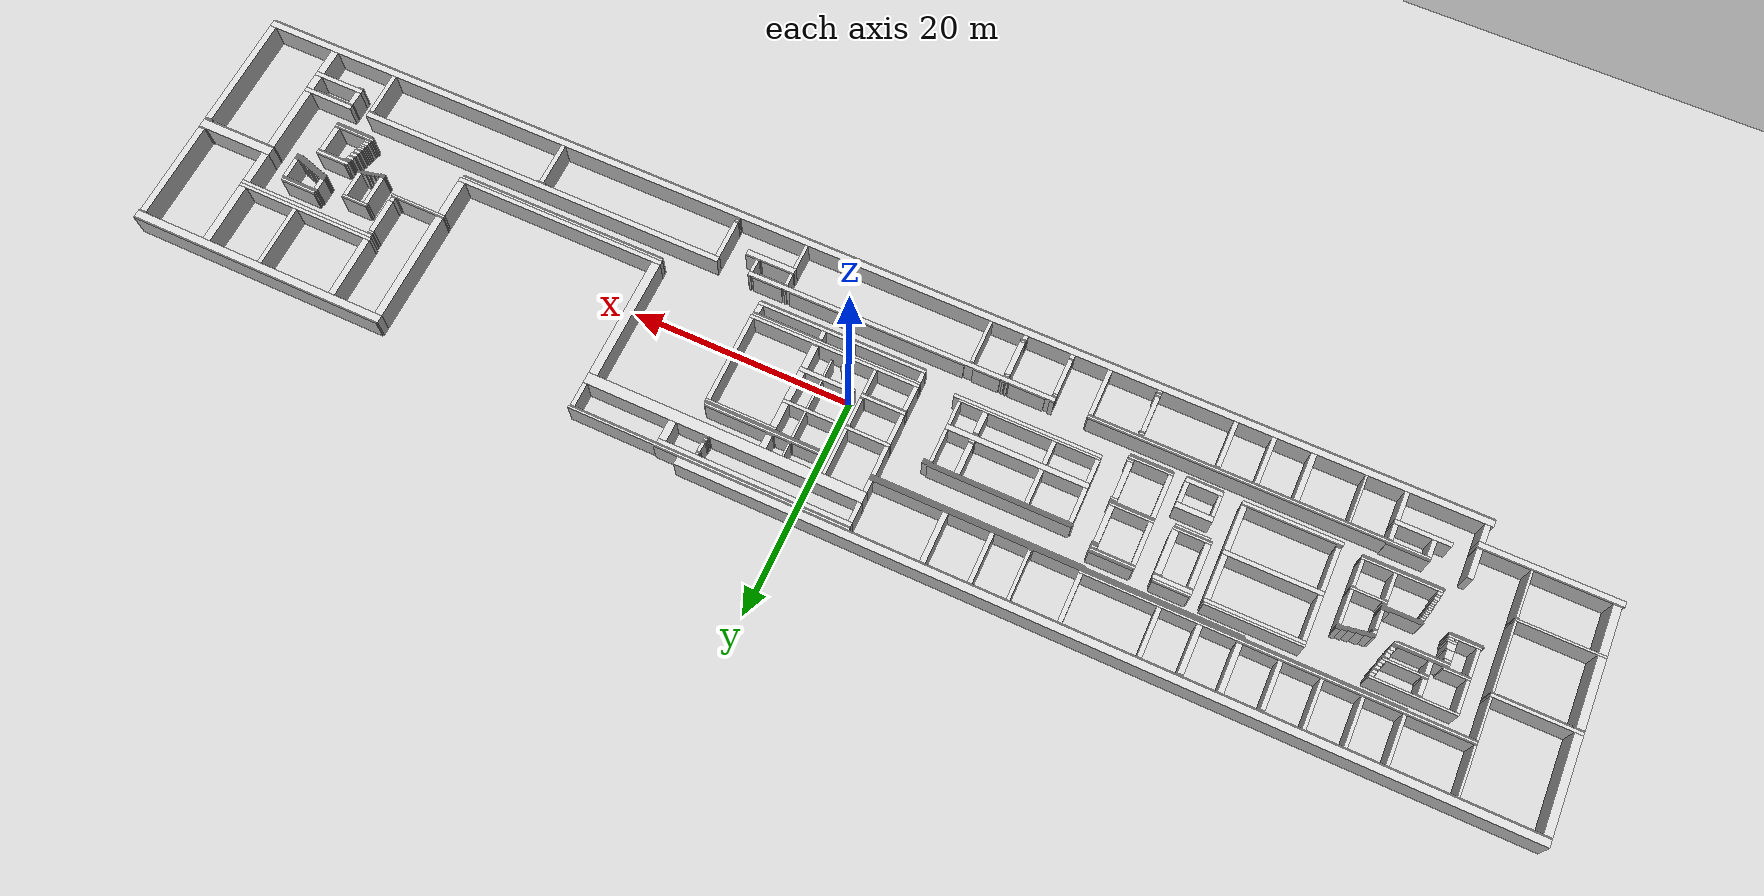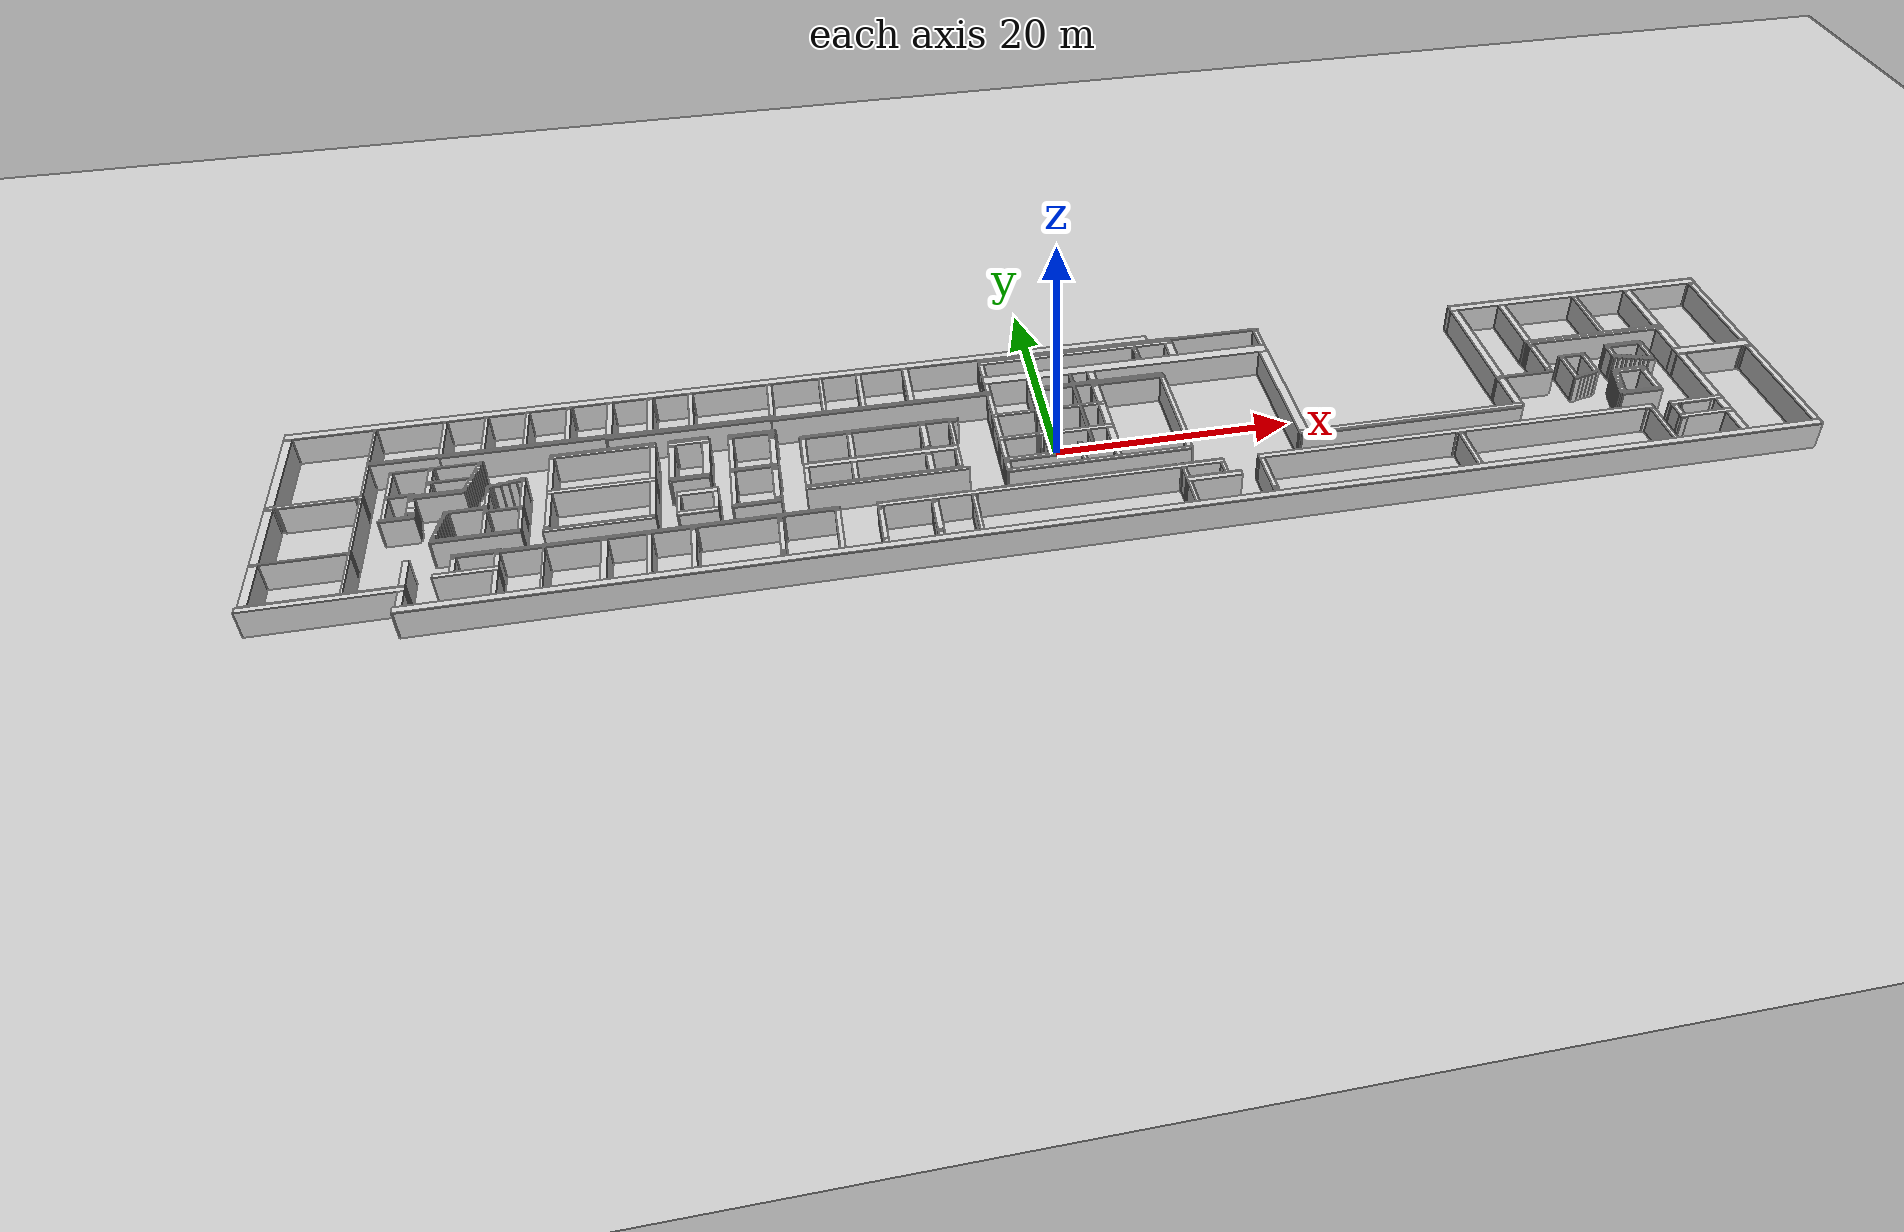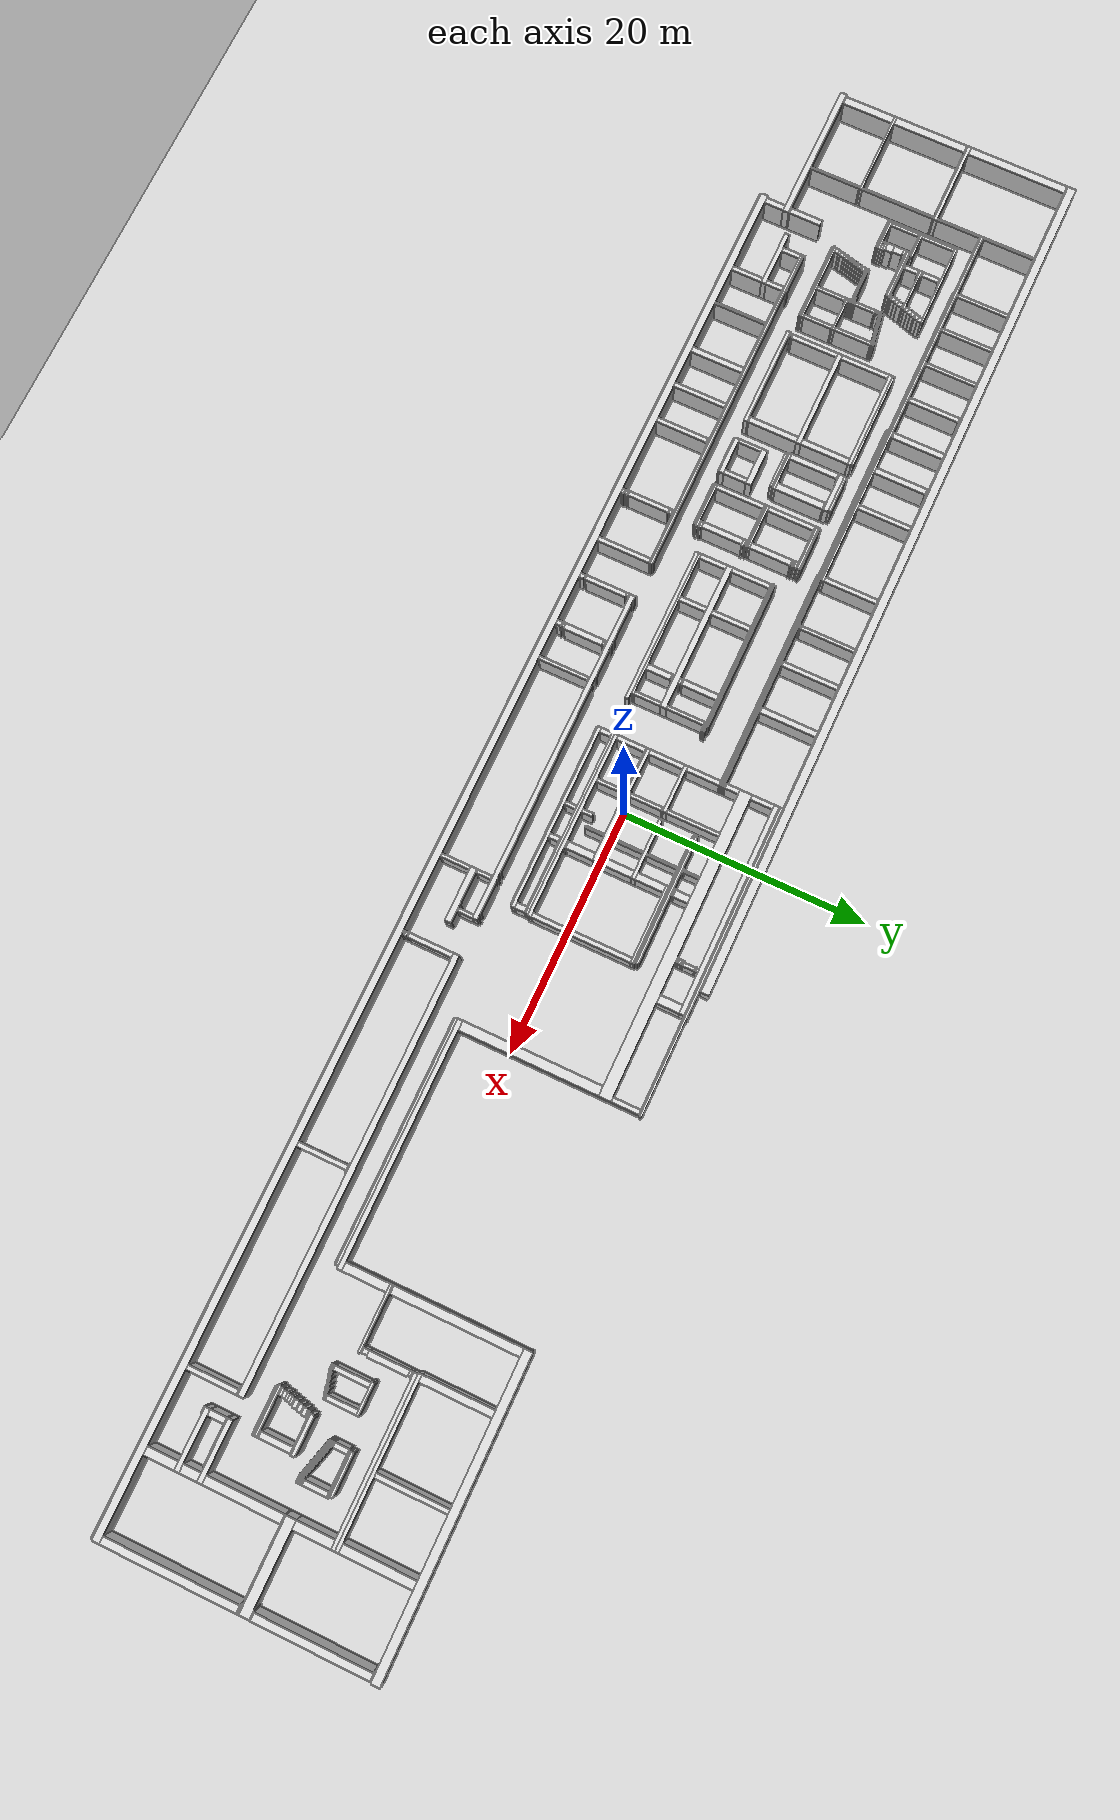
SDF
<?xml version="1.0"?>
<sdf version="1.8">
  <world name="default">
    <scene>
      <shadows>0</shadows>
    </scene>

    <gui fullscreen='0'>
      <camera name='user_camera'>
        <pose frame=''>0.319654 -0.235002 9.29441 0 1.5138 0.009599</pose>
        <view_controller>orbit</view_controller>
        <projection_type>perspective</projection_type>
      </camera>
    </gui>

    <physics type="ode">
      <real_time_update_rate>1000.0</real_time_update_rate>
      <max_step_size>0.001</max_step_size>
      <real_time_factor>1</real_time_factor>
      <ode>
        <solver>
          <type>quick</type>
          <iters>150</iters>
          <precon_iters>0</precon_iters>
          <sor>1.400000</sor>
          <use_dynamic_moi_rescaling>1</use_dynamic_moi_rescaling>
        </solver>
        <constraints>
          <cfm>0.00001</cfm>
          <erp>0.2</erp>
          <contact_max_correcting_vel>2000.000000</contact_max_correcting_vel>
          <contact_surface_layer>0.01000</contact_surface_layer>
        </constraints>
      </ode>
    </physics>
    <plugin
      filename="gz-sim-physics-system"
      name="gz::sim::systems::Physics">
    </plugin>
    <plugin
      filename="gz-sim-user-commands-system"
      name="gz::sim::systems::UserCommands">
    </plugin>
    <plugin
      filename="gz-sim-scene-broadcaster-system"
      name="gz::sim::systems::SceneBroadcaster">
    </plugin>
    <plugin
      filename="gz-sim-sensors-system"
      name="gz::sim::systems::Sensors">
      <render_engine>ogre2</render_engine>
    </plugin>
    <plugin
      filename="gz-sim-imu-system"
      name="gz::sim::systems::Imu">
    </plugin>

    <include>
      <uri>https://fuel.gazebosim.org/1.0/OpenRobotics/models/Ground Plane</uri>
    </include>

    <include>
      <uri>https://fuel.gazebosim.org/1.0/OpenRobotics/models/Sun</uri>
    </include>

    <model name="turtlebot3_house">
      <static>1</static>
      <include>
        <uri>model://campus_first_floor</uri>
      </include>
    </model>

  </world>
</sdf>

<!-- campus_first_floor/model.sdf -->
<sdf version="1.8">
  <model name="campus_first_floor">
    <static>true</static>
    <link name="wall_0">
      <pose>-26.00000 11.25000 1.25000 0 0 0</pose>
      <collision name="collision">
        <geometry><box><size>72.50000 0.70000 2.50000</size></box></geometry>
      </collision>
      <visual name="visual">
        <geometry><box><size>72.50000 0.70000 2.50000</size></box></geometry>
        <material>
          <ambient>0.72 0.72 0.72 1</ambient>
          <diffuse>0.82 0.82 0.82 1</diffuse>
          <specular>0.05 0.05 0.05 1</specular>
        </material>
      </visual>
    </link>
    <link name="wall_1">
      <pose>-24.90000 10.85000 1.25000 0 0 0</pose>
      <collision name="collision">
        <geometry><box><size>74.70000 0.10000 2.50000</size></box></geometry>
      </collision>
      <visual name="visual">
        <geometry><box><size>74.70000 0.10000 2.50000</size></box></geometry>
        <material>
          <ambient>0.72 0.72 0.72 1</ambient>
          <diffuse>0.82 0.82 0.82 1</diffuse>
          <specular>0.05 0.05 0.05 1</specular>
        </material>
      </visual>
    </link>
    <link name="wall_2">
      <pose>-32.85000 10.75000 1.25000 0 0 0</pose>
      <collision name="collision">
        <geometry><box><size>0.60000 0.10000 2.50000</size></box></geometry>
      </collision>
      <visual name="visual">
        <geometry><box><size>0.60000 0.10000 2.50000</size></box></geometry>
        <material>
          <ambient>0.72 0.72 0.72 1</ambient>
          <diffuse>0.82 0.82 0.82 1</diffuse>
          <specular>0.05 0.05 0.05 1</specular>
        </material>
      </visual>
    </link>
    <link name="wall_3">
      <pose>50.45000 10.75000 1.25000 0 0 0</pose>
      <collision name="collision">
        <geometry><box><size>24.00000 0.10000 2.50000</size></box></geometry>
      </collision>
      <visual name="visual">
        <geometry><box><size>24.00000 0.10000 2.50000</size></box></geometry>
        <material>
          <ambient>0.72 0.72 0.72 1</ambient>
          <diffuse>0.82 0.82 0.82 1</diffuse>
          <specular>0.05 0.05 0.05 1</specular>
        </material>
      </visual>
    </link>
    <link name="wall_4">
      <pose>-39.50000 10.75000 1.25000 0 0 0</pose>
      <collision name="collision">
        <geometry><box><size>0.50000 0.10000 2.50000</size></box></geometry>
      </collision>
      <visual name="visual">
        <geometry><box><size>0.50000 0.10000 2.50000</size></box></geometry>
        <material>
          <ambient>0.72 0.72 0.72 1</ambient>
          <diffuse>0.82 0.82 0.82 1</diffuse>
          <specular>0.05 0.05 0.05 1</specular>
        </material>
      </visual>
    </link>
    <link name="wall_5">
      <pose>7.70000 10.70000 1.25000 0 0 0</pose>
      <collision name="collision">
        <geometry><box><size>25.30000 0.20000 2.50000</size></box></geometry>
      </collision>
      <visual name="visual">
        <geometry><box><size>25.30000 0.20000 2.50000</size></box></geometry>
        <material>
          <ambient>0.72 0.72 0.72 1</ambient>
          <diffuse>0.82 0.82 0.82 1</diffuse>
          <specular>0.05 0.05 0.05 1</specular>
        </material>
      </visual>
    </link>
    <link name="wall_6">
      <pose>7.65000 10.55000 1.25000 0 0 0</pose>
      <collision name="collision">
        <geometry><box><size>25.20000 0.10000 2.50000</size></box></geometry>
      </collision>
      <visual name="visual">
        <geometry><box><size>25.20000 0.10000 2.50000</size></box></geometry>
        <material>
          <ambient>0.72 0.72 0.72 1</ambient>
          <diffuse>0.82 0.82 0.82 1</diffuse>
          <specular>0.05 0.05 0.05 1</specular>
        </material>
      </visual>
    </link>
    <link name="wall_7">
      <pose>3.70000 10.30000 1.25000 0 0 0</pose>
      <collision name="collision">
        <geometry><box><size>17.30000 0.40000 2.50000</size></box></geometry>
      </collision>
      <visual name="visual">
        <geometry><box><size>17.30000 0.40000 2.50000</size></box></geometry>
        <material>
          <ambient>0.72 0.72 0.72 1</ambient>
          <diffuse>0.82 0.82 0.82 1</diffuse>
          <specular>0.05 0.05 0.05 1</specular>
        </material>
      </visual>
    </link>
    <link name="wall_8">
      <pose>50.40000 10.35000 1.25000 0 0 0</pose>
      <collision name="collision">
        <geometry><box><size>24.10000 0.70000 2.50000</size></box></geometry>
      </collision>
      <visual name="visual">
        <geometry><box><size>24.10000 0.70000 2.50000</size></box></geometry>
        <material>
          <ambient>0.72 0.72 0.72 1</ambient>
          <diffuse>0.82 0.82 0.82 1</diffuse>
          <specular>0.05 0.05 0.05 1</specular>
        </material>
      </visual>
    </link>
    <link name="wall_9">
      <pose>62.00000 9.95000 1.25000 0 0 0</pose>
      <collision name="collision">
        <geometry><box><size>0.70000 0.10000 2.50000</size></box></geometry>
      </collision>
      <visual name="visual">
        <geometry><box><size>0.70000 0.10000 2.50000</size></box></geometry>
        <material>
          <ambient>0.72 0.72 0.72 1</ambient>
          <diffuse>0.82 0.82 0.82 1</diffuse>
          <specular>0.05 0.05 0.05 1</specular>
        </material>
      </visual>
    </link>
    <link name="wall_10">
      <pose>8.90000 10.00000 1.25000 0 0 0</pose>
      <collision name="collision">
        <geometry><box><size>0.30000 0.20000 2.50000</size></box></geometry>
      </collision>
      <visual name="visual">
        <geometry><box><size>0.30000 0.20000 2.50000</size></box></geometry>
        <material>
          <ambient>0.72 0.72 0.72 1</ambient>
          <diffuse>0.82 0.82 0.82 1</diffuse>
          <specular>0.05 0.05 0.05 1</specular>
        </material>
      </visual>
    </link>
    <link name="wall_11">
      <pose>8.85000 9.85000 1.25000 0 0 0</pose>
      <collision name="collision">
        <geometry><box><size>0.40000 0.10000 2.50000</size></box></geometry>
      </collision>
      <visual name="visual">
        <geometry><box><size>0.40000 0.10000 2.50000</size></box></geometry>
        <material>
          <ambient>0.72 0.72 0.72 1</ambient>
          <diffuse>0.82 0.82 0.82 1</diffuse>
          <specular>0.05 0.05 0.05 1</specular>
        </material>
      </visual>
    </link>
    <link name="wall_12">
      <pose>8.90000 9.35000 1.25000 0 0 0</pose>
      <collision name="collision">
        <geometry><box><size>0.30000 0.90000 2.50000</size></box></geometry>
      </collision>
      <visual name="visual">
        <geometry><box><size>0.30000 0.90000 2.50000</size></box></geometry>
        <material>
          <ambient>0.72 0.72 0.72 1</ambient>
          <diffuse>0.82 0.82 0.82 1</diffuse>
          <specular>0.05 0.05 0.05 1</specular>
        </material>
      </visual>
    </link>
    <link name="wall_13">
      <pose>8.85000 8.85000 1.25000 0 0 0</pose>
      <collision name="collision">
        <geometry><box><size>0.40000 0.10000 2.50000</size></box></geometry>
      </collision>
      <visual name="visual">
        <geometry><box><size>0.40000 0.10000 2.50000</size></box></geometry>
        <material>
          <ambient>0.72 0.72 0.72 1</ambient>
          <diffuse>0.82 0.82 0.82 1</diffuse>
          <specular>0.05 0.05 0.05 1</specular>
        </material>
      </visual>
    </link>
    <link name="wall_14">
      <pose>8.90000 8.75000 1.25000 0 0 0</pose>
      <collision name="collision">
        <geometry><box><size>0.30000 0.10000 2.50000</size></box></geometry>
      </collision>
      <visual name="visual">
        <geometry><box><size>0.30000 0.10000 2.50000</size></box></geometry>
        <material>
          <ambient>0.72 0.72 0.72 1</ambient>
          <diffuse>0.82 0.82 0.82 1</diffuse>
          <specular>0.05 0.05 0.05 1</specular>
        </material>
      </visual>
    </link>
    <link name="wall_15">
      <pose>8.85000 8.60000 1.25000 0 0 0</pose>
      <collision name="collision">
        <geometry><box><size>0.40000 0.20000 2.50000</size></box></geometry>
      </collision>
      <visual name="visual">
        <geometry><box><size>0.40000 0.20000 2.50000</size></box></geometry>
        <material>
          <ambient>0.72 0.72 0.72 1</ambient>
          <diffuse>0.82 0.82 0.82 1</diffuse>
          <specular>0.05 0.05 0.05 1</specular>
        </material>
      </visual>
    </link>
    <link name="wall_16">
      <pose>8.90000 8.45000 1.25000 0 0 0</pose>
      <collision name="collision">
        <geometry><box><size>0.30000 0.10000 2.50000</size></box></geometry>
      </collision>
      <visual name="visual">
        <geometry><box><size>0.30000 0.10000 2.50000</size></box></geometry>
        <material>
          <ambient>0.72 0.72 0.72 1</ambient>
          <diffuse>0.82 0.82 0.82 1</diffuse>
          <specular>0.05 0.05 0.05 1</specular>
        </material>
      </visual>
    </link>
    <link name="wall_17">
      <pose>12.00000 9.20000 1.25000 0 0 0</pose>
      <collision name="collision">
        <geometry><box><size>0.70000 1.80000 2.50000</size></box></geometry>
      </collision>
      <visual name="visual">
        <geometry><box><size>0.70000 1.80000 2.50000</size></box></geometry>
        <material>
          <ambient>0.72 0.72 0.72 1</ambient>
          <diffuse>0.82 0.82 0.82 1</diffuse>
          <specular>0.05 0.05 0.05 1</specular>
        </material>
      </visual>
    </link>
    <link name="wall_18">
      <pose>8.85000 8.35000 1.25000 0 0 0</pose>
      <collision name="collision">
        <geometry><box><size>0.40000 0.10000 2.50000</size></box></geometry>
      </collision>
      <visual name="visual">
        <geometry><box><size>0.40000 0.10000 2.50000</size></box></geometry>
        <material>
          <ambient>0.72 0.72 0.72 1</ambient>
          <diffuse>0.82 0.82 0.82 1</diffuse>
          <specular>0.05 0.05 0.05 1</specular>
        </material>
      </visual>
    </link>
    <link name="wall_19">
      <pose>20.05000 9.40000 1.25000 0 0 0</pose>
      <collision name="collision">
        <geometry><box><size>0.40000 2.20000 2.50000</size></box></geometry>
      </collision>
      <visual name="visual">
        <geometry><box><size>0.40000 2.20000 2.50000</size></box></geometry>
        <material>
          <ambient>0.72 0.72 0.72 1</ambient>
          <diffuse>0.82 0.82 0.82 1</diffuse>
          <specular>0.05 0.05 0.05 1</specular>
        </material>
      </visual>
    </link>
    <link name="wall_20">
      <pose>-4.75000 9.20000 1.25000 0 0 0</pose>
      <collision name="collision">
        <geometry><box><size>0.40000 1.80000 2.50000</size></box></geometry>
      </collision>
      <visual name="visual">
        <geometry><box><size>0.40000 1.80000 2.50000</size></box></geometry>
        <material>
          <ambient>0.72 0.72 0.72 1</ambient>
          <diffuse>0.82 0.82 0.82 1</diffuse>
          <specular>0.05 0.05 0.05 1</specular>
        </material>
      </visual>
    </link>
    <link name="wall_21">
      <pose>7.65000 7.80000 1.25000 0 0 0</pose>
      <collision name="collision">
        <geometry><box><size>25.20000 1.00000 2.50000</size></box></geometry>
      </collision>
      <visual name="visual">
        <geometry><box><size>25.20000 1.00000 2.50000</size></box></geometry>
        <material>
          <ambient>0.72 0.72 0.72 1</ambient>
          <diffuse>0.82 0.82 0.82 1</diffuse>
          <specular>0.05 0.05 0.05 1</specular>
        </material>
      </visual>
    </link>
    <link name="wall_22">
      <pose>-46.20000 8.65000 1.25000 0 0 0</pose>
      <collision name="collision">
        <geometry><box><size>0.30000 4.30000 2.50000</size></box></geometry>
      </collision>
      <visual name="visual">
        <geometry><box><size>0.30000 4.30000 2.50000</size></box></geometry>
        <material>
          <ambient>0.72 0.72 0.72 1</ambient>
          <diffuse>0.82 0.82 0.82 1</diffuse>
          <specular>0.05 0.05 0.05 1</specular>
        </material>
      </visual>
    </link>
    <link name="wall_23">
      <pose>-39.55000 8.60000 1.25000 0 0 0</pose>
      <collision name="collision">
        <geometry><box><size>0.40000 4.20000 2.50000</size></box></geometry>
      </collision>
      <visual name="visual">
        <geometry><box><size>0.40000 4.20000 2.50000</size></box></geometry>
        <material>
          <ambient>0.72 0.72 0.72 1</ambient>
          <diffuse>0.82 0.82 0.82 1</diffuse>
          <specular>0.05 0.05 0.05 1</specular>
        </material>
      </visual>
    </link>
    <link name="wall_24">
      <pose>-49.50000 8.65000 1.25000 0 0 0</pose>
      <collision name="collision">
        <geometry><box><size>0.30000 4.30000 2.50000</size></box></geometry>
      </collision>
      <visual name="visual">
        <geometry><box><size>0.30000 4.30000 2.50000</size></box></geometry>
        <material>
          <ambient>0.72 0.72 0.72 1</ambient>
          <diffuse>0.82 0.82 0.82 1</diffuse>
          <specular>0.05 0.05 0.05 1</specular>
        </material>
      </visual>
    </link>
    <link name="wall_25">
      <pose>-36.20000 8.65000 1.25000 0 0 0</pose>
      <collision name="collision">
        <geometry><box><size>0.50000 4.30000 2.50000</size></box></geometry>
      </collision>
      <visual name="visual">
        <geometry><box><size>0.50000 4.30000 2.50000</size></box></geometry>
        <material>
          <ambient>0.72 0.72 0.72 1</ambient>
          <diffuse>0.82 0.82 0.82 1</diffuse>
          <specular>0.05 0.05 0.05 1</specular>
        </material>
      </visual>
    </link>
    <link name="wall_26">
      <pose>-55.05000 8.65000 1.25000 0 0 0</pose>
      <collision name="collision">
        <geometry><box><size>0.20000 4.30000 2.50000</size></box></geometry>
      </collision>
      <visual name="visual">
        <geometry><box><size>0.20000 4.30000 2.50000</size></box></geometry>
        <material>
          <ambient>0.72 0.72 0.72 1</ambient>
          <diffuse>0.82 0.82 0.82 1</diffuse>
          <specular>0.05 0.05 0.05 1</specular>
        </material>
      </visual>
    </link>
    <link name="wall_27">
      <pose>-42.90000 8.65000 1.25000 0 0 0</pose>
      <collision name="collision">
        <geometry><box><size>0.30000 4.30000 2.50000</size></box></geometry>
      </collision>
      <visual name="visual">
        <geometry><box><size>0.30000 4.30000 2.50000</size></box></geometry>
        <material>
          <ambient>0.72 0.72 0.72 1</ambient>
          <diffuse>0.82 0.82 0.82 1</diffuse>
          <specular>0.05 0.05 0.05 1</specular>
        </material>
      </visual>
    </link>
    <link name="wall_28">
      <pose>-32.90000 8.55000 1.25000 0 0 0</pose>
      <collision name="collision">
        <geometry><box><size>0.50000 4.30000 2.50000</size></box></geometry>
      </collision>
      <visual name="visual">
        <geometry><box><size>0.50000 4.30000 2.50000</size></box></geometry>
        <material>
          <ambient>0.72 0.72 0.72 1</ambient>
          <diffuse>0.82 0.82 0.82 1</diffuse>
          <specular>0.05 0.05 0.05 1</specular>
        </material>
      </visual>
    </link>
    <link name="wall_29">
      <pose>-29.55000 8.60000 1.25000 0 0 0</pose>
      <collision name="collision">
        <geometry><box><size>0.40000 4.40000 2.50000</size></box></geometry>
      </collision>
      <visual name="visual">
        <geometry><box><size>0.40000 4.40000 2.50000</size></box></geometry>
        <material>
          <ambient>0.72 0.72 0.72 1</ambient>
          <diffuse>0.82 0.82 0.82 1</diffuse>
          <specular>0.05 0.05 0.05 1</specular>
        </material>
      </visual>
    </link>
    <link name="wall_30">
      <pose>-22.95000 8.60000 1.25000 0 0 0</pose>
      <collision name="collision">
        <geometry><box><size>0.40000 4.40000 2.50000</size></box></geometry>
      </collision>
      <visual name="visual">
        <geometry><box><size>0.40000 4.40000 2.50000</size></box></geometry>
        <material>
          <ambient>0.72 0.72 0.72 1</ambient>
          <diffuse>0.82 0.82 0.82 1</diffuse>
          <specular>0.05 0.05 0.05 1</specular>
        </material>
      </visual>
    </link>
    <link name="wall_31">
      <pose>-45.55000 6.45000 1.25000 0 0 0</pose>
      <collision name="collision">
        <geometry><box><size>19.20000 0.10000 2.50000</size></box></geometry>
      </collision>
      <visual name="visual">
        <geometry><box><size>19.20000 0.10000 2.50000</size></box></geometry>
        <material>
          <ambient>0.72 0.72 0.72 1</ambient>
          <diffuse>0.82 0.82 0.82 1</diffuse>
          <specular>0.05 0.05 0.05 1</specular>
        </material>
      </visual>
    </link>
    <link name="wall_32">
      <pose>-18.60000 8.55000 1.25000 0 0 0</pose>
      <collision name="collision">
        <geometry><box><size>0.30000 4.50000 2.50000</size></box></geometry>
      </collision>
      <visual name="visual">
        <geometry><box><size>0.30000 4.50000 2.50000</size></box></geometry>
        <material>
          <ambient>0.72 0.72 0.72 1</ambient>
          <diffuse>0.82 0.82 0.82 1</diffuse>
          <specular>0.05 0.05 0.05 1</specular>
        </material>
      </visual>
    </link>
    <link name="wall_33">
      <pose>-11.30000 8.50000 1.25000 0 0 0</pose>
      <collision name="collision">
        <geometry><box><size>0.50000 4.60000 2.50000</size></box></geometry>
      </collision>
      <visual name="visual">
        <geometry><box><size>0.50000 4.60000 2.50000</size></box></geometry>
        <material>
          <ambient>0.72 0.72 0.72 1</ambient>
          <diffuse>0.82 0.82 0.82 1</diffuse>
          <specular>0.05 0.05 0.05 1</specular>
        </material>
      </visual>
    </link>
    <link name="wall_34">
      <pose>-18.65000 6.25000 1.25000 0 0 0</pose>
      <collision name="collision">
        <geometry><box><size>0.40000 0.10000 2.50000</size></box></geometry>
      </collision>
      <visual name="visual">
        <geometry><box><size>0.40000 0.10000 2.50000</size></box></geometry>
        <material>
          <ambient>0.72 0.72 0.72 1</ambient>
          <diffuse>0.82 0.82 0.82 1</diffuse>
          <specular>0.05 0.05 0.05 1</specular>
        </material>
      </visual>
    </link>
    <link name="wall_35">
      <pose>-38.95000 6.30000 1.25000 0 0 0</pose>
      <collision name="collision">
        <geometry><box><size>32.40000 0.20000 2.50000</size></box></geometry>
      </collision>
      <visual name="visual">
        <geometry><box><size>32.40000 0.20000 2.50000</size></box></geometry>
        <material>
          <ambient>0.72 0.72 0.72 1</ambient>
          <diffuse>0.82 0.82 0.82 1</diffuse>
          <specular>0.05 0.05 0.05 1</specular>
        </material>
      </visual>
    </link>
    <link name="wall_36">
      <pose>-4.75000 6.75000 1.25000 0 0 0</pose>
      <collision name="collision">
        <geometry><box><size>0.40000 1.10000 2.50000</size></box></geometry>
      </collision>
      <visual name="visual">
        <geometry><box><size>0.40000 1.10000 2.50000</size></box></geometry>
        <material>
          <ambient>0.72 0.72 0.72 1</ambient>
          <diffuse>0.82 0.82 0.82 1</diffuse>
          <specular>0.05 0.05 0.05 1</specular>
        </material>
      </visual>
    </link>
    <link name="wall_37">
      <pose>-15.35000 8.50000 1.25000 0 0 0</pose>
      <collision name="collision">
        <geometry><box><size>0.40000 4.60000 2.50000</size></box></geometry>
      </collision>
      <visual name="visual">
        <geometry><box><size>0.40000 4.60000 2.50000</size></box></geometry>
        <material>
          <ambient>0.72 0.72 0.72 1</ambient>
          <diffuse>0.82 0.82 0.82 1</diffuse>
          <specular>0.05 0.05 0.05 1</specular>
        </material>
      </visual>
    </link>
    <link name="wall_38">
      <pose>-29.85000 6.15000 1.25000 0 0 0</pose>
      <collision name="collision">
        <geometry><box><size>50.60000 0.10000 2.50000</size></box></geometry>
      </collision>
      <visual name="visual">
        <geometry><box><size>50.60000 0.10000 2.50000</size></box></geometry>
        <material>
          <ambient>0.72 0.72 0.72 1</ambient>
          <diffuse>0.82 0.82 0.82 1</diffuse>
          <specular>0.05 0.05 0.05 1</specular>
        </material>
      </visual>
    </link>
    <link name="wall_39">
      <pose>4.35000 6.70000 1.25000 0 0 0</pose>
      <collision name="collision">
        <geometry><box><size>0.60000 1.20000 2.50000</size></box></geometry>
      </collision>
      <visual name="visual">
        <geometry><box><size>0.60000 1.20000 2.50000</size></box></geometry>
        <material>
          <ambient>0.72 0.72 0.72 1</ambient>
          <diffuse>0.82 0.82 0.82 1</diffuse>
          <specular>0.05 0.05 0.05 1</specular>
        </material>
      </visual>
    </link>
    <link name="wall_40">
      <pose>2.55000 6.70000 1.25000 0 0 0</pose>
      <collision name="collision">
        <geometry><box><size>0.20000 1.20000 2.50000</size></box></geometry>
      </collision>
      <visual name="visual">
        <geometry><box><size>0.20000 1.20000 2.50000</size></box></geometry>
        <material>
          <ambient>0.72 0.72 0.72 1</ambient>
          <diffuse>0.82 0.82 0.82 1</diffuse>
          <specular>0.05 0.05 0.05 1</specular>
        </material>
      </visual>
    </link>
    <link name="wall_41">
      <pose>4.30000 6.05000 1.25000 0 0 0</pose>
      <collision name="collision">
        <geometry><box><size>0.70000 0.10000 2.50000</size></box></geometry>
      </collision>
      <visual name="visual">
        <geometry><box><size>0.70000 0.10000 2.50000</size></box></geometry>
        <material>
          <ambient>0.72 0.72 0.72 1</ambient>
          <diffuse>0.82 0.82 0.82 1</diffuse>
          <specular>0.05 0.05 0.05 1</specular>
        </material>
      </visual>
    </link>
    <link name="wall_42">
      <pose>-27.05000 6.05000 1.25000 0 0 0</pose>
      <collision name="collision">
        <geometry><box><size>45.00000 0.10000 2.50000</size></box></geometry>
      </collision>
      <visual name="visual">
        <geometry><box><size>45.00000 0.10000 2.50000</size></box></geometry>
        <material>
          <ambient>0.72 0.72 0.72 1</ambient>
          <diffuse>0.82 0.82 0.82 1</diffuse>
          <specular>0.05 0.05 0.05 1</specular>
        </material>
      </visual>
    </link>
    <link name="wall_43">
      <pose>2.55000 6.05000 1.25000 0 0 0</pose>
      <collision name="collision">
        <geometry><box><size>0.40000 0.10000 2.50000</size></box></geometry>
      </collision>
      <visual name="visual">
        <geometry><box><size>0.40000 0.10000 2.50000</size></box></geometry>
        <material>
          <ambient>0.72 0.72 0.72 1</ambient>
          <diffuse>0.82 0.82 0.82 1</diffuse>
          <specular>0.05 0.05 0.05 1</specular>
        </material>
      </visual>
    </link>
    <link name="wall_44">
      <pose>4.95000 5.95000 1.25000 0 0 0</pose>
      <collision name="collision">
        <geometry><box><size>10.60000 0.10000 2.50000</size></box></geometry>
      </collision>
      <visual name="visual">
        <geometry><box><size>10.60000 0.10000 2.50000</size></box></geometry>
        <material>
          <ambient>0.72 0.72 0.72 1</ambient>
          <diffuse>0.82 0.82 0.82 1</diffuse>
          <specular>0.05 0.05 0.05 1</specular>
        </material>
      </visual>
    </link>
    <link name="wall_45">
      <pose>-20.50000 5.95000 1.25000 0 0 0</pose>
      <collision name="collision">
        <geometry><box><size>31.90000 0.10000 2.50000</size></box></geometry>
      </collision>
      <visual name="visual">
        <geometry><box><size>31.90000 0.10000 2.50000</size></box></geometry>
        <material>
          <ambient>0.72 0.72 0.72 1</ambient>
          <diffuse>0.82 0.82 0.82 1</diffuse>
          <specular>0.05 0.05 0.05 1</specular>
        </material>
      </visual>
    </link>
    <link name="wall_46">
      <pose>-20.45000 5.85000 1.25000 0 0 0</pose>
      <collision name="collision">
        <geometry><box><size>31.80000 0.10000 2.50000</size></box></geometry>
      </collision>
      <visual name="visual">
        <geometry><box><size>31.80000 0.10000 2.50000</size></box></geometry>
        <material>
          <ambient>0.72 0.72 0.72 1</ambient>
          <diffuse>0.82 0.82 0.82 1</diffuse>
          <specular>0.05 0.05 0.05 1</specular>
        </material>
      </visual>
    </link>
    <link name="wall_47">
      <pose>-13.80000 5.75000 1.25000 0 0 0</pose>
      <collision name="collision">
        <geometry><box><size>18.50000 0.10000 2.50000</size></box></geometry>
      </collision>
      <visual name="visual">
        <geometry><box><size>18.50000 0.10000 2.50000</size></box></geometry>
        <material>
          <ambient>0.72 0.72 0.72 1</ambient>
          <diffuse>0.82 0.82 0.82 1</diffuse>
          <specular>0.05 0.05 0.05 1</specular>
        </material>
      </visual>
    </link>
    <link name="wall_48">
      <pose>5.00000 5.80000 1.25000 0 0 0</pose>
      <collision name="collision">
        <geometry><box><size>10.70000 0.20000 2.50000</size></box></geometry>
      </collision>
      <visual name="visual">
        <geometry><box><size>10.70000 0.20000 2.50000</size></box></geometry>
        <material>
          <ambient>0.72 0.72 0.72 1</ambient>
          <diffuse>0.82 0.82 0.82 1</diffuse>
          <specular>0.05 0.05 0.05 1</specular>
        </material>
      </visual>
    </link>
    <link name="wall_49">
      <pose>5.05000 5.65000 1.25000 0 0 0</pose>
      <collision name="collision">
        <geometry><box><size>10.80000 0.10000 2.50000</size></box></geometry>
      </collision>
      <visual name="visual">
        <geometry><box><size>10.80000 0.10000 2.50000</size></box></geometry>
        <material>
          <ambient>0.72 0.72 0.72 1</ambient>
          <diffuse>0.82 0.82 0.82 1</diffuse>
          <specular>0.05 0.05 0.05 1</specular>
        </material>
      </visual>
    </link>
    <link name="wall_50">
      <pose>5.10000 5.55000 1.25000 0 0 0</pose>
      <collision name="collision">
        <geometry><box><size>10.70000 0.10000 2.50000</size></box></geometry>
      </collision>
      <visual name="visual">
        <geometry><box><size>10.70000 0.10000 2.50000</size></box></geometry>
        <material>
          <ambient>0.72 0.72 0.72 1</ambient>
          <diffuse>0.82 0.82 0.82 1</diffuse>
          <specular>0.05 0.05 0.05 1</specular>
        </material>
      </visual>
    </link>
    <link name="wall_51">
      <pose>7.25000 5.40000 1.25000 0 0 0</pose>
      <collision name="collision">
        <geometry><box><size>6.40000 0.20000 2.50000</size></box></geometry>
      </collision>
      <visual name="visual">
        <geometry><box><size>6.40000 0.20000 2.50000</size></box></geometry>
        <material>
          <ambient>0.72 0.72 0.72 1</ambient>
          <diffuse>0.82 0.82 0.82 1</diffuse>
          <specular>0.05 0.05 0.05 1</specular>
        </material>
      </visual>
    </link>
    <link name="wall_52">
      <pose>-49.65000 4.80000 1.25000 0 0 0</pose>
      <collision name="collision">
        <geometry><box><size>7.20000 0.20000 2.50000</size></box></geometry>
      </collision>
      <visual name="visual">
        <geometry><box><size>7.20000 0.20000 2.50000</size></box></geometry>
        <material>
          <ambient>0.72 0.72 0.72 1</ambient>
          <diffuse>0.82 0.82 0.82 1</diffuse>
          <specular>0.05 0.05 0.05 1</specular>
        </material>
      </visual>
    </link>
    <link name="wall_53">
      <pose>-29.80000 4.65000 1.25000 0 0 0</pose>
      <collision name="collision">
        <geometry><box><size>3.10000 0.10000 2.50000</size></box></geometry>
      </collision>
      <visual name="visual">
        <geometry><box><size>3.10000 0.10000 2.50000</size></box></geometry>
        <material>
          <ambient>0.72 0.72 0.72 1</ambient>
          <diffuse>0.82 0.82 0.82 1</diffuse>
          <specular>0.05 0.05 0.05 1</specular>
        </material>
      </visual>
    </link>
    <link name="wall_54">
      <pose>-50.00000 4.65000 1.25000 0 0 0</pose>
      <collision name="collision">
        <geometry><box><size>0.50000 0.10000 2.50000</size></box></geometry>
      </collision>
      <visual name="visual">
        <geometry><box><size>0.50000 0.10000 2.50000</size></box></geometry>
        <material>
          <ambient>0.72 0.72 0.72 1</ambient>
          <diffuse>0.82 0.82 0.82 1</diffuse>
          <specular>0.05 0.05 0.05 1</specular>
        </material>
      </visual>
    </link>
    <link name="wall_55">
      <pose>-36.70000 4.60000 1.25000 0 0 0</pose>
      <collision name="collision">
        <geometry><box><size>8.30000 0.20000 2.50000</size></box></geometry>
      </collision>
      <visual name="visual">
        <geometry><box><size>8.30000 0.20000 2.50000</size></box></geometry>
        <material>
          <ambient>0.72 0.72 0.72 1</ambient>
          <diffuse>0.82 0.82 0.82 1</diffuse>
          <specular>0.05 0.05 0.05 1</specular>
        </material>
      </visual>
    </link>
    <link name="wall_56">
      <pose>-46.25000 4.55000 1.25000 0 0 0</pose>
      <collision name="collision">
        <geometry><box><size>0.40000 0.30000 2.50000</size></box></geometry>
      </collision>
      <visual name="visual">
        <geometry><box><size>0.40000 0.30000 2.50000</size></box></geometry>
        <material>
          <ambient>0.72 0.72 0.72 1</ambient>
          <diffuse>0.82 0.82 0.82 1</diffuse>
          <specular>0.05 0.05 0.05 1</specular>
        </material>
      </visual>
    </link>
    <link name="wall_57">
      <pose>-29.85000 4.50000 1.25000 0 0 0</pose>
      <collision name="collision">
        <geometry><box><size>3.20000 0.20000 2.50000</size></box></geometry>
      </collision>
      <visual name="visual">
        <geometry><box><size>3.20000 0.20000 2.50000</size></box></geometry>
        <material>
          <ambient>0.72 0.72 0.72 1</ambient>
          <diffuse>0.82 0.82 0.82 1</diffuse>
          <specular>0.05 0.05 0.05 1</specular>
        </material>
      </visual>
    </link>
    <link name="wall_58">
      <pose>-24.70000 4.45000 1.25000 0 0 0</pose>
      <collision name="collision">
        <geometry><box><size>3.70000 0.10000 2.50000</size></box></geometry>
      </collision>
      <visual name="visual">
        <geometry><box><size>3.70000 0.10000 2.50000</size></box></geometry>
        <material>
          <ambient>0.72 0.72 0.72 1</ambient>
          <diffuse>0.82 0.82 0.82 1</diffuse>
          <specular>0.05 0.05 0.05 1</specular>
        </material>
      </visual>
    </link>
    <link name="wall_59">
      <pose>55.60000 7.15000 1.25000 0 0 0</pose>
      <collision name="collision">
        <geometry><box><size>0.70000 5.70000 2.50000</size></box></geometry>
      </collision>
      <visual name="visual">
        <geometry><box><size>0.70000 5.70000 2.50000</size></box></geometry>
        <material>
          <ambient>0.72 0.72 0.72 1</ambient>
          <diffuse>0.82 0.82 0.82 1</diffuse>
          <specular>0.05 0.05 0.05 1</specular>
        </material>
      </visual>
    </link>
    <link name="wall_60">
      <pose>-24.70000 4.35000 1.25000 0 0 0</pose>
      <collision name="collision">
        <geometry><box><size>3.90000 0.10000 2.50000</size></box></geometry>
      </collision>
      <visual name="visual">
        <geometry><box><size>3.90000 0.10000 2.50000</size></box></geometry>
        <material>
          <ambient>0.72 0.72 0.72 1</ambient>
          <diffuse>0.82 0.82 0.82 1</diffuse>
          <specular>0.05 0.05 0.05 1</specular>
        </material>
      </visual>
    </link>
    <link name="wall_61">
      <pose>50.35000 7.15000 1.25000 0 0 0</pose>
      <collision name="collision">
        <geometry><box><size>0.40000 5.70000 2.50000</size></box></geometry>
      </collision>
      <visual name="visual">
        <geometry><box><size>0.40000 5.70000 2.50000</size></box></geometry>
        <material>
          <ambient>0.72 0.72 0.72 1</ambient>
          <diffuse>0.82 0.82 0.82 1</diffuse>
          <specular>0.05 0.05 0.05 1</specular>
        </material>
      </visual>
    </link>
    <link name="wall_62">
      <pose>43.25000 7.15000 1.25000 0 0 0</pose>
      <collision name="collision">
        <geometry><box><size>0.60000 5.70000 2.50000</size></box></geometry>
      </collision>
      <visual name="visual">
        <geometry><box><size>0.60000 5.70000 2.50000</size></box></geometry>
        <material>
          <ambient>0.72 0.72 0.72 1</ambient>
          <diffuse>0.82 0.82 0.82 1</diffuse>
          <specular>0.05 0.05 0.05 1</specular>
        </material>
      </visual>
    </link>
    <link name="wall_63">
      <pose>-36.65000 4.35000 1.25000 0 0 0</pose>
      <collision name="collision">
        <geometry><box><size>8.40000 0.30000 2.50000</size></box></geometry>
      </collision>
      <visual name="visual">
        <geometry><box><size>8.40000 0.30000 2.50000</size></box></geometry>
        <material>
          <ambient>0.72 0.72 0.72 1</ambient>
          <diffuse>0.82 0.82 0.82 1</diffuse>
          <specular>0.05 0.05 0.05 1</specular>
        </material>
      </visual>
    </link>
    <link name="wall_64">
      <pose>-24.75000 4.20000 1.25000 0 0 0</pose>
      <collision name="collision">
        <geometry><box><size>3.80000 0.20000 2.50000</size></box></geometry>
      </collision>
      <visual name="visual">
        <geometry><box><size>3.80000 0.20000 2.50000</size></box></geometry>
        <material>
          <ambient>0.72 0.72 0.72 1</ambient>
          <diffuse>0.82 0.82 0.82 1</diffuse>
          <specular>0.05 0.05 0.05 1</specular>
        </material>
      </visual>
    </link>
    <link name="wall_65">
      <pose>-46.35000 4.25000 1.25000 0 0 0</pose>
      <collision name="collision">
        <geometry><box><size>0.40000 0.30000 2.50000</size></box></geometry>
      </collision>
      <visual name="visual">
        <geometry><box><size>0.40000 0.30000 2.50000</size></box></geometry>
        <material>
          <ambient>0.72 0.72 0.72 1</ambient>
          <diffuse>0.82 0.82 0.82 1</diffuse>
          <specular>0.05 0.05 0.05 1</specular>
        </material>
      </visual>
    </link>
    <link name="wall_66">
      <pose>-29.80000 4.20000 1.25000 0 0 0</pose>
      <collision name="collision">
        <geometry><box><size>3.30000 0.40000 2.50000</size></box></geometry>
      </collision>
      <visual name="visual">
        <geometry><box><size>3.30000 0.40000 2.50000</size></box></geometry>
        <material>
          <ambient>0.72 0.72 0.72 1</ambient>
          <diffuse>0.82 0.82 0.82 1</diffuse>
          <specular>0.05 0.05 0.05 1</specular>
        </material>
      </visual>
    </link>
    <link name="wall_67">
      <pose>-24.70000 4.05000 1.25000 0 0 0</pose>
      <collision name="collision">
        <geometry><box><size>3.90000 0.10000 2.50000</size></box></geometry>
      </collision>
      <visual name="visual">
        <geometry><box><size>3.90000 0.10000 2.50000</size></box></geometry>
        <material>
          <ambient>0.72 0.72 0.72 1</ambient>
          <diffuse>0.82 0.82 0.82 1</diffuse>
          <specular>0.05 0.05 0.05 1</specular>
        </material>
      </visual>
    </link>
    <link name="wall_68">
      <pose>-46.40000 4.05000 1.25000 0 0 0</pose>
      <collision name="collision">
        <geometry><box><size>0.50000 0.10000 2.50000</size></box></geometry>
      </collision>
      <visual name="visual">
        <geometry><box><size>0.50000 0.10000 2.50000</size></box></geometry>
        <material>
          <ambient>0.72 0.72 0.72 1</ambient>
          <diffuse>0.82 0.82 0.82 1</diffuse>
          <specular>0.05 0.05 0.05 1</specular>
        </material>
      </visual>
    </link>
    <link name="wall_69">
      <pose>49.45000 4.15000 1.25000 0 0 0</pose>
      <collision name="collision">
        <geometry><box><size>13.00000 0.30000 2.50000</size></box></geometry>
      </collision>
      <visual name="visual">
        <geometry><box><size>13.00000 0.30000 2.50000</size></box></geometry>
        <material>
          <ambient>0.72 0.72 0.72 1</ambient>
          <diffuse>0.82 0.82 0.82 1</diffuse>
          <specular>0.05 0.05 0.05 1</specular>
        </material>
      </visual>
    </link>
    <link name="wall_70">
      <pose>-31.15000 3.95000 1.25000 0 0 0</pose>
      <collision name="collision">
        <geometry><box><size>0.60000 0.10000 2.50000</size></box></geometry>
      </collision>
      <visual name="visual">
        <geometry><box><size>0.60000 0.10000 2.50000</size></box></geometry>
        <material>
          <ambient>0.72 0.72 0.72 1</ambient>
          <diffuse>0.82 0.82 0.82 1</diffuse>
          <specular>0.05 0.05 0.05 1</specular>
        </material>
      </visual>
    </link>
    <link name="wall_71">
      <pose>-28.50000 3.95000 1.25000 0 0 0</pose>
      <collision name="collision">
        <geometry><box><size>0.70000 0.10000 2.50000</size></box></geometry>
      </collision>
      <visual name="visual">
        <geometry><box><size>0.70000 0.10000 2.50000</size></box></geometry>
        <material>
          <ambient>0.72 0.72 0.72 1</ambient>
          <diffuse>0.82 0.82 0.82 1</diffuse>
          <specular>0.05 0.05 0.05 1</specular>
        </material>
      </visual>
    </link>
    <link name="wall_72">
      <pose>-23.10000 3.90000 1.25000 0 0 0</pose>
      <collision name="collision">
        <geometry><box><size>0.50000 0.20000 2.50000</size></box></geometry>
      </collision>
      <visual name="visual">
        <geometry><box><size>0.50000 0.20000 2.50000</size></box></geometry>
        <material>
          <ambient>0.72 0.72 0.72 1</ambient>
          <diffuse>0.82 0.82 0.82 1</diffuse>
          <specular>0.05 0.05 0.05 1</specular>
        </material>
      </visual>
    </link>
    <link name="wall_73">
      <pose>-46.45000 3.85000 1.25000 0 0 0</pose>
      <collision name="collision">
        <geometry><box><size>0.40000 0.30000 2.50000</size></box></geometry>
      </collision>
      <visual name="visual">
        <geometry><box><size>0.40000 0.30000 2.50000</size></box></geometry>
        <material>
          <ambient>0.72 0.72 0.72 1</ambient>
          <diffuse>0.82 0.82 0.82 1</diffuse>
          <specular>0.05 0.05 0.05 1</specular>
        </material>
      </visual>
    </link>
    <link name="wall_74">
      <pose>49.50000 3.85000 1.25000 0 0 0</pose>
      <collision name="collision">
        <geometry><box><size>12.90000 0.30000 2.50000</size></box></geometry>
      </collision>
      <visual name="visual">
        <geometry><box><size>12.90000 0.30000 2.50000</size></box></geometry>
        <material>
          <ambient>0.72 0.72 0.72 1</ambient>
          <diffuse>0.82 0.82 0.82 1</diffuse>
          <specular>0.05 0.05 0.05 1</specular>
        </material>
      </visual>
    </link>
    <link name="wall_75">
      <pose>-23.05000 3.75000 1.25000 0 0 0</pose>
      <collision name="collision">
        <geometry><box><size>0.60000 0.10000 2.50000</size></box></geometry>
      </collision>
      <visual name="visual">
        <geometry><box><size>0.60000 0.10000 2.50000</size></box></geometry>
        <material>
          <ambient>0.72 0.72 0.72 1</ambient>
          <diffuse>0.82 0.82 0.82 1</diffuse>
          <specular>0.05 0.05 0.05 1</specular>
        </material>
      </visual>
    </link>
    <link name="wall_76">
      <pose>43.30000 3.65000 1.25000 0 0 0</pose>
      <collision name="collision">
        <geometry><box><size>0.50000 0.10000 2.50000</size></box></geometry>
      </collision>
      <visual name="visual">
        <geometry><box><size>0.50000 0.10000 2.50000</size></box></geometry>
        <material>
          <ambient>0.72 0.72 0.72 1</ambient>
          <diffuse>0.82 0.82 0.82 1</diffuse>
          <specular>0.05 0.05 0.05 1</specular>
        </material>
      </visual>
    </link>
    <link name="wall_77">
      <pose>-23.10000 3.65000 1.25000 0 0 0</pose>
      <collision name="collision">
        <geometry><box><size>0.50000 0.10000 2.50000</size></box></geometry>
      </collision>
      <visual name="visual">
        <geometry><box><size>0.50000 0.10000 2.50000</size></box></geometry>
        <material>
          <ambient>0.72 0.72 0.72 1</ambient>
          <diffuse>0.82 0.82 0.82 1</diffuse>
          <specular>0.05 0.05 0.05 1</specular>
        </material>
      </visual>
    </link>
    <link name="wall_78">
      <pose>-23.05000 3.55000 1.25000 0 0 0</pose>
      <collision name="collision">
        <geometry><box><size>0.60000 0.10000 2.50000</size></box></geometry>
      </collision>
      <visual name="visual">
        <geometry><box><size>0.60000 0.10000 2.50000</size></box></geometry>
        <material>
          <ambient>0.72 0.72 0.72 1</ambient>
          <diffuse>0.82 0.82 0.82 1</diffuse>
          <specular>0.05 0.05 0.05 1</specular>
        </material>
      </visual>
    </link>
    <link name="wall_79">
      <pose>43.25000 3.50000 1.25000 0 0 0</pose>
      <collision name="collision">
        <geometry><box><size>0.40000 0.20000 2.50000</size></box></geometry>
      </collision>
      <visual name="visual">
        <geometry><box><size>0.40000 0.20000 2.50000</size></box></geometry>
        <material>
          <ambient>0.72 0.72 0.72 1</ambient>
          <diffuse>0.82 0.82 0.82 1</diffuse>
          <specular>0.05 0.05 0.05 1</specular>
        </material>
      </visual>
    </link>
    <link name="wall_80">
      <pose>-46.55000 3.55000 1.25000 0 0 0</pose>
      <collision name="collision">
        <geometry><box><size>0.40000 0.30000 2.50000</size></box></geometry>
      </collision>
      <visual name="visual">
        <geometry><box><size>0.40000 0.30000 2.50000</size></box></geometry>
        <material>
          <ambient>0.72 0.72 0.72 1</ambient>
          <diffuse>0.82 0.82 0.82 1</diffuse>
          <specular>0.05 0.05 0.05 1</specular>
        </material>
      </visual>
    </link>
    <link name="wall_81">
      <pose>-50.05000 3.90000 1.25000 0 0 0</pose>
      <collision name="collision">
        <geometry><box><size>0.40000 1.40000 2.50000</size></box></geometry>
      </collision>
      <visual name="visual">
        <geometry><box><size>0.40000 1.40000 2.50000</size></box></geometry>
        <material>
          <ambient>0.72 0.72 0.72 1</ambient>
          <diffuse>0.82 0.82 0.82 1</diffuse>
          <specular>0.05 0.05 0.05 1</specular>
        </material>
      </visual>
    </link>
    <link name="wall_82">
      <pose>-46.65000 3.25000 1.25000 0 0 0</pose>
      <collision name="collision">
        <geometry><box><size>0.40000 0.30000 2.50000</size></box></geometry>
      </collision>
      <visual name="visual">
        <geometry><box><size>0.40000 0.30000 2.50000</size></box></geometry>
        <material>
          <ambient>0.72 0.72 0.72 1</ambient>
          <diffuse>0.82 0.82 0.82 1</diffuse>
          <specular>0.05 0.05 0.05 1</specular>
        </material>
      </visual>
    </link>
    <link name="wall_83">
      <pose>-14.60000 3.15000 1.25000 0 0 0</pose>
      <collision name="collision">
        <geometry><box><size>12.50000 0.10000 2.50000</size></box></geometry>
      </collision>
      <visual name="visual">
        <geometry><box><size>12.50000 0.10000 2.50000</size></box></geometry>
        <material>
          <ambient>0.72 0.72 0.72 1</ambient>
          <diffuse>0.82 0.82 0.82 1</diffuse>
          <specular>0.05 0.05 0.05 1</specular>
        </material>
      </visual>
    </link>
    <link name="wall_84">
      <pose>-50.00000 3.15000 1.25000 0 0 0</pose>
      <collision name="collision">
        <geometry><box><size>0.50000 0.10000 2.50000</size></box></geometry>
      </collision>
      <visual name="visual">
        <geometry><box><size>0.50000 0.10000 2.50000</size></box></geometry>
        <material>
          <ambient>0.72 0.72 0.72 1</ambient>
          <diffuse>0.82 0.82 0.82 1</diffuse>
          <specular>0.05 0.05 0.05 1</specular>
        </material>
      </visual>
    </link>
    <link name="wall_85">
      <pose>-14.35000 3.05000 1.25000 0 0 0</pose>
      <collision name="collision">
        <geometry><box><size>13.00000 0.10000 2.50000</size></box></geometry>
      </collision>
      <visual name="visual">
        <geometry><box><size>13.00000 0.10000 2.50000</size></box></geometry>
        <material>
          <ambient>0.72 0.72 0.72 1</ambient>
          <diffuse>0.82 0.82 0.82 1</diffuse>
          <specular>0.05 0.05 0.05 1</specular>
        </material>
      </visual>
    </link>
    <link name="wall_86">
      <pose>4.35000 4.15000 1.25000 0 0 0</pose>
      <collision name="collision">
        <geometry><box><size>0.60000 2.30000 2.50000</size></box></geometry>
      </collision>
      <visual name="visual">
        <geometry><box><size>0.60000 2.30000 2.50000</size></box></geometry>
        <material>
          <ambient>0.72 0.72 0.72 1</ambient>
          <diffuse>0.82 0.82 0.82 1</diffuse>
          <specular>0.05 0.05 0.05 1</specular>
        </material>
      </visual>
    </link>
    <link name="wall_87">
      <pose>-1.10000 5.15000 1.25000 0 0 0</pose>
      <collision name="collision">
        <geometry><box><size>0.30000 4.30000 2.50000</size></box></geometry>
      </collision>
      <visual name="visual">
        <geometry><box><size>0.30000 4.30000 2.50000</size></box></geometry>
        <material>
          <ambient>0.72 0.72 0.72 1</ambient>
          <diffuse>0.82 0.82 0.82 1</diffuse>
          <specular>0.05 0.05 0.05 1</specular>
        </material>
      </visual>
    </link>
    <link name="wall_88">
      <pose>2.55000 4.25000 1.25000 0 0 0</pose>
      <collision name="collision">
        <geometry><box><size>0.20000 2.50000 2.50000</size></box></geometry>
      </collision>
      <visual name="visual">
        <geometry><box><size>0.20000 2.50000 2.50000</size></box></geometry>
        <material>
          <ambient>0.72 0.72 0.72 1</ambient>
          <diffuse>0.82 0.82 0.82 1</diffuse>
          <specular>0.05 0.05 0.05 1</specular>
        </material>
      </visual>
    </link>
    <link name="wall_89">
      <pose>-4.75000 4.35000 1.25000 0 0 0</pose>
      <collision name="collision">
        <geometry><box><size>0.40000 2.70000 2.50000</size></box></geometry>
      </collision>
      <visual name="visual">
        <geometry><box><size>0.40000 2.70000 2.50000</size></box></geometry>
        <material>
          <ambient>0.72 0.72 0.72 1</ambient>
          <diffuse>0.82 0.82 0.82 1</diffuse>
          <specular>0.05 0.05 0.05 1</specular>
        </material>
      </visual>
    </link>
    <link name="wall_90">
      <pose>-14.40000 2.95000 1.25000 0 0 0</pose>
      <collision name="collision">
        <geometry><box><size>13.10000 0.10000 2.50000</size></box></geometry>
      </collision>
      <visual name="visual">
        <geometry><box><size>13.10000 0.10000 2.50000</size></box></geometry>
        <material>
          <ambient>0.72 0.72 0.72 1</ambient>
          <diffuse>0.82 0.82 0.82 1</diffuse>
          <specular>0.05 0.05 0.05 1</specular>
        </material>
      </visual>
    </link>
    <link name="wall_91">
      <pose>-48.40000 3.00000 1.25000 0 0 0</pose>
      <collision name="collision">
        <geometry><box><size>3.70000 0.20000 2.50000</size></box></geometry>
      </collision>
      <visual name="visual">
        <geometry><box><size>3.70000 0.20000 2.50000</size></box></geometry>
        <material>
          <ambient>0.72 0.72 0.72 1</ambient>
          <diffuse>0.82 0.82 0.82 1</diffuse>
          <specular>0.05 0.05 0.05 1</specular>
        </material>
      </visual>
    </link>
    <link name="wall_92">
      <pose>-14.35000 2.85000 1.25000 0 0 0</pose>
      <collision name="collision">
        <geometry><box><size>13.00000 0.10000 2.50000</size></box></geometry>
      </collision>
      <visual name="visual">
        <geometry><box><size>13.00000 0.10000 2.50000</size></box></geometry>
        <material>
          <ambient>0.72 0.72 0.72 1</ambient>
          <diffuse>0.82 0.82 0.82 1</diffuse>
          <specular>0.05 0.05 0.05 1</specular>
        </material>
      </visual>
    </link>
    <link name="wall_93">
      <pose>-46.75000 2.85000 1.25000 0 0 0</pose>
      <collision name="collision">
        <geometry><box><size>0.40000 0.10000 2.50000</size></box></geometry>
      </collision>
      <visual name="visual">
        <geometry><box><size>0.40000 0.10000 2.50000</size></box></geometry>
        <material>
          <ambient>0.72 0.72 0.72 1</ambient>
          <diffuse>0.82 0.82 0.82 1</diffuse>
          <specular>0.05 0.05 0.05 1</specular>
        </material>
      </visual>
    </link>
    <link name="wall_94">
      <pose>-50.00000 2.85000 1.25000 0 0 0</pose>
      <collision name="collision">
        <geometry><box><size>0.50000 0.10000 2.50000</size></box></geometry>
      </collision>
      <visual name="visual">
        <geometry><box><size>0.50000 0.10000 2.50000</size></box></geometry>
        <material>
          <ambient>0.72 0.72 0.72 1</ambient>
          <diffuse>0.82 0.82 0.82 1</diffuse>
          <specular>0.05 0.05 0.05 1</specular>
        </material>
      </visual>
    </link>
    <link name="wall_95">
      <pose>-2.95000 2.85000 1.25000 0 0 0</pose>
      <collision name="collision">
        <geometry><box><size>4.00000 0.30000 2.50000</size></box></geometry>
      </collision>
      <visual name="visual">
        <geometry><box><size>4.00000 0.30000 2.50000</size></box></geometry>
        <material>
          <ambient>0.72 0.72 0.72 1</ambient>
          <diffuse>0.82 0.82 0.82 1</diffuse>
          <specular>0.05 0.05 0.05 1</specular>
        </material>
      </visual>
    </link>
    <link name="wall_96">
      <pose>-8.25000 2.75000 1.25000 0 0 0</pose>
      <collision name="collision">
        <geometry><box><size>0.80000 0.10000 2.50000</size></box></geometry>
      </collision>
      <visual name="visual">
        <geometry><box><size>0.80000 0.10000 2.50000</size></box></geometry>
        <material>
          <ambient>0.72 0.72 0.72 1</ambient>
          <diffuse>0.82 0.82 0.82 1</diffuse>
          <specular>0.05 0.05 0.05 1</specular>
        </material>
      </visual>
    </link>
    <link name="wall_97">
      <pose>2.15000 2.85000 1.25000 0 0 0</pose>
      <collision name="collision">
        <geometry><box><size>5.00000 0.30000 2.50000</size></box></geometry>
      </collision>
      <visual name="visual">
        <geometry><box><size>5.00000 0.30000 2.50000</size></box></geometry>
        <material>
          <ambient>0.72 0.72 0.72 1</ambient>
          <diffuse>0.82 0.82 0.82 1</diffuse>
          <specular>0.05 0.05 0.05 1</specular>
        </material>
      </visual>
    </link>
    <link name="wall_98">
      <pose>-1.15000 2.65000 1.25000 0 0 0</pose>
      <collision name="collision">
        <geometry><box><size>0.40000 0.10000 2.50000</size></box></geometry>
      </collision>
      <visual name="visual">
        <geometry><box><size>0.40000 0.10000 2.50000</size></box></geometry>
        <material>
          <ambient>0.72 0.72 0.72 1</ambient>
          <diffuse>0.82 0.82 0.82 1</diffuse>
          <specular>0.05 0.05 0.05 1</specular>
        </material>
      </visual>
    </link>
    <link name="wall_99">
      <pose>-46.85000 2.60000 1.25000 0 0 0</pose>
      <collision name="collision">
        <geometry><box><size>0.40000 0.40000 2.50000</size></box></geometry>
      </collision>
      <visual name="visual">
        <geometry><box><size>0.40000 0.40000 2.50000</size></box></geometry>
        <material>
          <ambient>0.72 0.72 0.72 1</ambient>
          <diffuse>0.82 0.82 0.82 1</diffuse>
          <specular>0.05 0.05 0.05 1</specular>
        </material>
      </visual>
    </link>
    <link name="wall_100">
      <pose>-55.05000 4.25000 1.25000 0 0 0</pose>
      <collision name="collision">
        <geometry><box><size>0.20000 3.70000 2.50000</size></box></geometry>
      </collision>
      <visual name="visual">
        <geometry><box><size>0.20000 3.70000 2.50000</size></box></geometry>
        <material>
          <ambient>0.72 0.72 0.72 1</ambient>
          <diffuse>0.82 0.82 0.82 1</diffuse>
          <specular>0.05 0.05 0.05 1</specular>
        </material>
      </visual>
    </link>
    <link name="wall_101">
      <pose>-61.90000 6.60000 1.25000 0 0 0</pose>
      <collision name="collision">
        <geometry><box><size>0.70000 8.40000 2.50000</size></box></geometry>
      </collision>
      <visual name="visual">
        <geometry><box><size>0.70000 8.40000 2.50000</size></box></geometry>
        <material>
          <ambient>0.72 0.72 0.72 1</ambient>
          <diffuse>0.82 0.82 0.82 1</diffuse>
          <specular>0.05 0.05 0.05 1</specular>
        </material>
      </visual>
    </link>
    <link name="wall_102">
      <pose>51.25000 2.35000 1.25000 0 0 0</pose>
      <collision name="collision">
        <geometry><box><size>3.20000 0.10000 2.50000</size></box></geometry>
      </collision>
      <visual name="visual">
        <geometry><box><size>3.20000 0.10000 2.50000</size></box></geometry>
        <material>
          <ambient>0.72 0.72 0.72 1</ambient>
          <diffuse>0.82 0.82 0.82 1</diffuse>
          <specular>0.05 0.05 0.05 1</specular>
        </material>
      </visual>
    </link>
    <link name="wall_103">
      <pose>51.30000 2.20000 1.25000 0 0 0</pose>
      <collision name="collision">
        <geometry><box><size>3.30000 0.20000 2.50000</size></box></geometry>
      </collision>
      <visual name="visual">
        <geometry><box><size>3.30000 0.20000 2.50000</size></box></geometry>
        <material>
          <ambient>0.72 0.72 0.72 1</ambient>
          <diffuse>0.82 0.82 0.82 1</diffuse>
          <specular>0.05 0.05 0.05 1</specular>
        </material>
      </visual>
    </link>
    <link name="wall_104">
      <pose>-46.95000 2.25000 1.25000 0 0 0</pose>
      <collision name="collision">
        <geometry><box><size>0.40000 0.30000 2.50000</size></box></geometry>
      </collision>
      <visual name="visual">
        <geometry><box><size>0.40000 0.30000 2.50000</size></box></geometry>
        <material>
          <ambient>0.72 0.72 0.72 1</ambient>
          <diffuse>0.82 0.82 0.82 1</diffuse>
          <specular>0.05 0.05 0.05 1</specular>
        </material>
      </visual>
    </link>
    <link name="wall_105">
      <pose>-58.60000 2.25000 1.25000 0 0 0</pose>
      <collision name="collision">
        <geometry><box><size>7.30000 0.30000 2.50000</size></box></geometry>
      </collision>
      <visual name="visual">
        <geometry><box><size>7.30000 0.30000 2.50000</size></box></geometry>
        <material>
          <ambient>0.72 0.72 0.72 1</ambient>
          <diffuse>0.82 0.82 0.82 1</diffuse>
          <specular>0.05 0.05 0.05 1</specular>
        </material>
      </visual>
    </link>
    <link name="wall_106">
      <pose>-42.75000 2.15000 1.25000 0 0 0</pose>
      <collision name="collision">
        <geometry><box><size>0.40000 0.10000 2.50000</size></box></geometry>
      </collision>
      <visual name="visual">
        <geometry><box><size>0.40000 0.10000 2.50000</size></box></geometry>
        <material>
          <ambient>0.72 0.72 0.72 1</ambient>
          <diffuse>0.82 0.82 0.82 1</diffuse>
          <specular>0.05 0.05 0.05 1</specular>
        </material>
      </visual>
    </link>
    <link name="wall_107">
      <pose>-58.35000 2.05000 1.25000 0 0 0</pose>
      <collision name="collision">
        <geometry><box><size>5.80000 0.10000 2.50000</size></box></geometry>
      </collision>
      <visual name="visual">
        <geometry><box><size>5.80000 0.10000 2.50000</size></box></geometry>
        <material>
          <ambient>0.72 0.72 0.72 1</ambient>
          <diffuse>0.82 0.82 0.82 1</diffuse>
          <specular>0.05 0.05 0.05 1</specular>
        </material>
      </visual>
    </link>
    <link name="wall_108">
      <pose>51.35000 2.05000 1.25000 0 0 0</pose>
      <collision name="collision">
        <geometry><box><size>3.40000 0.10000 2.50000</size></box></geometry>
      </collision>
      <visual name="visual">
        <geometry><box><size>3.40000 0.10000 2.50000</size></box></geometry>
        <material>
          <ambient>0.72 0.72 0.72 1</ambient>
          <diffuse>0.82 0.82 0.82 1</diffuse>
          <specular>0.05 0.05 0.05 1</specular>
        </material>
      </visual>
    </link>
    <link name="wall_109">
      <pose>-55.10000 2.05000 1.25000 0 0 0</pose>
      <collision name="collision">
        <geometry><box><size>0.30000 0.10000 2.50000</size></box></geometry>
      </collision>
      <visual name="visual">
        <geometry><box><size>0.30000 0.10000 2.50000</size></box></geometry>
        <material>
          <ambient>0.72 0.72 0.72 1</ambient>
          <diffuse>0.82 0.82 0.82 1</diffuse>
          <specular>0.05 0.05 0.05 1</specular>
        </material>
      </visual>
    </link>
    <link name="wall_110">
      <pose>-43.00000 2.05000 1.25000 0 0 0</pose>
      <collision name="collision">
        <geometry><box><size>0.90000 0.10000 2.50000</size></box></geometry>
      </collision>
      <visual name="visual">
        <geometry><box><size>0.90000 0.10000 2.50000</size></box></geometry>
        <material>
          <ambient>0.72 0.72 0.72 1</ambient>
          <diffuse>0.82 0.82 0.82 1</diffuse>
          <specular>0.05 0.05 0.05 1</specular>
        </material>
      </visual>
    </link>
    <link name="wall_111">
      <pose>-61.85000 2.05000 1.25000 0 0 0</pose>
      <collision name="collision">
        <geometry><box><size>0.80000 0.10000 2.50000</size></box></geometry>
      </collision>
      <visual name="visual">
        <geometry><box><size>0.80000 0.10000 2.50000</size></box></geometry>
        <material>
          <ambient>0.72 0.72 0.72 1</ambient>
          <diffuse>0.82 0.82 0.82 1</diffuse>
          <specular>0.05 0.05 0.05 1</specular>
        </material>
      </visual>
    </link>
    <link name="wall_112">
      <pose>-53.10000 3.30000 1.25000 0 0 0</pose>
      <collision name="collision">
        <geometry><box><size>0.30000 2.80000 2.50000</size></box></geometry>
      </collision>
      <visual name="visual">
        <geometry><box><size>0.30000 2.80000 2.50000</size></box></geometry>
        <material>
          <ambient>0.72 0.72 0.72 1</ambient>
          <diffuse>0.82 0.82 0.82 1</diffuse>
          <specular>0.05 0.05 0.05 1</specular>
        </material>
      </visual>
    </link>
    <link name="wall_113">
      <pose>51.30000 1.95000 1.25000 0 0 0</pose>
      <collision name="collision">
        <geometry><box><size>3.50000 0.10000 2.50000</size></box></geometry>
      </collision>
      <visual name="visual">
        <geometry><box><size>3.50000 0.10000 2.50000</size></box></geometry>
        <material>
          <ambient>0.72 0.72 0.72 1</ambient>
          <diffuse>0.82 0.82 0.82 1</diffuse>
          <specular>0.05 0.05 0.05 1</specular>
        </material>
      </visual>
    </link>
    <link name="wall_114">
      <pose>-43.30000 1.95000 1.25000 0 0 0</pose>
      <collision name="collision">
        <geometry><box><size>1.50000 0.10000 2.50000</size></box></geometry>
      </collision>
      <visual name="visual">
        <geometry><box><size>1.50000 0.10000 2.50000</size></box></geometry>
        <material>
          <ambient>0.72 0.72 0.72 1</ambient>
          <diffuse>0.82 0.82 0.82 1</diffuse>
          <specular>0.05 0.05 0.05 1</specular>
        </material>
      </visual>
    </link>
    <link name="wall_115">
      <pose>-43.65000 1.85000 1.25000 0 0 0</pose>
      <collision name="collision">
        <geometry><box><size>2.20000 0.10000 2.50000</size></box></geometry>
      </collision>
      <visual name="visual">
        <geometry><box><size>2.20000 0.10000 2.50000</size></box></geometry>
        <material>
          <ambient>0.72 0.72 0.72 1</ambient>
          <diffuse>0.82 0.82 0.82 1</diffuse>
          <specular>0.05 0.05 0.05 1</specular>
        </material>
      </visual>
    </link>
    <link name="wall_116">
      <pose>-47.05000 1.95000 1.25000 0 0 0</pose>
      <collision name="collision">
        <geometry><box><size>0.40000 0.30000 2.50000</size></box></geometry>
      </collision>
      <visual name="visual">
        <geometry><box><size>0.40000 0.30000 2.50000</size></box></geometry>
        <material>
          <ambient>0.72 0.72 0.72 1</ambient>
          <diffuse>0.82 0.82 0.82 1</diffuse>
          <specular>0.05 0.05 0.05 1</specular>
        </material>
      </visual>
    </link>
    <link name="wall_117">
      <pose>-47.15000 1.75000 1.25000 0 0 0</pose>
      <collision name="collision">
        <geometry><box><size>0.40000 0.10000 2.50000</size></box></geometry>
      </collision>
      <visual name="visual">
        <geometry><box><size>0.40000 0.10000 2.50000</size></box></geometry>
        <material>
          <ambient>0.72 0.72 0.72 1</ambient>
          <diffuse>0.82 0.82 0.82 1</diffuse>
          <specular>0.05 0.05 0.05 1</specular>
        </material>
      </visual>
    </link>
    <link name="wall_118">
      <pose>-44.30000 1.75000 1.25000 0 0 0</pose>
      <collision name="collision">
        <geometry><box><size>2.10000 0.10000 2.50000</size></box></geometry>
      </collision>
      <visual name="visual">
        <geometry><box><size>2.10000 0.10000 2.50000</size></box></geometry>
        <material>
          <ambient>0.72 0.72 0.72 1</ambient>
          <diffuse>0.82 0.82 0.82 1</diffuse>
          <specular>0.05 0.05 0.05 1</specular>
        </material>
      </visual>
    </link>
    <link name="wall_119">
      <pose>-52.15000 1.80000 1.25000 0 0 0</pose>
      <collision name="collision">
        <geometry><box><size>2.20000 0.20000 2.50000</size></box></geometry>
      </collision>
      <visual name="visual">
        <geometry><box><size>2.20000 0.20000 2.50000</size></box></geometry>
        <material>
          <ambient>0.72 0.72 0.72 1</ambient>
          <diffuse>0.82 0.82 0.82 1</diffuse>
          <specular>0.05 0.05 0.05 1</specular>
        </material>
      </visual>
    </link>
    <link name="wall_120">
      <pose>-50.05000 2.25000 1.25000 0 0 0</pose>
      <collision name="collision">
        <geometry><box><size>0.40000 1.10000 2.50000</size></box></geometry>
      </collision>
      <visual name="visual">
        <geometry><box><size>0.40000 1.10000 2.50000</size></box></geometry>
        <material>
          <ambient>0.72 0.72 0.72 1</ambient>
          <diffuse>0.82 0.82 0.82 1</diffuse>
          <specular>0.05 0.05 0.05 1</specular>
        </material>
      </visual>
    </link>
    <link name="wall_121">
      <pose>-44.70000 1.65000 1.25000 0 0 0</pose>
      <collision name="collision">
        <geometry><box><size>1.70000 0.10000 2.50000</size></box></geometry>
      </collision>
      <visual name="visual">
        <geometry><box><size>1.70000 0.10000 2.50000</size></box></geometry>
        <material>
          <ambient>0.72 0.72 0.72 1</ambient>
          <diffuse>0.82 0.82 0.82 1</diffuse>
          <specular>0.05 0.05 0.05 1</specular>
        </material>
      </visual>
    </link>
    <link name="wall_122">
      <pose>-50.10000 1.65000 1.25000 0 0 0</pose>
      <collision name="collision">
        <geometry><box><size>6.30000 0.10000 2.50000</size></box></geometry>
      </collision>
      <visual name="visual">
        <geometry><box><size>6.30000 0.10000 2.50000</size></box></geometry>
        <material>
          <ambient>0.72 0.72 0.72 1</ambient>
          <diffuse>0.82 0.82 0.82 1</diffuse>
          <specular>0.05 0.05 0.05 1</specular>
        </material>
      </visual>
    </link>
    <link name="wall_123">
      <pose>46.15000 1.55000 1.25000 0 0 0</pose>
      <collision name="collision">
        <geometry><box><size>2.40000 0.10000 2.50000</size></box></geometry>
      </collision>
      <visual name="visual">
        <geometry><box><size>2.40000 0.10000 2.50000</size></box></geometry>
        <material>
          <ambient>0.72 0.72 0.72 1</ambient>
          <diffuse>0.82 0.82 0.82 1</diffuse>
          <specular>0.05 0.05 0.05 1</specular>
        </material>
      </visual>
    </link>
    <link name="wall_124">
      <pose>-49.20000 1.55000 1.25000 0 0 0</pose>
      <collision name="collision">
        <geometry><box><size>4.50000 0.10000 2.50000</size></box></geometry>
      </collision>
      <visual name="visual">
        <geometry><box><size>4.50000 0.10000 2.50000</size></box></geometry>
        <material>
          <ambient>0.72 0.72 0.72 1</ambient>
          <diffuse>0.82 0.82 0.82 1</diffuse>
          <specular>0.05 0.05 0.05 1</specular>
        </material>
      </visual>
    </link>
    <link name="wall_125">
      <pose>-45.00000 1.55000 1.25000 0 0 0</pose>
      <collision name="collision">
        <geometry><box><size>1.10000 0.10000 2.50000</size></box></geometry>
      </collision>
      <visual name="visual">
        <geometry><box><size>1.10000 0.10000 2.50000</size></box></geometry>
        <material>
          <ambient>0.72 0.72 0.72 1</ambient>
          <diffuse>0.82 0.82 0.82 1</diffuse>
          <specular>0.05 0.05 0.05 1</specular>
        </material>
      </visual>
    </link>
    <link name="wall_126">
      <pose>-45.30000 1.45000 1.25000 0 0 0</pose>
      <collision name="collision">
        <geometry><box><size>0.50000 0.10000 2.50000</size></box></geometry>
      </collision>
      <visual name="visual">
        <geometry><box><size>0.50000 0.10000 2.50000</size></box></geometry>
        <material>
          <ambient>0.72 0.72 0.72 1</ambient>
          <diffuse>0.82 0.82 0.82 1</diffuse>
          <specular>0.05 0.05 0.05 1</specular>
        </material>
      </visual>
    </link>
    <link name="wall_127">
      <pose>-49.25000 1.40000 1.25000 0 0 0</pose>
      <collision name="collision">
        <geometry><box><size>4.40000 0.20000 2.50000</size></box></geometry>
      </collision>
      <visual name="visual">
        <geometry><box><size>4.40000 0.20000 2.50000</size></box></geometry>
        <material>
          <ambient>0.72 0.72 0.72 1</ambient>
          <diffuse>0.82 0.82 0.82 1</diffuse>
          <specular>0.05 0.05 0.05 1</specular>
        </material>
      </visual>
    </link>
    <link name="wall_128">
      <pose>46.10000 1.40000 1.25000 0 0 0</pose>
      <collision name="collision">
        <geometry><box><size>2.50000 0.20000 2.50000</size></box></geometry>
      </collision>
      <visual name="visual">
        <geometry><box><size>2.50000 0.20000 2.50000</size></box></geometry>
        <material>
          <ambient>0.72 0.72 0.72 1</ambient>
          <diffuse>0.82 0.82 0.82 1</diffuse>
          <specular>0.05 0.05 0.05 1</specular>
        </material>
      </visual>
    </link>
    <link name="wall_129">
      <pose>-49.30000 1.25000 1.25000 0 0 0</pose>
      <collision name="collision">
        <geometry><box><size>4.30000 0.10000 2.50000</size></box></geometry>
      </collision>
      <visual name="visual">
        <geometry><box><size>4.30000 0.10000 2.50000</size></box></geometry>
        <material>
          <ambient>0.72 0.72 0.72 1</ambient>
          <diffuse>0.82 0.82 0.82 1</diffuse>
          <specular>0.05 0.05 0.05 1</specular>
        </material>
      </visual>
    </link>
    <link name="wall_130">
      <pose>-45.40000 1.25000 1.25000 0 0 0</pose>
      <collision name="collision">
        <geometry><box><size>0.30000 0.30000 2.50000</size></box></geometry>
      </collision>
      <visual name="visual">
        <geometry><box><size>0.30000 0.30000 2.50000</size></box></geometry>
        <material>
          <ambient>0.72 0.72 0.72 1</ambient>
          <diffuse>0.82 0.82 0.82 1</diffuse>
          <specular>0.05 0.05 0.05 1</specular>
        </material>
      </visual>
    </link>
    <link name="wall_131">
      <pose>-51.20000 1.10000 1.25000 0 0 0</pose>
      <collision name="collision">
        <geometry><box><size>0.50000 0.20000 2.50000</size></box></geometry>
      </collision>
      <visual name="visual">
        <geometry><box><size>0.50000 0.20000 2.50000</size></box></geometry>
        <material>
          <ambient>0.72 0.72 0.72 1</ambient>
          <diffuse>0.82 0.82 0.82 1</diffuse>
          <specular>0.05 0.05 0.05 1</specular>
        </material>
      </visual>
    </link>
    <link name="wall_132">
      <pose>-45.35000 1.05000 1.25000 0 0 0</pose>
      <collision name="collision">
        <geometry><box><size>0.40000 0.10000 2.50000</size></box></geometry>
      </collision>
      <visual name="visual">
        <geometry><box><size>0.40000 0.10000 2.50000</size></box></geometry>
        <material>
          <ambient>0.72 0.72 0.72 1</ambient>
          <diffuse>0.82 0.82 0.82 1</diffuse>
          <specular>0.05 0.05 0.05 1</specular>
        </material>
      </visual>
    </link>
    <link name="wall_133">
      <pose>62.05000 5.35000 1.25000 0 0 0</pose>
      <collision name="collision">
        <geometry><box><size>0.60000 9.10000 2.50000</size></box></geometry>
      </collision>
      <visual name="visual">
        <geometry><box><size>0.60000 9.10000 2.50000</size></box></geometry>
        <material>
          <ambient>0.72 0.72 0.72 1</ambient>
          <diffuse>0.82 0.82 0.82 1</diffuse>
          <specular>0.05 0.05 0.05 1</specular>
        </material>
      </visual>
    </link>
    <link name="wall_134">
      <pose>49.75000 1.35000 1.25000 0 0 0</pose>
      <collision name="collision">
        <geometry><box><size>0.40000 1.10000 2.50000</size></box></geometry>
      </collision>
      <visual name="visual">
        <geometry><box><size>0.40000 1.10000 2.50000</size></box></geometry>
        <material>
          <ambient>0.72 0.72 0.72 1</ambient>
          <diffuse>0.82 0.82 0.82 1</diffuse>
          <specular>0.05 0.05 0.05 1</specular>
        </material>
      </visual>
    </link>
    <link name="wall_135">
      <pose>55.60000 2.20000 1.25000 0 0 0</pose>
      <collision name="collision">
        <geometry><box><size>0.70000 3.00000 2.50000</size></box></geometry>
      </collision>
      <visual name="visual">
        <geometry><box><size>0.70000 3.00000 2.50000</size></box></geometry>
        <material>
          <ambient>0.72 0.72 0.72 1</ambient>
          <diffuse>0.82 0.82 0.82 1</diffuse>
          <specular>0.05 0.05 0.05 1</specular>
        </material>
      </visual>
    </link>
    <link name="wall_136">
      <pose>62.00000 0.75000 1.25000 0 0 0</pose>
      <collision name="collision">
        <geometry><box><size>0.70000 0.10000 2.50000</size></box></geometry>
      </collision>
      <visual name="visual">
        <geometry><box><size>0.70000 0.10000 2.50000</size></box></geometry>
        <material>
          <ambient>0.72 0.72 0.72 1</ambient>
          <diffuse>0.82 0.82 0.82 1</diffuse>
          <specular>0.05 0.05 0.05 1</specular>
        </material>
      </visual>
    </link>
    <link name="wall_137">
      <pose>49.80000 0.75000 1.25000 0 0 0</pose>
      <collision name="collision">
        <geometry><box><size>0.50000 0.10000 2.50000</size></box></geometry>
      </collision>
      <visual name="visual">
        <geometry><box><size>0.50000 0.10000 2.50000</size></box></geometry>
        <material>
          <ambient>0.72 0.72 0.72 1</ambient>
          <diffuse>0.82 0.82 0.82 1</diffuse>
          <specular>0.05 0.05 0.05 1</specular>
        </material>
      </visual>
    </link>
    <link name="wall_138">
      <pose>50.00000 0.65000 1.25000 0 0 0</pose>
      <collision name="collision">
        <geometry><box><size>0.90000 0.10000 2.50000</size></box></geometry>
      </collision>
      <visual name="visual">
        <geometry><box><size>0.90000 0.10000 2.50000</size></box></geometry>
        <material>
          <ambient>0.72 0.72 0.72 1</ambient>
          <diffuse>0.82 0.82 0.82 1</diffuse>
          <specular>0.05 0.05 0.05 1</specular>
        </material>
      </visual>
    </link>
    <link name="wall_139">
      <pose>50.20000 0.55000 1.25000 0 0 0</pose>
      <collision name="collision">
        <geometry><box><size>1.30000 0.10000 2.50000</size></box></geometry>
      </collision>
      <visual name="visual">
        <geometry><box><size>1.30000 0.10000 2.50000</size></box></geometry>
        <material>
          <ambient>0.72 0.72 0.72 1</ambient>
          <diffuse>0.82 0.82 0.82 1</diffuse>
          <specular>0.05 0.05 0.05 1</specular>
        </material>
      </visual>
    </link>
    <link name="wall_140">
      <pose>50.35000 0.45000 1.25000 0 0 0</pose>
      <collision name="collision">
        <geometry><box><size>1.60000 0.10000 2.50000</size></box></geometry>
      </collision>
      <visual name="visual">
        <geometry><box><size>1.60000 0.10000 2.50000</size></box></geometry>
        <material>
          <ambient>0.72 0.72 0.72 1</ambient>
          <diffuse>0.82 0.82 0.82 1</diffuse>
          <specular>0.05 0.05 0.05 1</specular>
        </material>
      </visual>
    </link>
    <link name="wall_141">
      <pose>50.55000 0.35000 1.25000 0 0 0</pose>
      <collision name="collision">
        <geometry><box><size>1.80000 0.10000 2.50000</size></box></geometry>
      </collision>
      <visual name="visual">
        <geometry><box><size>1.80000 0.10000 2.50000</size></box></geometry>
        <material>
          <ambient>0.72 0.72 0.72 1</ambient>
          <diffuse>0.82 0.82 0.82 1</diffuse>
          <specular>0.05 0.05 0.05 1</specular>
        </material>
      </visual>
    </link>
    <link name="wall_142">
      <pose>-40.65000 2.20000 1.25000 0 0 0</pose>
      <collision name="collision">
        <geometry><box><size>0.40000 4.00000 2.50000</size></box></geometry>
      </collision>
      <visual name="visual">
        <geometry><box><size>0.40000 4.00000 2.50000</size></box></geometry>
        <material>
          <ambient>0.72 0.72 0.72 1</ambient>
          <diffuse>0.82 0.82 0.82 1</diffuse>
          <specular>0.05 0.05 0.05 1</specular>
        </material>
      </visual>
    </link>
    <link name="wall_143">
      <pose>43.30000 1.80000 1.25000 0 0 0</pose>
      <collision name="collision">
        <geometry><box><size>0.50000 3.20000 2.50000</size></box></geometry>
      </collision>
      <visual name="visual">
        <geometry><box><size>0.50000 3.20000 2.50000</size></box></geometry>
        <material>
          <ambient>0.72 0.72 0.72 1</ambient>
          <diffuse>0.82 0.82 0.82 1</diffuse>
          <specular>0.05 0.05 0.05 1</specular>
        </material>
      </visual>
    </link>
    <link name="wall_144">
      <pose>-32.70000 2.20000 1.25000 0 0 0</pose>
      <collision name="collision">
        <geometry><box><size>0.50000 4.00000 2.50000</size></box></geometry>
      </collision>
      <visual name="visual">
        <geometry><box><size>0.50000 4.00000 2.50000</size></box></geometry>
        <material>
          <ambient>0.72 0.72 0.72 1</ambient>
          <diffuse>0.82 0.82 0.82 1</diffuse>
          <specular>0.05 0.05 0.05 1</specular>
        </material>
      </visual>
    </link>
    <link name="wall_145">
      <pose>-51.15000 0.60000 1.25000 0 0 0</pose>
      <collision name="collision">
        <geometry><box><size>0.60000 0.80000 2.50000</size></box></geometry>
      </collision>
      <visual name="visual">
        <geometry><box><size>0.60000 0.80000 2.50000</size></box></geometry>
        <material>
          <ambient>0.72 0.72 0.72 1</ambient>
          <diffuse>0.82 0.82 0.82 1</diffuse>
          <specular>0.05 0.05 0.05 1</specular>
        </material>
      </visual>
    </link>
    <link name="wall_146">
      <pose>50.90000 0.25000 1.25000 0 0 0</pose>
      <collision name="collision">
        <geometry><box><size>1.90000 0.10000 2.50000</size></box></geometry>
      </collision>
      <visual name="visual">
        <geometry><box><size>1.90000 0.10000 2.50000</size></box></geometry>
        <material>
          <ambient>0.72 0.72 0.72 1</ambient>
          <diffuse>0.82 0.82 0.82 1</diffuse>
          <specular>0.05 0.05 0.05 1</specular>
        </material>
      </visual>
    </link>
    <link name="wall_147">
      <pose>-26.45000 2.05000 1.25000 0 0 0</pose>
      <collision name="collision">
        <geometry><box><size>0.40000 3.90000 2.50000</size></box></geometry>
      </collision>
      <visual name="visual">
        <geometry><box><size>0.40000 3.90000 2.50000</size></box></geometry>
        <material>
          <ambient>0.72 0.72 0.72 1</ambient>
          <diffuse>0.82 0.82 0.82 1</diffuse>
          <specular>0.05 0.05 0.05 1</specular>
        </material>
      </visual>
    </link>
    <link name="wall_148">
      <pose>51.25000 0.15000 1.25000 0 0 0</pose>
      <collision name="collision">
        <geometry><box><size>1.80000 0.10000 2.50000</size></box></geometry>
      </collision>
      <visual name="visual">
        <geometry><box><size>1.80000 0.10000 2.50000</size></box></geometry>
        <material>
          <ambient>0.72 0.72 0.72 1</ambient>
          <diffuse>0.82 0.82 0.82 1</diffuse>
          <specular>0.05 0.05 0.05 1</specular>
        </material>
      </visual>
    </link>
    <link name="wall_149">
      <pose>-23.10000 1.80000 1.25000 0 0 0</pose>
      <collision name="collision">
        <geometry><box><size>0.50000 3.40000 2.50000</size></box></geometry>
      </collision>
      <visual name="visual">
        <geometry><box><size>0.50000 3.40000 2.50000</size></box></geometry>
        <material>
          <ambient>0.72 0.72 0.72 1</ambient>
          <diffuse>0.82 0.82 0.82 1</diffuse>
          <specular>0.05 0.05 0.05 1</specular>
        </material>
      </visual>
    </link>
    <link name="wall_150">
      <pose>51.55000 0.05000 1.25000 0 0 0</pose>
      <collision name="collision">
        <geometry><box><size>1.80000 0.10000 2.50000</size></box></geometry>
      </collision>
      <visual name="visual">
        <geometry><box><size>1.80000 0.10000 2.50000</size></box></geometry>
        <material>
          <ambient>0.72 0.72 0.72 1</ambient>
          <diffuse>0.82 0.82 0.82 1</diffuse>
          <specular>0.05 0.05 0.05 1</specular>
        </material>
      </visual>
    </link>
    <link name="wall_151">
      <pose>52.85000 0.95000 1.25000 0 0 0</pose>
      <collision name="collision">
        <geometry><box><size>0.40000 1.90000 2.50000</size></box></geometry>
      </collision>
      <visual name="visual">
        <geometry><box><size>0.40000 1.90000 2.50000</size></box></geometry>
        <material>
          <ambient>0.72 0.72 0.72 1</ambient>
          <diffuse>0.82 0.82 0.82 1</diffuse>
          <specular>0.05 0.05 0.05 1</specular>
        </material>
      </visual>
    </link>
    <link name="wall_152">
      <pose>-1.10000 1.30000 1.25000 0 0 0</pose>
      <collision name="collision">
        <geometry><box><size>0.30000 2.60000 2.50000</size></box></geometry>
      </collision>
      <visual name="visual">
        <geometry><box><size>0.30000 2.60000 2.50000</size></box></geometry>
        <material>
          <ambient>0.72 0.72 0.72 1</ambient>
          <diffuse>0.82 0.82 0.82 1</diffuse>
          <specular>0.05 0.05 0.05 1</specular>
        </material>
      </visual>
    </link>
    <link name="wall_153">
      <pose>-31.20000 1.90000 1.25000 0 0 0</pose>
      <collision name="collision">
        <geometry><box><size>0.50000 4.00000 2.50000</size></box></geometry>
      </collision>
      <visual name="visual">
        <geometry><box><size>0.50000 4.00000 2.50000</size></box></geometry>
        <material>
          <ambient>0.72 0.72 0.72 1</ambient>
          <diffuse>0.82 0.82 0.82 1</diffuse>
          <specular>0.05 0.05 0.05 1</specular>
        </material>
      </visual>
    </link>
    <link name="wall_154">
      <pose>-28.45000 1.90000 1.25000 0 0 0</pose>
      <collision name="collision">
        <geometry><box><size>0.60000 4.00000 2.50000</size></box></geometry>
      </collision>
      <visual name="visual">
        <geometry><box><size>0.60000 4.00000 2.50000</size></box></geometry>
        <material>
          <ambient>0.72 0.72 0.72 1</ambient>
          <diffuse>0.82 0.82 0.82 1</diffuse>
          <specular>0.05 0.05 0.05 1</specular>
        </material>
      </visual>
    </link>
    <link name="wall_155">
      <pose>52.05000 -0.05000 1.25000 0 0 0</pose>
      <collision name="collision">
        <geometry><box><size>2.00000 0.10000 2.50000</size></box></geometry>
      </collision>
      <visual name="visual">
        <geometry><box><size>2.00000 0.10000 2.50000</size></box></geometry>
        <material>
          <ambient>0.72 0.72 0.72 1</ambient>
          <diffuse>0.82 0.82 0.82 1</diffuse>
          <specular>0.05 0.05 0.05 1</specular>
        </material>
      </visual>
    </link>
    <link name="wall_156">
      <pose>4.35000 1.30000 1.25000 0 0 0</pose>
      <collision name="collision">
        <geometry><box><size>0.60000 2.80000 2.50000</size></box></geometry>
      </collision>
      <visual name="visual">
        <geometry><box><size>0.60000 2.80000 2.50000</size></box></geometry>
        <material>
          <ambient>0.72 0.72 0.72 1</ambient>
          <diffuse>0.82 0.82 0.82 1</diffuse>
          <specular>0.05 0.05 0.05 1</specular>
        </material>
      </visual>
    </link>
    <link name="wall_157">
      <pose>-10.80000 1.35000 1.25000 0 0 0</pose>
      <collision name="collision">
        <geometry><box><size>0.50000 2.90000 2.50000</size></box></geometry>
      </collision>
      <visual name="visual">
        <geometry><box><size>0.50000 2.90000 2.50000</size></box></geometry>
        <material>
          <ambient>0.72 0.72 0.72 1</ambient>
          <diffuse>0.82 0.82 0.82 1</diffuse>
          <specular>0.05 0.05 0.05 1</specular>
        </material>
      </visual>
    </link>
    <link name="wall_158">
      <pose>2.55000 1.30000 1.25000 0 0 0</pose>
      <collision name="collision">
        <geometry><box><size>0.20000 2.80000 2.50000</size></box></geometry>
      </collision>
      <visual name="visual">
        <geometry><box><size>0.20000 2.80000 2.50000</size></box></geometry>
        <material>
          <ambient>0.72 0.72 0.72 1</ambient>
          <diffuse>0.82 0.82 0.82 1</diffuse>
          <specular>0.05 0.05 0.05 1</specular>
        </material>
      </visual>
    </link>
    <link name="wall_159">
      <pose>58.80000 0.30000 1.25000 0 0 0</pose>
      <collision name="collision">
        <geometry><box><size>7.10000 0.80000 2.50000</size></box></geometry>
      </collision>
      <visual name="visual">
        <geometry><box><size>7.10000 0.80000 2.50000</size></box></geometry>
        <material>
          <ambient>0.72 0.72 0.72 1</ambient>
          <diffuse>0.82 0.82 0.82 1</diffuse>
          <specular>0.05 0.05 0.05 1</specular>
        </material>
      </visual>
    </link>
    <link name="wall_160">
      <pose>-4.75000 1.30000 1.25000 0 0 0</pose>
      <collision name="collision">
        <geometry><box><size>0.40000 2.80000 2.50000</size></box></geometry>
      </collision>
      <visual name="visual">
        <geometry><box><size>0.40000 2.80000 2.50000</size></box></geometry>
        <material>
          <ambient>0.72 0.72 0.72 1</ambient>
          <diffuse>0.82 0.82 0.82 1</diffuse>
          <specular>0.05 0.05 0.05 1</specular>
        </material>
      </visual>
    </link>
    <link name="wall_161">
      <pose>-1.15000 -0.05000 1.25000 0 0 0</pose>
      <collision name="collision">
        <geometry><box><size>0.40000 0.10000 2.50000</size></box></geometry>
      </collision>
      <visual name="visual">
        <geometry><box><size>0.40000 0.10000 2.50000</size></box></geometry>
        <material>
          <ambient>0.72 0.72 0.72 1</ambient>
          <diffuse>0.82 0.82 0.82 1</diffuse>
          <specular>0.05 0.05 0.05 1</specular>
        </material>
      </visual>
    </link>
    <link name="wall_162">
      <pose>-24.75000 0.00000 1.25000 0 0 0</pose>
      <collision name="collision">
        <geometry><box><size>3.80000 0.20000 2.50000</size></box></geometry>
      </collision>
      <visual name="visual">
        <geometry><box><size>3.80000 0.20000 2.50000</size></box></geometry>
        <material>
          <ambient>0.72 0.72 0.72 1</ambient>
          <diffuse>0.82 0.82 0.82 1</diffuse>
          <specular>0.05 0.05 0.05 1</specular>
        </material>
      </visual>
    </link>
    <link name="wall_163">
      <pose>38.70000 4.90000 1.25000 0 0 0</pose>
      <collision name="collision">
        <geometry><box><size>0.70000 10.20000 2.50000</size></box></geometry>
      </collision>
      <visual name="visual">
        <geometry><box><size>0.70000 10.20000 2.50000</size></box></geometry>
        <material>
          <ambient>0.72 0.72 0.72 1</ambient>
          <diffuse>0.82 0.82 0.82 1</diffuse>
          <specular>0.05 0.05 0.05 1</specular>
        </material>
      </visual>
    </link>
    <link name="wall_164">
      <pose>43.25000 0.00000 1.25000 0 0 0</pose>
      <collision name="collision">
        <geometry><box><size>0.40000 0.40000 2.50000</size></box></geometry>
      </collision>
      <visual name="visual">
        <geometry><box><size>0.40000 0.40000 2.50000</size></box></geometry>
        <material>
          <ambient>0.72 0.72 0.72 1</ambient>
          <diffuse>0.82 0.82 0.82 1</diffuse>
          <specular>0.05 0.05 0.05 1</specular>
        </material>
      </visual>
    </link>
    <link name="wall_165">
      <pose>-36.65000 0.00000 1.25000 0 0 0</pose>
      <collision name="collision">
        <geometry><box><size>8.40000 0.40000 2.50000</size></box></geometry>
      </collision>
      <visual name="visual">
        <geometry><box><size>8.40000 0.40000 2.50000</size></box></geometry>
        <material>
          <ambient>0.72 0.72 0.72 1</ambient>
          <diffuse>0.82 0.82 0.82 1</diffuse>
          <specular>0.05 0.05 0.05 1</specular>
        </material>
      </visual>
    </link>
    <link name="wall_166">
      <pose>52.20000 -0.15000 1.25000 0 0 0</pose>
      <collision name="collision">
        <geometry><box><size>1.70000 0.10000 2.50000</size></box></geometry>
      </collision>
      <visual name="visual">
        <geometry><box><size>1.70000 0.10000 2.50000</size></box></geometry>
        <material>
          <ambient>0.72 0.72 0.72 1</ambient>
          <diffuse>0.82 0.82 0.82 1</diffuse>
          <specular>0.05 0.05 0.05 1</specular>
        </material>
      </visual>
    </link>
    <link name="wall_167">
      <pose>61.95000 -0.15000 1.25000 0 0 0</pose>
      <collision name="collision">
        <geometry><box><size>0.80000 0.10000 2.50000</size></box></geometry>
      </collision>
      <visual name="visual">
        <geometry><box><size>0.80000 0.10000 2.50000</size></box></geometry>
        <material>
          <ambient>0.72 0.72 0.72 1</ambient>
          <diffuse>0.82 0.82 0.82 1</diffuse>
          <specular>0.05 0.05 0.05 1</specular>
        </material>
      </visual>
    </link>
    <link name="wall_168">
      <pose>-24.70000 -0.15000 1.25000 0 0 0</pose>
      <collision name="collision">
        <geometry><box><size>3.90000 0.10000 2.50000</size></box></geometry>
      </collision>
      <visual name="visual">
        <geometry><box><size>3.90000 0.10000 2.50000</size></box></geometry>
        <material>
          <ambient>0.72 0.72 0.72 1</ambient>
          <diffuse>0.82 0.82 0.82 1</diffuse>
          <specular>0.05 0.05 0.05 1</specular>
        </material>
      </visual>
    </link>
    <link name="wall_169">
      <pose>-10.85000 -0.15000 1.25000 0 0 0</pose>
      <collision name="collision">
        <geometry><box><size>0.40000 0.10000 2.50000</size></box></geometry>
      </collision>
      <visual name="visual">
        <geometry><box><size>0.40000 0.10000 2.50000</size></box></geometry>
        <material>
          <ambient>0.72 0.72 0.72 1</ambient>
          <diffuse>0.82 0.82 0.82 1</diffuse>
          <specular>0.05 0.05 0.05 1</specular>
        </material>
      </visual>
    </link>
    <link name="wall_170">
      <pose>58.30000 -0.15000 1.25000 0 0 0</pose>
      <collision name="collision">
        <geometry><box><size>6.10000 0.10000 2.50000</size></box></geometry>
      </collision>
      <visual name="visual">
        <geometry><box><size>6.10000 0.10000 2.50000</size></box></geometry>
        <material>
          <ambient>0.72 0.72 0.72 1</ambient>
          <diffuse>0.82 0.82 0.82 1</diffuse>
          <specular>0.05 0.05 0.05 1</specular>
        </material>
      </visual>
    </link>
    <link name="wall_171">
      <pose>-29.80000 -0.20000 1.25000 0 0 0</pose>
      <collision name="collision">
        <geometry><box><size>3.30000 0.20000 2.50000</size></box></geometry>
      </collision>
      <visual name="visual">
        <geometry><box><size>3.30000 0.20000 2.50000</size></box></geometry>
        <material>
          <ambient>0.72 0.72 0.72 1</ambient>
          <diffuse>0.82 0.82 0.82 1</diffuse>
          <specular>0.05 0.05 0.05 1</specular>
        </material>
      </visual>
    </link>
    <link name="wall_172">
      <pose>62.00000 -0.25000 1.25000 0 0 0</pose>
      <collision name="collision">
        <geometry><box><size>0.70000 0.10000 2.50000</size></box></geometry>
      </collision>
      <visual name="visual">
        <geometry><box><size>0.70000 0.10000 2.50000</size></box></geometry>
        <material>
          <ambient>0.72 0.72 0.72 1</ambient>
          <diffuse>0.82 0.82 0.82 1</diffuse>
          <specular>0.05 0.05 0.05 1</specular>
        </material>
      </visual>
    </link>
    <link name="wall_173">
      <pose>40.60000 -0.25000 1.25000 0 0 0</pose>
      <collision name="collision">
        <geometry><box><size>4.50000 0.10000 2.50000</size></box></geometry>
      </collision>
      <visual name="visual">
        <geometry><box><size>4.50000 0.10000 2.50000</size></box></geometry>
        <material>
          <ambient>0.72 0.72 0.72 1</ambient>
          <diffuse>0.82 0.82 0.82 1</diffuse>
          <specular>0.05 0.05 0.05 1</specular>
        </material>
      </visual>
    </link>
    <link name="wall_174">
      <pose>43.20000 -0.25000 1.25000 0 0 0</pose>
      <collision name="collision">
        <geometry><box><size>0.50000 0.10000 2.50000</size></box></geometry>
      </collision>
      <visual name="visual">
        <geometry><box><size>0.50000 0.10000 2.50000</size></box></geometry>
        <material>
          <ambient>0.72 0.72 0.72 1</ambient>
          <diffuse>0.82 0.82 0.82 1</diffuse>
          <specular>0.05 0.05 0.05 1</specular>
        </material>
      </visual>
    </link>
    <link name="wall_175">
      <pose>52.40000 -0.25000 1.25000 0 0 0</pose>
      <collision name="collision">
        <geometry><box><size>1.30000 0.10000 2.50000</size></box></geometry>
      </collision>
      <visual name="visual">
        <geometry><box><size>1.30000 0.10000 2.50000</size></box></geometry>
        <material>
          <ambient>0.72 0.72 0.72 1</ambient>
          <diffuse>0.82 0.82 0.82 1</diffuse>
          <specular>0.05 0.05 0.05 1</specular>
        </material>
      </visual>
    </link>
    <link name="wall_176">
      <pose>-24.75000 -0.25000 1.25000 0 0 0</pose>
      <collision name="collision">
        <geometry><box><size>3.80000 0.10000 2.50000</size></box></geometry>
      </collision>
      <visual name="visual">
        <geometry><box><size>3.80000 0.10000 2.50000</size></box></geometry>
        <material>
          <ambient>0.72 0.72 0.72 1</ambient>
          <diffuse>0.82 0.82 0.82 1</diffuse>
          <specular>0.05 0.05 0.05 1</specular>
        </material>
      </visual>
    </link>
    <link name="wall_177">
      <pose>52.55000 -0.35000 1.25000 0 0 0</pose>
      <collision name="collision">
        <geometry><box><size>1.00000 0.10000 2.50000</size></box></geometry>
      </collision>
      <visual name="visual">
        <geometry><box><size>1.00000 0.10000 2.50000</size></box></geometry>
        <material>
          <ambient>0.72 0.72 0.72 1</ambient>
          <diffuse>0.82 0.82 0.82 1</diffuse>
          <specular>0.05 0.05 0.05 1</specular>
        </material>
      </visual>
    </link>
    <link name="wall_178">
      <pose>-20.65000 1.20000 1.25000 0 0 0</pose>
      <collision name="collision">
        <geometry><box><size>0.40000 3.20000 2.50000</size></box></geometry>
      </collision>
      <visual name="visual">
        <geometry><box><size>0.40000 3.20000 2.50000</size></box></geometry>
        <material>
          <ambient>0.72 0.72 0.72 1</ambient>
          <diffuse>0.82 0.82 0.82 1</diffuse>
          <specular>0.05 0.05 0.05 1</specular>
        </material>
      </visual>
    </link>
    <link name="wall_179">
      <pose>-29.85000 -0.35000 1.25000 0 0 0</pose>
      <collision name="collision">
        <geometry><box><size>3.20000 0.10000 2.50000</size></box></geometry>
      </collision>
      <visual name="visual">
        <geometry><box><size>3.20000 0.10000 2.50000</size></box></geometry>
        <material>
          <ambient>0.72 0.72 0.72 1</ambient>
          <diffuse>0.82 0.82 0.82 1</diffuse>
          <specular>0.05 0.05 0.05 1</specular>
        </material>
      </visual>
    </link>
    <link name="wall_180">
      <pose>-16.85000 1.20000 1.25000 0 0 0</pose>
      <collision name="collision">
        <geometry><box><size>0.40000 3.20000 2.50000</size></box></geometry>
      </collision>
      <visual name="visual">
        <geometry><box><size>0.40000 3.20000 2.50000</size></box></geometry>
        <material>
          <ambient>0.72 0.72 0.72 1</ambient>
          <diffuse>0.82 0.82 0.82 1</diffuse>
          <specular>0.05 0.05 0.05 1</specular>
        </material>
      </visual>
    </link>
    <link name="wall_181">
      <pose>-10.80000 -0.30000 1.25000 0 0 0</pose>
      <collision name="collision">
        <geometry><box><size>0.50000 0.20000 2.50000</size></box></geometry>
      </collision>
      <visual name="visual">
        <geometry><box><size>0.50000 0.20000 2.50000</size></box></geometry>
        <material>
          <ambient>0.72 0.72 0.72 1</ambient>
          <diffuse>0.82 0.82 0.82 1</diffuse>
          <specular>0.05 0.05 0.05 1</specular>
        </material>
      </visual>
    </link>
    <link name="wall_182">
      <pose>-2.95000 -0.25000 1.25000 0 0 0</pose>
      <collision name="collision">
        <geometry><box><size>4.00000 0.30000 2.50000</size></box></geometry>
      </collision>
      <visual name="visual">
        <geometry><box><size>4.00000 0.30000 2.50000</size></box></geometry>
        <material>
          <ambient>0.72 0.72 0.72 1</ambient>
          <diffuse>0.82 0.82 0.82 1</diffuse>
          <specular>0.05 0.05 0.05 1</specular>
        </material>
      </visual>
    </link>
    <link name="wall_183">
      <pose>-51.10000 -0.10000 1.25000 0 0 0</pose>
      <collision name="collision">
        <geometry><box><size>0.70000 0.60000 2.50000</size></box></geometry>
      </collision>
      <visual name="visual">
        <geometry><box><size>0.70000 0.60000 2.50000</size></box></geometry>
        <material>
          <ambient>0.72 0.72 0.72 1</ambient>
          <diffuse>0.82 0.82 0.82 1</diffuse>
          <specular>0.05 0.05 0.05 1</specular>
        </material>
      </visual>
    </link>
    <link name="wall_184">
      <pose>-8.50000 1.15000 1.25000 0 0 0</pose>
      <collision name="collision">
        <geometry><box><size>0.30000 3.10000 2.50000</size></box></geometry>
      </collision>
      <visual name="visual">
        <geometry><box><size>0.30000 3.10000 2.50000</size></box></geometry>
        <material>
          <ambient>0.72 0.72 0.72 1</ambient>
          <diffuse>0.82 0.82 0.82 1</diffuse>
          <specular>0.05 0.05 0.05 1</specular>
        </material>
      </visual>
    </link>
    <link name="wall_185">
      <pose>-23.10000 -0.35000 1.25000 0 0 0</pose>
      <collision name="collision">
        <geometry><box><size>0.50000 0.10000 2.50000</size></box></geometry>
      </collision>
      <visual name="visual">
        <geometry><box><size>0.50000 0.10000 2.50000</size></box></geometry>
        <material>
          <ambient>0.72 0.72 0.72 1</ambient>
          <diffuse>0.82 0.82 0.82 1</diffuse>
          <specular>0.05 0.05 0.05 1</specular>
        </material>
      </visual>
    </link>
    <link name="wall_186">
      <pose>40.95000 -0.40000 1.25000 0 0 0</pose>
      <collision name="collision">
        <geometry><box><size>5.20000 0.20000 2.50000</size></box></geometry>
      </collision>
      <visual name="visual">
        <geometry><box><size>5.20000 0.20000 2.50000</size></box></geometry>
        <material>
          <ambient>0.72 0.72 0.72 1</ambient>
          <diffuse>0.82 0.82 0.82 1</diffuse>
          <specular>0.05 0.05 0.05 1</specular>
        </material>
      </visual>
    </link>
    <link name="wall_187">
      <pose>-1.65000 -0.45000 1.25000 0 0 0</pose>
      <collision name="collision">
        <geometry><box><size>0.20000 0.10000 2.50000</size></box></geometry>
      </collision>
      <visual name="visual">
        <geometry><box><size>0.20000 0.10000 2.50000</size></box></geometry>
        <material>
          <ambient>0.72 0.72 0.72 1</ambient>
          <diffuse>0.82 0.82 0.82 1</diffuse>
          <specular>0.05 0.05 0.05 1</specular>
        </material>
      </visual>
    </link>
    <link name="wall_188">
      <pose>-1.20000 -0.45000 1.25000 0 0 0</pose>
      <collision name="collision">
        <geometry><box><size>0.50000 0.10000 2.50000</size></box></geometry>
      </collision>
      <visual name="visual">
        <geometry><box><size>0.50000 0.10000 2.50000</size></box></geometry>
        <material>
          <ambient>0.72 0.72 0.72 1</ambient>
          <diffuse>0.82 0.82 0.82 1</diffuse>
          <specular>0.05 0.05 0.05 1</specular>
        </material>
      </visual>
    </link>
    <link name="wall_189">
      <pose>-3.40000 -0.45000 1.25000 0 0 0</pose>
      <collision name="collision">
        <geometry><box><size>3.10000 0.10000 2.50000</size></box></geometry>
      </collision>
      <visual name="visual">
        <geometry><box><size>3.10000 0.10000 2.50000</size></box></geometry>
        <material>
          <ambient>0.72 0.72 0.72 1</ambient>
          <diffuse>0.82 0.82 0.82 1</diffuse>
          <specular>0.05 0.05 0.05 1</specular>
        </material>
      </visual>
    </link>
    <link name="wall_190">
      <pose>52.75000 -0.45000 1.25000 0 0 0</pose>
      <collision name="collision">
        <geometry><box><size>0.60000 0.10000 2.50000</size></box></geometry>
      </collision>
      <visual name="visual">
        <geometry><box><size>0.60000 0.10000 2.50000</size></box></geometry>
        <material>
          <ambient>0.72 0.72 0.72 1</ambient>
          <diffuse>0.82 0.82 0.82 1</diffuse>
          <specular>0.05 0.05 0.05 1</specular>
        </material>
      </visual>
    </link>
    <link name="wall_191">
      <pose>2.15000 -0.30000 1.25000 0 0 0</pose>
      <collision name="collision">
        <geometry><box><size>5.00000 0.40000 2.50000</size></box></geometry>
      </collision>
      <visual name="visual">
        <geometry><box><size>5.00000 0.40000 2.50000</size></box></geometry>
        <material>
          <ambient>0.72 0.72 0.72 1</ambient>
          <diffuse>0.82 0.82 0.82 1</diffuse>
          <specular>0.05 0.05 0.05 1</specular>
        </material>
      </visual>
    </link>
    <link name="wall_192">
      <pose>-51.05000 -0.50000 1.25000 0 0 0</pose>
      <collision name="collision">
        <geometry><box><size>0.80000 0.20000 2.50000</size></box></geometry>
      </collision>
      <visual name="visual">
        <geometry><box><size>0.80000 0.20000 2.50000</size></box></geometry>
        <material>
          <ambient>0.72 0.72 0.72 1</ambient>
          <diffuse>0.82 0.82 0.82 1</diffuse>
          <specular>0.05 0.05 0.05 1</specular>
        </material>
      </visual>
    </link>
    <link name="wall_193">
      <pose>-23.05000 -0.50000 1.25000 0 0 0</pose>
      <collision name="collision">
        <geometry><box><size>0.60000 0.20000 2.50000</size></box></geometry>
      </collision>
      <visual name="visual">
        <geometry><box><size>0.60000 0.20000 2.50000</size></box></geometry>
        <material>
          <ambient>0.72 0.72 0.72 1</ambient>
          <diffuse>0.82 0.82 0.82 1</diffuse>
          <specular>0.05 0.05 0.05 1</specular>
        </material>
      </visual>
    </link>
    <link name="wall_194">
      <pose>-29.75000 -0.50000 1.25000 0 0 0</pose>
      <collision name="collision">
        <geometry><box><size>3.00000 0.20000 2.50000</size></box></geometry>
      </collision>
      <visual name="visual">
        <geometry><box><size>3.00000 0.20000 2.50000</size></box></geometry>
        <material>
          <ambient>0.72 0.72 0.72 1</ambient>
          <diffuse>0.82 0.82 0.82 1</diffuse>
          <specular>0.05 0.05 0.05 1</specular>
        </material>
      </visual>
    </link>
    <link name="wall_195">
      <pose>-45.40000 0.15000 1.25000 0 0 0</pose>
      <collision name="collision">
        <geometry><box><size>0.30000 1.70000 2.50000</size></box></geometry>
      </collision>
      <visual name="visual">
        <geometry><box><size>0.30000 1.70000 2.50000</size></box></geometry>
        <material>
          <ambient>0.72 0.72 0.72 1</ambient>
          <diffuse>0.82 0.82 0.82 1</diffuse>
          <specular>0.05 0.05 0.05 1</specular>
        </material>
      </visual>
    </link>
    <link name="wall_196">
      <pose>-53.10000 0.40000 1.25000 0 0 0</pose>
      <collision name="collision">
        <geometry><box><size>0.30000 2.40000 2.50000</size></box></geometry>
      </collision>
      <visual name="visual">
        <geometry><box><size>0.30000 2.40000 2.50000</size></box></geometry>
        <material>
          <ambient>0.72 0.72 0.72 1</ambient>
          <diffuse>0.82 0.82 0.82 1</diffuse>
          <specular>0.05 0.05 0.05 1</specular>
        </material>
      </visual>
    </link>
    <link name="wall_197">
      <pose>-45.60000 -0.75000 1.25000 0 0 0</pose>
      <collision name="collision">
        <geometry><box><size>0.70000 0.10000 2.50000</size></box></geometry>
      </collision>
      <visual name="visual">
        <geometry><box><size>0.70000 0.10000 2.50000</size></box></geometry>
        <material>
          <ambient>0.72 0.72 0.72 1</ambient>
          <diffuse>0.82 0.82 0.82 1</diffuse>
          <specular>0.05 0.05 0.05 1</specular>
        </material>
      </visual>
    </link>
    <link name="wall_198">
      <pose>-50.90000 -0.70000 1.25000 0 0 0</pose>
      <collision name="collision">
        <geometry><box><size>0.50000 0.20000 2.50000</size></box></geometry>
      </collision>
      <visual name="visual">
        <geometry><box><size>0.50000 0.20000 2.50000</size></box></geometry>
        <material>
          <ambient>0.72 0.72 0.72 1</ambient>
          <diffuse>0.82 0.82 0.82 1</diffuse>
          <specular>0.05 0.05 0.05 1</specular>
        </material>
      </visual>
    </link>
    <link name="wall_199">
      <pose>-51.35000 -0.70000 1.25000 0 0 0</pose>
      <collision name="collision">
        <geometry><box><size>0.20000 0.20000 2.50000</size></box></geometry>
      </collision>
      <visual name="visual">
        <geometry><box><size>0.20000 0.20000 2.50000</size></box></geometry>
        <material>
          <ambient>0.72 0.72 0.72 1</ambient>
          <diffuse>0.82 0.82 0.82 1</diffuse>
          <specular>0.05 0.05 0.05 1</specular>
        </material>
      </visual>
    </link>
    <link name="wall_200">
      <pose>-14.60000 -0.65000 1.25000 0 0 0</pose>
      <collision name="collision">
        <geometry><box><size>12.50000 0.50000 2.50000</size></box></geometry>
      </collision>
      <visual name="visual">
        <geometry><box><size>12.50000 0.50000 2.50000</size></box></geometry>
        <material>
          <ambient>0.72 0.72 0.72 1</ambient>
          <diffuse>0.82 0.82 0.82 1</diffuse>
          <specular>0.05 0.05 0.05 1</specular>
        </material>
      </visual>
    </link>
    <link name="wall_201">
      <pose>-46.90000 -0.85000 1.25000 0 0 0</pose>
      <collision name="collision">
        <geometry><box><size>3.30000 0.10000 2.50000</size></box></geometry>
      </collision>
      <visual name="visual">
        <geometry><box><size>3.30000 0.10000 2.50000</size></box></geometry>
        <material>
          <ambient>0.72 0.72 0.72 1</ambient>
          <diffuse>0.82 0.82 0.82 1</diffuse>
          <specular>0.05 0.05 0.05 1</specular>
        </material>
      </visual>
    </link>
    <link name="wall_202">
      <pose>-46.95000 -0.95000 1.25000 0 0 0</pose>
      <collision name="collision">
        <geometry><box><size>3.40000 0.10000 2.50000</size></box></geometry>
      </collision>
      <visual name="visual">
        <geometry><box><size>3.40000 0.10000 2.50000</size></box></geometry>
        <material>
          <ambient>0.72 0.72 0.72 1</ambient>
          <diffuse>0.82 0.82 0.82 1</diffuse>
          <specular>0.05 0.05 0.05 1</specular>
        </material>
      </visual>
    </link>
    <link name="wall_203">
      <pose>-52.00000 -0.90000 1.25000 0 0 0</pose>
      <collision name="collision">
        <geometry><box><size>2.70000 0.20000 2.50000</size></box></geometry>
      </collision>
      <visual name="visual">
        <geometry><box><size>2.70000 0.20000 2.50000</size></box></geometry>
        <material>
          <ambient>0.72 0.72 0.72 1</ambient>
          <diffuse>0.82 0.82 0.82 1</diffuse>
          <specular>0.05 0.05 0.05 1</specular>
        </material>
      </visual>
    </link>
    <link name="wall_204">
      <pose>-10.80000 -0.95000 1.25000 0 0 0</pose>
      <collision name="collision">
        <geometry><box><size>0.50000 0.10000 2.50000</size></box></geometry>
      </collision>
      <visual name="visual">
        <geometry><box><size>0.50000 0.10000 2.50000</size></box></geometry>
        <material>
          <ambient>0.72 0.72 0.72 1</ambient>
          <diffuse>0.82 0.82 0.82 1</diffuse>
          <specular>0.05 0.05 0.05 1</specular>
        </material>
      </visual>
    </link>
    <link name="wall_205">
      <pose>-52.05000 -1.05000 1.25000 0 0 0</pose>
      <collision name="collision">
        <geometry><box><size>2.80000 0.10000 2.50000</size></box></geometry>
      </collision>
      <visual name="visual">
        <geometry><box><size>2.80000 0.10000 2.50000</size></box></geometry>
        <material>
          <ambient>0.72 0.72 0.72 1</ambient>
          <diffuse>0.82 0.82 0.82 1</diffuse>
          <specular>0.05 0.05 0.05 1</specular>
        </material>
      </visual>
    </link>
    <link name="wall_206">
      <pose>47.15000 0.10000 1.25000 0 0 0</pose>
      <collision name="collision">
        <geometry><box><size>0.40000 2.40000 2.50000</size></box></geometry>
      </collision>
      <visual name="visual">
        <geometry><box><size>0.40000 2.40000 2.50000</size></box></geometry>
        <material>
          <ambient>0.72 0.72 0.72 1</ambient>
          <diffuse>0.82 0.82 0.82 1</diffuse>
          <specular>0.05 0.05 0.05 1</specular>
        </material>
      </visual>
    </link>
    <link name="wall_207">
      <pose>-10.85000 -1.05000 1.25000 0 0 0</pose>
      <collision name="collision">
        <geometry><box><size>0.40000 0.10000 2.50000</size></box></geometry>
      </collision>
      <visual name="visual">
        <geometry><box><size>0.40000 0.10000 2.50000</size></box></geometry>
        <material>
          <ambient>0.72 0.72 0.72 1</ambient>
          <diffuse>0.82 0.82 0.82 1</diffuse>
          <specular>0.05 0.05 0.05 1</specular>
        </material>
      </visual>
    </link>
    <link name="wall_208">
      <pose>-46.90000 -1.05000 1.25000 0 0 0</pose>
      <collision name="collision">
        <geometry><box><size>3.30000 0.10000 2.50000</size></box></geometry>
      </collision>
      <visual name="visual">
        <geometry><box><size>3.30000 0.10000 2.50000</size></box></geometry>
        <material>
          <ambient>0.72 0.72 0.72 1</ambient>
          <diffuse>0.82 0.82 0.82 1</diffuse>
          <specular>0.05 0.05 0.05 1</specular>
        </material>
      </visual>
    </link>
    <link name="wall_209">
      <pose>-45.40000 -1.15000 1.25000 0 0 0</pose>
      <collision name="collision">
        <geometry><box><size>0.30000 0.10000 2.50000</size></box></geometry>
      </collision>
      <visual name="visual">
        <geometry><box><size>0.30000 0.10000 2.50000</size></box></geometry>
        <material>
          <ambient>0.72 0.72 0.72 1</ambient>
          <diffuse>0.82 0.82 0.82 1</diffuse>
          <specular>0.05 0.05 0.05 1</specular>
        </material>
      </visual>
    </link>
    <link name="wall_210">
      <pose>-48.35000 -1.15000 1.25000 0 0 0</pose>
      <collision name="collision">
        <geometry><box><size>0.40000 0.10000 2.50000</size></box></geometry>
      </collision>
      <visual name="visual">
        <geometry><box><size>0.40000 0.10000 2.50000</size></box></geometry>
        <material>
          <ambient>0.72 0.72 0.72 1</ambient>
          <diffuse>0.82 0.82 0.82 1</diffuse>
          <specular>0.05 0.05 0.05 1</specular>
        </material>
      </visual>
    </link>
    <link name="wall_211">
      <pose>-52.00000 -1.15000 1.25000 0 0 0</pose>
      <collision name="collision">
        <geometry><box><size>2.70000 0.10000 2.50000</size></box></geometry>
      </collision>
      <visual name="visual">
        <geometry><box><size>2.70000 0.10000 2.50000</size></box></geometry>
        <material>
          <ambient>0.72 0.72 0.72 1</ambient>
          <diffuse>0.82 0.82 0.82 1</diffuse>
          <specular>0.05 0.05 0.05 1</specular>
        </material>
      </visual>
    </link>
    <link name="wall_212">
      <pose>46.95000 -1.15000 1.25000 0 0 0</pose>
      <collision name="collision">
        <geometry><box><size>0.80000 0.10000 2.50000</size></box></geometry>
      </collision>
      <visual name="visual">
        <geometry><box><size>0.80000 0.10000 2.50000</size></box></geometry>
        <material>
          <ambient>0.72 0.72 0.72 1</ambient>
          <diffuse>0.82 0.82 0.82 1</diffuse>
          <specular>0.05 0.05 0.05 1</specular>
        </material>
      </visual>
    </link>
    <link name="wall_213">
      <pose>-45.35000 -1.25000 1.25000 0 0 0</pose>
      <collision name="collision">
        <geometry><box><size>0.40000 0.10000 2.50000</size></box></geometry>
      </collision>
      <visual name="visual">
        <geometry><box><size>0.40000 0.10000 2.50000</size></box></geometry>
        <material>
          <ambient>0.72 0.72 0.72 1</ambient>
          <diffuse>0.82 0.82 0.82 1</diffuse>
          <specular>0.05 0.05 0.05 1</specular>
        </material>
      </visual>
    </link>
    <link name="wall_214">
      <pose>50.15000 -1.25000 1.25000 0 0 0</pose>
      <collision name="collision">
        <geometry><box><size>2.80000 0.10000 2.50000</size></box></geometry>
      </collision>
      <visual name="visual">
        <geometry><box><size>2.80000 0.10000 2.50000</size></box></geometry>
        <material>
          <ambient>0.72 0.72 0.72 1</ambient>
          <diffuse>0.82 0.82 0.82 1</diffuse>
          <specular>0.05 0.05 0.05 1</specular>
        </material>
      </visual>
    </link>
    <link name="wall_215">
      <pose>46.80000 -1.25000 1.25000 0 0 0</pose>
      <collision name="collision">
        <geometry><box><size>1.10000 0.10000 2.50000</size></box></geometry>
      </collision>
      <visual name="visual">
        <geometry><box><size>1.10000 0.10000 2.50000</size></box></geometry>
        <material>
          <ambient>0.72 0.72 0.72 1</ambient>
          <diffuse>0.82 0.82 0.82 1</diffuse>
          <specular>0.05 0.05 0.05 1</specular>
        </material>
      </visual>
    </link>
    <link name="wall_216">
      <pose>-42.70000 0.25000 1.25000 0 0 0</pose>
      <collision name="collision">
        <geometry><box><size>0.30000 3.10000 2.50000</size></box></geometry>
      </collision>
      <visual name="visual">
        <geometry><box><size>0.30000 3.10000 2.50000</size></box></geometry>
        <material>
          <ambient>0.72 0.72 0.72 1</ambient>
          <diffuse>0.82 0.82 0.82 1</diffuse>
          <specular>0.05 0.05 0.05 1</specular>
        </material>
      </visual>
    </link>
    <link name="wall_217">
      <pose>-48.45000 -1.30000 1.25000 0 0 0</pose>
      <collision name="collision">
        <geometry><box><size>0.40000 0.20000 2.50000</size></box></geometry>
      </collision>
      <visual name="visual">
        <geometry><box><size>0.40000 0.20000 2.50000</size></box></geometry>
        <material>
          <ambient>0.72 0.72 0.72 1</ambient>
          <diffuse>0.82 0.82 0.82 1</diffuse>
          <specular>0.05 0.05 0.05 1</specular>
        </material>
      </visual>
    </link>
    <link name="wall_218">
      <pose>46.45000 -1.35000 1.25000 0 0 0</pose>
      <collision name="collision">
        <geometry><box><size>1.20000 0.10000 2.50000</size></box></geometry>
      </collision>
      <visual name="visual">
        <geometry><box><size>1.20000 0.10000 2.50000</size></box></geometry>
        <material>
          <ambient>0.72 0.72 0.72 1</ambient>
          <diffuse>0.82 0.82 0.82 1</diffuse>
          <specular>0.05 0.05 0.05 1</specular>
        </material>
      </visual>
    </link>
    <link name="wall_219">
      <pose>45.15000 -0.10000 1.25000 0 0 0</pose>
      <collision name="collision">
        <geometry><box><size>0.40000 2.80000 2.50000</size></box></geometry>
      </collision>
      <visual name="visual">
        <geometry><box><size>0.40000 2.80000 2.50000</size></box></geometry>
        <material>
          <ambient>0.72 0.72 0.72 1</ambient>
          <diffuse>0.82 0.82 0.82 1</diffuse>
          <specular>0.05 0.05 0.05 1</specular>
        </material>
      </visual>
    </link>
    <link name="wall_220">
      <pose>46.05000 -1.45000 1.25000 0 0 0</pose>
      <collision name="collision">
        <geometry><box><size>1.20000 0.10000 2.50000</size></box></geometry>
      </collision>
      <visual name="visual">
        <geometry><box><size>1.20000 0.10000 2.50000</size></box></geometry>
        <material>
          <ambient>0.72 0.72 0.72 1</ambient>
          <diffuse>0.82 0.82 0.82 1</diffuse>
          <specular>0.05 0.05 0.05 1</specular>
        </material>
      </visual>
    </link>
    <link name="wall_221">
      <pose>-44.05000 -1.40000 1.25000 0 0 0</pose>
      <collision name="collision">
        <geometry><box><size>3.00000 0.20000 2.50000</size></box></geometry>
      </collision>
      <visual name="visual">
        <geometry><box><size>3.00000 0.20000 2.50000</size></box></geometry>
        <material>
          <ambient>0.72 0.72 0.72 1</ambient>
          <diffuse>0.82 0.82 0.82 1</diffuse>
          <specular>0.05 0.05 0.05 1</specular>
        </material>
      </visual>
    </link>
    <link name="wall_222">
      <pose>-45.35000 -1.55000 1.25000 0 0 0</pose>
      <collision name="collision">
        <geometry><box><size>0.40000 0.10000 2.50000</size></box></geometry>
      </collision>
      <visual name="visual">
        <geometry><box><size>0.40000 0.10000 2.50000</size></box></geometry>
        <material>
          <ambient>0.72 0.72 0.72 1</ambient>
          <diffuse>0.82 0.82 0.82 1</diffuse>
          <specular>0.05 0.05 0.05 1</specular>
        </material>
      </visual>
    </link>
    <link name="wall_223">
      <pose>45.60000 -1.55000 1.25000 0 0 0</pose>
      <collision name="collision">
        <geometry><box><size>1.30000 0.10000 2.50000</size></box></geometry>
      </collision>
      <visual name="visual">
        <geometry><box><size>1.30000 0.10000 2.50000</size></box></geometry>
        <material>
          <ambient>0.72 0.72 0.72 1</ambient>
          <diffuse>0.82 0.82 0.82 1</diffuse>
          <specular>0.05 0.05 0.05 1</specular>
        </material>
      </visual>
    </link>
    <link name="wall_224">
      <pose>50.10000 -1.45000 1.25000 0 0 0</pose>
      <collision name="collision">
        <geometry><box><size>3.10000 0.30000 2.50000</size></box></geometry>
      </collision>
      <visual name="visual">
        <geometry><box><size>3.10000 0.30000 2.50000</size></box></geometry>
        <material>
          <ambient>0.72 0.72 0.72 1</ambient>
          <diffuse>0.82 0.82 0.82 1</diffuse>
          <specular>0.05 0.05 0.05 1</specular>
        </material>
      </visual>
    </link>
    <link name="wall_225">
      <pose>-48.50000 -1.50000 1.25000 0 0 0</pose>
      <collision name="collision">
        <geometry><box><size>0.30000 0.20000 2.50000</size></box></geometry>
      </collision>
      <visual name="visual">
        <geometry><box><size>0.30000 0.20000 2.50000</size></box></geometry>
        <material>
          <ambient>0.72 0.72 0.72 1</ambient>
          <diffuse>0.82 0.82 0.82 1</diffuse>
          <specular>0.05 0.05 0.05 1</specular>
        </material>
      </visual>
    </link>
    <link name="wall_226">
      <pose>-42.75000 -1.55000 1.25000 0 0 0</pose>
      <collision name="collision">
        <geometry><box><size>0.40000 0.10000 2.50000</size></box></geometry>
      </collision>
      <visual name="visual">
        <geometry><box><size>0.40000 0.10000 2.50000</size></box></geometry>
        <material>
          <ambient>0.72 0.72 0.72 1</ambient>
          <diffuse>0.82 0.82 0.82 1</diffuse>
          <specular>0.05 0.05 0.05 1</specular>
        </material>
      </visual>
    </link>
    <link name="wall_227">
      <pose>45.40000 -1.65000 1.25000 0 0 0</pose>
      <collision name="collision">
        <geometry><box><size>0.90000 0.10000 2.50000</size></box></geometry>
      </collision>
      <visual name="visual">
        <geometry><box><size>0.90000 0.10000 2.50000</size></box></geometry>
        <material>
          <ambient>0.72 0.72 0.72 1</ambient>
          <diffuse>0.82 0.82 0.82 1</diffuse>
          <specular>0.05 0.05 0.05 1</specular>
        </material>
      </visual>
    </link>
    <link name="wall_228">
      <pose>50.05000 -1.65000 1.25000 0 0 0</pose>
      <collision name="collision">
        <geometry><box><size>3.20000 0.10000 2.50000</size></box></geometry>
      </collision>
      <visual name="visual">
        <geometry><box><size>3.20000 0.10000 2.50000</size></box></geometry>
        <material>
          <ambient>0.72 0.72 0.72 1</ambient>
          <diffuse>0.82 0.82 0.82 1</diffuse>
          <specular>0.05 0.05 0.05 1</specular>
        </material>
      </visual>
    </link>
    <link name="wall_229">
      <pose>45.20000 -1.75000 1.25000 0 0 0</pose>
      <collision name="collision">
        <geometry><box><size>0.50000 0.10000 2.50000</size></box></geometry>
      </collision>
      <visual name="visual">
        <geometry><box><size>0.50000 0.10000 2.50000</size></box></geometry>
        <material>
          <ambient>0.72 0.72 0.72 1</ambient>
          <diffuse>0.82 0.82 0.82 1</diffuse>
          <specular>0.05 0.05 0.05 1</specular>
        </material>
      </visual>
    </link>
    <link name="wall_230">
      <pose>-48.55000 -1.70000 1.25000 0 0 0</pose>
      <collision name="collision">
        <geometry><box><size>0.40000 0.20000 2.50000</size></box></geometry>
      </collision>
      <visual name="visual">
        <geometry><box><size>0.40000 0.20000 2.50000</size></box></geometry>
        <material>
          <ambient>0.72 0.72 0.72 1</ambient>
          <diffuse>0.82 0.82 0.82 1</diffuse>
          <specular>0.05 0.05 0.05 1</specular>
        </material>
      </visual>
    </link>
    <link name="wall_231">
      <pose>48.75000 -1.75000 1.25000 0 0 0</pose>
      <collision name="collision">
        <geometry><box><size>0.60000 0.10000 2.50000</size></box></geometry>
      </collision>
      <visual name="visual">
        <geometry><box><size>0.60000 0.10000 2.50000</size></box></geometry>
        <material>
          <ambient>0.72 0.72 0.72 1</ambient>
          <diffuse>0.82 0.82 0.82 1</diffuse>
          <specular>0.05 0.05 0.05 1</specular>
        </material>
      </visual>
    </link>
    <link name="wall_232">
      <pose>48.70000 -1.85000 1.25000 0 0 0</pose>
      <collision name="collision">
        <geometry><box><size>0.50000 0.10000 2.50000</size></box></geometry>
      </collision>
      <visual name="visual">
        <geometry><box><size>0.50000 0.10000 2.50000</size></box></geometry>
        <material>
          <ambient>0.72 0.72 0.72 1</ambient>
          <diffuse>0.82 0.82 0.82 1</diffuse>
          <specular>0.05 0.05 0.05 1</specular>
        </material>
      </visual>
    </link>
    <link name="wall_233">
      <pose>-48.60000 -1.90000 1.25000 0 0 0</pose>
      <collision name="collision">
        <geometry><box><size>0.30000 0.20000 2.50000</size></box></geometry>
      </collision>
      <visual name="visual">
        <geometry><box><size>0.30000 0.20000 2.50000</size></box></geometry>
        <material>
          <ambient>0.72 0.72 0.72 1</ambient>
          <diffuse>0.82 0.82 0.82 1</diffuse>
          <specular>0.05 0.05 0.05 1</specular>
        </material>
      </visual>
    </link>
    <link name="wall_234">
      <pose>2.55000 -1.30000 1.25000 0 0 0</pose>
      <collision name="collision">
        <geometry><box><size>0.20000 1.60000 2.50000</size></box></geometry>
      </collision>
      <visual name="visual">
        <geometry><box><size>0.20000 1.60000 2.50000</size></box></geometry>
        <material>
          <ambient>0.72 0.72 0.72 1</ambient>
          <diffuse>0.82 0.82 0.82 1</diffuse>
          <specular>0.05 0.05 0.05 1</specular>
        </material>
      </visual>
    </link>
    <link name="wall_235">
      <pose>-48.65000 -2.10000 1.25000 0 0 0</pose>
      <collision name="collision">
        <geometry><box><size>0.40000 0.20000 2.50000</size></box></geometry>
      </collision>
      <visual name="visual">
        <geometry><box><size>0.40000 0.20000 2.50000</size></box></geometry>
        <material>
          <ambient>0.72 0.72 0.72 1</ambient>
          <diffuse>0.82 0.82 0.82 1</diffuse>
          <specular>0.05 0.05 0.05 1</specular>
        </material>
      </visual>
    </link>
    <link name="wall_236">
      <pose>48.65000 -2.05000 1.25000 0 0 0</pose>
      <collision name="collision">
        <geometry><box><size>0.60000 0.30000 2.50000</size></box></geometry>
      </collision>
      <visual name="visual">
        <geometry><box><size>0.60000 0.30000 2.50000</size></box></geometry>
        <material>
          <ambient>0.72 0.72 0.72 1</ambient>
          <diffuse>0.82 0.82 0.82 1</diffuse>
          <specular>0.05 0.05 0.05 1</specular>
        </material>
      </visual>
    </link>
    <link name="wall_237">
      <pose>48.60000 -2.25000 1.25000 0 0 0</pose>
      <collision name="collision">
        <geometry><box><size>0.50000 0.10000 2.50000</size></box></geometry>
      </collision>
      <visual name="visual">
        <geometry><box><size>0.50000 0.10000 2.50000</size></box></geometry>
        <material>
          <ambient>0.72 0.72 0.72 1</ambient>
          <diffuse>0.82 0.82 0.82 1</diffuse>
          <specular>0.05 0.05 0.05 1</specular>
        </material>
      </visual>
    </link>
    <link name="wall_238">
      <pose>-29.25000 -2.15000 1.25000 0 0 0</pose>
      <collision name="collision">
        <geometry><box><size>3.20000 0.50000 2.50000</size></box></geometry>
      </collision>
      <visual name="visual">
        <geometry><box><size>3.20000 0.50000 2.50000</size></box></geometry>
        <material>
          <ambient>0.72 0.72 0.72 1</ambient>
          <diffuse>0.82 0.82 0.82 1</diffuse>
          <specular>0.05 0.05 0.05 1</specular>
        </material>
      </visual>
    </link>
    <link name="wall_239">
      <pose>-48.70000 -2.30000 1.25000 0 0 0</pose>
      <collision name="collision">
        <geometry><box><size>0.30000 0.20000 2.50000</size></box></geometry>
      </collision>
      <visual name="visual">
        <geometry><box><size>0.30000 0.20000 2.50000</size></box></geometry>
        <material>
          <ambient>0.72 0.72 0.72 1</ambient>
          <diffuse>0.82 0.82 0.82 1</diffuse>
          <specular>0.05 0.05 0.05 1</specular>
        </material>
      </visual>
    </link>
    <link name="wall_240">
      <pose>-48.75000 -2.50000 1.25000 0 0 0</pose>
      <collision name="collision">
        <geometry><box><size>0.40000 0.20000 2.50000</size></box></geometry>
      </collision>
      <visual name="visual">
        <geometry><box><size>0.40000 0.20000 2.50000</size></box></geometry>
        <material>
          <ambient>0.72 0.72 0.72 1</ambient>
          <diffuse>0.82 0.82 0.82 1</diffuse>
          <specular>0.05 0.05 0.05 1</specular>
        </material>
      </visual>
    </link>
    <link name="wall_241">
      <pose>48.55000 -2.45000 1.25000 0 0 0</pose>
      <collision name="collision">
        <geometry><box><size>0.60000 0.30000 2.50000</size></box></geometry>
      </collision>
      <visual name="visual">
        <geometry><box><size>0.60000 0.30000 2.50000</size></box></geometry>
        <material>
          <ambient>0.72 0.72 0.72 1</ambient>
          <diffuse>0.82 0.82 0.82 1</diffuse>
          <specular>0.05 0.05 0.05 1</specular>
        </material>
      </visual>
    </link>
    <link name="wall_242">
      <pose>4.35000 -1.60000 1.25000 0 0 0</pose>
      <collision name="collision">
        <geometry><box><size>0.60000 2.20000 2.50000</size></box></geometry>
      </collision>
      <visual name="visual">
        <geometry><box><size>0.60000 2.20000 2.50000</size></box></geometry>
        <material>
          <ambient>0.72 0.72 0.72 1</ambient>
          <diffuse>0.82 0.82 0.82 1</diffuse>
          <specular>0.05 0.05 0.05 1</specular>
        </material>
      </visual>
    </link>
    <link name="wall_243">
      <pose>48.50000 -2.65000 1.25000 0 0 0</pose>
      <collision name="collision">
        <geometry><box><size>0.50000 0.10000 2.50000</size></box></geometry>
      </collision>
      <visual name="visual">
        <geometry><box><size>0.50000 0.10000 2.50000</size></box></geometry>
        <material>
          <ambient>0.72 0.72 0.72 1</ambient>
          <diffuse>0.82 0.82 0.82 1</diffuse>
          <specular>0.05 0.05 0.05 1</specular>
        </material>
      </visual>
    </link>
    <link name="wall_244">
      <pose>10.25000 1.25000 1.25000 0 0 0</pose>
      <collision name="collision">
        <geometry><box><size>0.40000 8.10000 2.50000</size></box></geometry>
      </collision>
      <visual name="visual">
        <geometry><box><size>0.40000 8.10000 2.50000</size></box></geometry>
        <material>
          <ambient>0.72 0.72 0.72 1</ambient>
          <diffuse>0.82 0.82 0.82 1</diffuse>
          <specular>0.05 0.05 0.05 1</specular>
        </material>
      </visual>
    </link>
    <link name="wall_245">
      <pose>1.50000 -2.35000 1.25000 0 0 0</pose>
      <collision name="collision">
        <geometry><box><size>0.30000 0.90000 2.50000</size></box></geometry>
      </collision>
      <visual name="visual">
        <geometry><box><size>0.30000 0.90000 2.50000</size></box></geometry>
        <material>
          <ambient>0.72 0.72 0.72 1</ambient>
          <diffuse>0.82 0.82 0.82 1</diffuse>
          <specular>0.05 0.05 0.05 1</specular>
        </material>
      </visual>
    </link>
    <link name="wall_246">
      <pose>-48.80000 -2.70000 1.25000 0 0 0</pose>
      <collision name="collision">
        <geometry><box><size>0.30000 0.20000 2.50000</size></box></geometry>
      </collision>
      <visual name="visual">
        <geometry><box><size>0.30000 0.20000 2.50000</size></box></geometry>
        <material>
          <ambient>0.72 0.72 0.72 1</ambient>
          <diffuse>0.82 0.82 0.82 1</diffuse>
          <specular>0.05 0.05 0.05 1</specular>
        </material>
      </visual>
    </link>
    <link name="wall_247">
      <pose>-1.10000 -1.65000 1.25000 0 0 0</pose>
      <collision name="collision">
        <geometry><box><size>0.30000 2.30000 2.50000</size></box></geometry>
      </collision>
      <visual name="visual">
        <geometry><box><size>0.30000 2.30000 2.50000</size></box></geometry>
        <material>
          <ambient>0.72 0.72 0.72 1</ambient>
          <diffuse>0.82 0.82 0.82 1</diffuse>
          <specular>0.05 0.05 0.05 1</specular>
        </material>
      </visual>
    </link>
    <link name="wall_248">
      <pose>-4.75000 -1.65000 1.25000 0 0 0</pose>
      <collision name="collision">
        <geometry><box><size>0.40000 2.30000 2.50000</size></box></geometry>
      </collision>
      <visual name="visual">
        <geometry><box><size>0.40000 2.30000 2.50000</size></box></geometry>
        <material>
          <ambient>0.72 0.72 0.72 1</ambient>
          <diffuse>0.82 0.82 0.82 1</diffuse>
          <specular>0.05 0.05 0.05 1</specular>
        </material>
      </visual>
    </link>
    <link name="wall_249">
      <pose>4.40000 -2.75000 1.25000 0 0 0</pose>
      <collision name="collision">
        <geometry><box><size>0.70000 0.10000 2.50000</size></box></geometry>
      </collision>
      <visual name="visual">
        <geometry><box><size>0.70000 0.10000 2.50000</size></box></geometry>
        <material>
          <ambient>0.72 0.72 0.72 1</ambient>
          <diffuse>0.82 0.82 0.82 1</diffuse>
          <specular>0.05 0.05 0.05 1</specular>
        </material>
      </visual>
    </link>
    <link name="wall_250">
      <pose>-48.85000 -2.90000 1.25000 0 0 0</pose>
      <collision name="collision">
        <geometry><box><size>0.40000 0.20000 2.50000</size></box></geometry>
      </collision>
      <visual name="visual">
        <geometry><box><size>0.40000 0.20000 2.50000</size></box></geometry>
        <material>
          <ambient>0.72 0.72 0.72 1</ambient>
          <diffuse>0.82 0.82 0.82 1</diffuse>
          <specular>0.05 0.05 0.05 1</specular>
        </material>
      </visual>
    </link>
    <link name="wall_251">
      <pose>48.45000 -2.85000 1.25000 0 0 0</pose>
      <collision name="collision">
        <geometry><box><size>0.60000 0.30000 2.50000</size></box></geometry>
      </collision>
      <visual name="visual">
        <geometry><box><size>0.60000 0.30000 2.50000</size></box></geometry>
        <material>
          <ambient>0.72 0.72 0.72 1</ambient>
          <diffuse>0.82 0.82 0.82 1</diffuse>
          <specular>0.05 0.05 0.05 1</specular>
        </material>
      </visual>
    </link>
    <link name="wall_252">
      <pose>2.75000 -2.95000 1.25000 0 0 0</pose>
      <collision name="collision">
        <geometry><box><size>15.40000 0.30000 2.50000</size></box></geometry>
      </collision>
      <visual name="visual">
        <geometry><box><size>15.40000 0.30000 2.50000</size></box></geometry>
        <material>
          <ambient>0.72 0.72 0.72 1</ambient>
          <diffuse>0.82 0.82 0.82 1</diffuse>
          <specular>0.05 0.05 0.05 1</specular>
        </material>
      </visual>
    </link>
    <link name="wall_253">
      <pose>-20.65000 -2.00000 1.25000 0 0 0</pose>
      <collision name="collision">
        <geometry><box><size>0.40000 2.20000 2.50000</size></box></geometry>
      </collision>
      <visual name="visual">
        <geometry><box><size>0.40000 2.20000 2.50000</size></box></geometry>
        <material>
          <ambient>0.72 0.72 0.72 1</ambient>
          <diffuse>0.82 0.82 0.82 1</diffuse>
          <specular>0.05 0.05 0.05 1</specular>
        </material>
      </visual>
    </link>
    <link name="wall_254">
      <pose>48.40000 -3.05000 1.25000 0 0 0</pose>
      <collision name="collision">
        <geometry><box><size>0.50000 0.10000 2.50000</size></box></geometry>
      </collision>
      <visual name="visual">
        <geometry><box><size>0.50000 0.10000 2.50000</size></box></geometry>
        <material>
          <ambient>0.72 0.72 0.72 1</ambient>
          <diffuse>0.82 0.82 0.82 1</diffuse>
          <specular>0.05 0.05 0.05 1</specular>
        </material>
      </visual>
    </link>
    <link name="wall_255">
      <pose>-16.85000 -2.00000 1.25000 0 0 0</pose>
      <collision name="collision">
        <geometry><box><size>0.40000 2.20000 2.50000</size></box></geometry>
      </collision>
      <visual name="visual">
        <geometry><box><size>0.40000 2.20000 2.50000</size></box></geometry>
        <material>
          <ambient>0.72 0.72 0.72 1</ambient>
          <diffuse>0.82 0.82 0.82 1</diffuse>
          <specular>0.05 0.05 0.05 1</specular>
        </material>
      </visual>
    </link>
    <link name="wall_256">
      <pose>-10.80000 -2.10000 1.25000 0 0 0</pose>
      <collision name="collision">
        <geometry><box><size>0.50000 2.00000 2.50000</size></box></geometry>
      </collision>
      <visual name="visual">
        <geometry><box><size>0.50000 2.00000 2.50000</size></box></geometry>
        <material>
          <ambient>0.72 0.72 0.72 1</ambient>
          <diffuse>0.82 0.82 0.82 1</diffuse>
          <specular>0.05 0.05 0.05 1</specular>
        </material>
      </visual>
    </link>
    <link name="wall_257">
      <pose>-8.50000 -2.00000 1.25000 0 0 0</pose>
      <collision name="collision">
        <geometry><box><size>0.30000 2.20000 2.50000</size></box></geometry>
      </collision>
      <visual name="visual">
        <geometry><box><size>0.30000 2.20000 2.50000</size></box></geometry>
        <material>
          <ambient>0.72 0.72 0.72 1</ambient>
          <diffuse>0.82 0.82 0.82 1</diffuse>
          <specular>0.05 0.05 0.05 1</specular>
        </material>
      </visual>
    </link>
    <link name="wall_258">
      <pose>-48.90000 -3.10000 1.25000 0 0 0</pose>
      <collision name="collision">
        <geometry><box><size>0.30000 0.20000 2.50000</size></box></geometry>
      </collision>
      <visual name="visual">
        <geometry><box><size>0.30000 0.20000 2.50000</size></box></geometry>
        <material>
          <ambient>0.72 0.72 0.72 1</ambient>
          <diffuse>0.82 0.82 0.82 1</diffuse>
          <specular>0.05 0.05 0.05 1</specular>
        </material>
      </visual>
    </link>
    <link name="wall_259">
      <pose>2.70000 -3.20000 1.25000 0 0 0</pose>
      <collision name="collision">
        <geometry><box><size>15.30000 0.20000 2.50000</size></box></geometry>
      </collision>
      <visual name="visual">
        <geometry><box><size>15.30000 0.20000 2.50000</size></box></geometry>
        <material>
          <ambient>0.72 0.72 0.72 1</ambient>
          <diffuse>0.82 0.82 0.82 1</diffuse>
          <specular>0.05 0.05 0.05 1</specular>
        </material>
      </visual>
    </link>
    <link name="wall_260">
      <pose>-14.60000 -3.20000 1.25000 0 0 0</pose>
      <collision name="collision">
        <geometry><box><size>12.50000 0.20000 2.50000</size></box></geometry>
      </collision>
      <visual name="visual">
        <geometry><box><size>12.50000 0.20000 2.50000</size></box></geometry>
        <material>
          <ambient>0.72 0.72 0.72 1</ambient>
          <diffuse>0.82 0.82 0.82 1</diffuse>
          <specular>0.05 0.05 0.05 1</specular>
        </material>
      </visual>
    </link>
    <link name="wall_261">
      <pose>48.35000 -3.20000 1.25000 0 0 0</pose>
      <collision name="collision">
        <geometry><box><size>0.60000 0.20000 2.50000</size></box></geometry>
      </collision>
      <visual name="visual">
        <geometry><box><size>0.60000 0.20000 2.50000</size></box></geometry>
        <material>
          <ambient>0.72 0.72 0.72 1</ambient>
          <diffuse>0.82 0.82 0.82 1</diffuse>
          <specular>0.05 0.05 0.05 1</specular>
        </material>
      </visual>
    </link>
    <link name="wall_262">
      <pose>7.20000 -3.35000 1.25000 0 0 0</pose>
      <collision name="collision">
        <geometry><box><size>6.30000 0.10000 2.50000</size></box></geometry>
      </collision>
      <visual name="visual">
        <geometry><box><size>6.30000 0.10000 2.50000</size></box></geometry>
        <material>
          <ambient>0.72 0.72 0.72 1</ambient>
          <diffuse>0.82 0.82 0.82 1</diffuse>
          <specular>0.05 0.05 0.05 1</specular>
        </material>
      </visual>
    </link>
    <link name="wall_263">
      <pose>-48.95000 -3.35000 1.25000 0 0 0</pose>
      <collision name="collision">
        <geometry><box><size>0.40000 0.30000 2.50000</size></box></geometry>
      </collision>
      <visual name="visual">
        <geometry><box><size>0.40000 0.30000 2.50000</size></box></geometry>
        <material>
          <ambient>0.72 0.72 0.72 1</ambient>
          <diffuse>0.82 0.82 0.82 1</diffuse>
          <specular>0.05 0.05 0.05 1</specular>
        </material>
      </visual>
    </link>
    <link name="wall_264">
      <pose>48.30000 -3.40000 1.25000 0 0 0</pose>
      <collision name="collision">
        <geometry><box><size>0.50000 0.20000 2.50000</size></box></geometry>
      </collision>
      <visual name="visual">
        <geometry><box><size>0.50000 0.20000 2.50000</size></box></geometry>
        <material>
          <ambient>0.72 0.72 0.72 1</ambient>
          <diffuse>0.82 0.82 0.82 1</diffuse>
          <specular>0.05 0.05 0.05 1</specular>
        </material>
      </visual>
    </link>
    <link name="wall_265">
      <pose>-14.35000 -3.45000 1.25000 0 0 0</pose>
      <collision name="collision">
        <geometry><box><size>13.00000 0.30000 2.50000</size></box></geometry>
      </collision>
      <visual name="visual">
        <geometry><box><size>13.00000 0.30000 2.50000</size></box></geometry>
        <material>
          <ambient>0.72 0.72 0.72 1</ambient>
          <diffuse>0.82 0.82 0.82 1</diffuse>
          <specular>0.05 0.05 0.05 1</specular>
        </material>
      </visual>
    </link>
    <link name="wall_266">
      <pose>48.25000 -3.60000 1.25000 0 0 0</pose>
      <collision name="collision">
        <geometry><box><size>0.60000 0.20000 2.50000</size></box></geometry>
      </collision>
      <visual name="visual">
        <geometry><box><size>0.60000 0.20000 2.50000</size></box></geometry>
        <material>
          <ambient>0.72 0.72 0.72 1</ambient>
          <diffuse>0.82 0.82 0.82 1</diffuse>
          <specular>0.05 0.05 0.05 1</specular>
        </material>
      </visual>
    </link>
    <link name="wall_267">
      <pose>-49.00000 -3.60000 1.25000 0 0 0</pose>
      <collision name="collision">
        <geometry><box><size>0.30000 0.20000 2.50000</size></box></geometry>
      </collision>
      <visual name="visual">
        <geometry><box><size>0.30000 0.20000 2.50000</size></box></geometry>
        <material>
          <ambient>0.72 0.72 0.72 1</ambient>
          <diffuse>0.82 0.82 0.82 1</diffuse>
          <specular>0.05 0.05 0.05 1</specular>
        </material>
      </visual>
    </link>
    <link name="wall_268">
      <pose>38.70000 -2.25000 1.25000 0 0 0</pose>
      <collision name="collision">
        <geometry><box><size>0.70000 3.50000 2.50000</size></box></geometry>
      </collision>
      <visual name="visual">
        <geometry><box><size>0.70000 3.50000 2.50000</size></box></geometry>
        <material>
          <ambient>0.72 0.72 0.72 1</ambient>
          <diffuse>0.82 0.82 0.82 1</diffuse>
          <specular>0.05 0.05 0.05 1</specular>
        </material>
      </visual>
    </link>
    <link name="wall_269">
      <pose>-45.40000 -2.80000 1.25000 0 0 0</pose>
      <collision name="collision">
        <geometry><box><size>0.30000 2.40000 2.50000</size></box></geometry>
      </collision>
      <visual name="visual">
        <geometry><box><size>0.30000 2.40000 2.50000</size></box></geometry>
        <material>
          <ambient>0.72 0.72 0.72 1</ambient>
          <diffuse>0.82 0.82 0.82 1</diffuse>
          <specular>0.05 0.05 0.05 1</specular>
        </material>
      </visual>
    </link>
    <link name="wall_270">
      <pose>19.85000 1.65000 1.25000 0 0 0</pose>
      <collision name="collision">
        <geometry><box><size>0.80000 11.30000 2.50000</size></box></geometry>
      </collision>
      <visual name="visual">
        <geometry><box><size>0.80000 11.30000 2.50000</size></box></geometry>
        <material>
          <ambient>0.72 0.72 0.72 1</ambient>
          <diffuse>0.82 0.82 0.82 1</diffuse>
          <specular>0.05 0.05 0.05 1</specular>
        </material>
      </visual>
    </link>
    <link name="wall_271">
      <pose>-49.05000 -3.85000 1.25000 0 0 0</pose>
      <collision name="collision">
        <geometry><box><size>0.40000 0.30000 2.50000</size></box></geometry>
      </collision>
      <visual name="visual">
        <geometry><box><size>0.40000 0.30000 2.50000</size></box></geometry>
        <material>
          <ambient>0.72 0.72 0.72 1</ambient>
          <diffuse>0.82 0.82 0.82 1</diffuse>
          <specular>0.05 0.05 0.05 1</specular>
        </material>
      </visual>
    </link>
    <link name="wall_272">
      <pose>-23.10000 -2.30000 1.25000 0 0 0</pose>
      <collision name="collision">
        <geometry><box><size>0.50000 3.40000 2.50000</size></box></geometry>
      </collision>
      <visual name="visual">
        <geometry><box><size>0.50000 3.40000 2.50000</size></box></geometry>
        <material>
          <ambient>0.72 0.72 0.72 1</ambient>
          <diffuse>0.82 0.82 0.82 1</diffuse>
          <specular>0.05 0.05 0.05 1</specular>
        </material>
      </visual>
    </link>
    <link name="wall_273">
      <pose>-42.70000 -2.80000 1.25000 0 0 0</pose>
      <collision name="collision">
        <geometry><box><size>0.30000 2.40000 2.50000</size></box></geometry>
      </collision>
      <visual name="visual">
        <geometry><box><size>0.30000 2.40000 2.50000</size></box></geometry>
        <material>
          <ambient>0.72 0.72 0.72 1</ambient>
          <diffuse>0.82 0.82 0.82 1</diffuse>
          <specular>0.05 0.05 0.05 1</specular>
        </material>
      </visual>
    </link>
    <link name="wall_274">
      <pose>48.20000 -3.85000 1.25000 0 0 0</pose>
      <collision name="collision">
        <geometry><box><size>0.50000 0.30000 2.50000</size></box></geometry>
      </collision>
      <visual name="visual">
        <geometry><box><size>0.50000 0.30000 2.50000</size></box></geometry>
        <material>
          <ambient>0.72 0.72 0.72 1</ambient>
          <diffuse>0.82 0.82 0.82 1</diffuse>
          <specular>0.05 0.05 0.05 1</specular>
        </material>
      </visual>
    </link>
    <link name="wall_275">
      <pose>-40.65000 -2.15000 1.25000 0 0 0</pose>
      <collision name="collision">
        <geometry><box><size>0.40000 3.90000 2.50000</size></box></geometry>
      </collision>
      <visual name="visual">
        <geometry><box><size>0.40000 3.90000 2.50000</size></box></geometry>
        <material>
          <ambient>0.72 0.72 0.72 1</ambient>
          <diffuse>0.82 0.82 0.82 1</diffuse>
          <specular>0.05 0.05 0.05 1</specular>
        </material>
      </visual>
    </link>
    <link name="wall_276">
      <pose>10.10000 -3.80000 1.25000 0 0 0</pose>
      <collision name="collision">
        <geometry><box><size>0.50000 0.80000 2.50000</size></box></geometry>
      </collision>
      <visual name="visual">
        <geometry><box><size>0.50000 0.80000 2.50000</size></box></geometry>
        <material>
          <ambient>0.72 0.72 0.72 1</ambient>
          <diffuse>0.82 0.82 0.82 1</diffuse>
          <specular>0.05 0.05 0.05 1</specular>
        </material>
      </visual>
    </link>
    <link name="wall_277">
      <pose>-45.90000 -4.10000 1.25000 0 0 0</pose>
      <collision name="collision">
        <geometry><box><size>6.70000 0.20000 2.50000</size></box></geometry>
      </collision>
      <visual name="visual">
        <geometry><box><size>6.70000 0.20000 2.50000</size></box></geometry>
        <material>
          <ambient>0.72 0.72 0.72 1</ambient>
          <diffuse>0.82 0.82 0.82 1</diffuse>
          <specular>0.05 0.05 0.05 1</specular>
        </material>
      </visual>
    </link>
    <link name="wall_278">
      <pose>1.50000 -3.75000 1.25000 0 0 0</pose>
      <collision name="collision">
        <geometry><box><size>0.30000 0.90000 2.50000</size></box></geometry>
      </collision>
      <visual name="visual">
        <geometry><box><size>0.30000 0.90000 2.50000</size></box></geometry>
        <material>
          <ambient>0.72 0.72 0.72 1</ambient>
          <diffuse>0.82 0.82 0.82 1</diffuse>
          <specular>0.05 0.05 0.05 1</specular>
        </material>
      </visual>
    </link>
    <link name="wall_279">
      <pose>-61.90000 -1.10000 1.25000 0 0 0</pose>
      <collision name="collision">
        <geometry><box><size>0.70000 6.20000 2.50000</size></box></geometry>
      </collision>
      <visual name="visual">
        <geometry><box><size>0.70000 6.20000 2.50000</size></box></geometry>
        <material>
          <ambient>0.72 0.72 0.72 1</ambient>
          <diffuse>0.82 0.82 0.82 1</diffuse>
          <specular>0.05 0.05 0.05 1</specular>
        </material>
      </visual>
    </link>
    <link name="wall_280">
      <pose>4.25000 -3.80000 1.25000 0 0 0</pose>
      <collision name="collision">
        <geometry><box><size>0.40000 0.80000 2.50000</size></box></geometry>
      </collision>
      <visual name="visual">
        <geometry><box><size>0.40000 0.80000 2.50000</size></box></geometry>
        <material>
          <ambient>0.72 0.72 0.72 1</ambient>
          <diffuse>0.82 0.82 0.82 1</diffuse>
          <specular>0.05 0.05 0.05 1</specular>
        </material>
      </visual>
    </link>
    <link name="wall_281">
      <pose>-40.70000 -4.15000 1.25000 0 0 0</pose>
      <collision name="collision">
        <geometry><box><size>0.30000 0.10000 2.50000</size></box></geometry>
      </collision>
      <visual name="visual">
        <geometry><box><size>0.30000 0.10000 2.50000</size></box></geometry>
        <material>
          <ambient>0.72 0.72 0.72 1</ambient>
          <diffuse>0.82 0.82 0.82 1</diffuse>
          <specular>0.05 0.05 0.05 1</specular>
        </material>
      </visual>
    </link>
    <link name="wall_282">
      <pose>-23.05000 -4.10000 1.25000 0 0 0</pose>
      <collision name="collision">
        <geometry><box><size>0.60000 0.20000 2.50000</size></box></geometry>
      </collision>
      <visual name="visual">
        <geometry><box><size>0.60000 0.20000 2.50000</size></box></geometry>
        <material>
          <ambient>0.72 0.72 0.72 1</ambient>
          <diffuse>0.82 0.82 0.82 1</diffuse>
          <specular>0.05 0.05 0.05 1</specular>
        </material>
      </visual>
    </link>
    <link name="wall_283">
      <pose>48.15000 -4.10000 1.25000 0 0 0</pose>
      <collision name="collision">
        <geometry><box><size>0.60000 0.20000 2.50000</size></box></geometry>
      </collision>
      <visual name="visual">
        <geometry><box><size>0.60000 0.20000 2.50000</size></box></geometry>
        <material>
          <ambient>0.72 0.72 0.72 1</ambient>
          <diffuse>0.82 0.82 0.82 1</diffuse>
          <specular>0.05 0.05 0.05 1</specular>
        </material>
      </visual>
    </link>
    <link name="wall_284">
      <pose>-4.75000 -3.75000 1.25000 0 0 0</pose>
      <collision name="collision">
        <geometry><box><size>0.40000 0.90000 2.50000</size></box></geometry>
      </collision>
      <visual name="visual">
        <geometry><box><size>0.40000 0.90000 2.50000</size></box></geometry>
        <material>
          <ambient>0.72 0.72 0.72 1</ambient>
          <diffuse>0.82 0.82 0.82 1</diffuse>
          <specular>0.05 0.05 0.05 1</specular>
        </material>
      </visual>
    </link>
    <link name="wall_285">
      <pose>-55.05000 -1.10000 1.25000 0 0 0</pose>
      <collision name="collision">
        <geometry><box><size>0.20000 6.20000 2.50000</size></box></geometry>
      </collision>
      <visual name="visual">
        <geometry><box><size>0.20000 6.20000 2.50000</size></box></geometry>
        <material>
          <ambient>0.72 0.72 0.72 1</ambient>
          <diffuse>0.82 0.82 0.82 1</diffuse>
          <specular>0.05 0.05 0.05 1</specular>
        </material>
      </visual>
    </link>
    <link name="wall_286">
      <pose>51.30000 -2.95000 1.25000 0 0 0</pose>
      <collision name="collision">
        <geometry><box><size>0.50000 2.50000 2.50000</size></box></geometry>
      </collision>
      <visual name="visual">
        <geometry><box><size>0.50000 2.50000 2.50000</size></box></geometry>
        <material>
          <ambient>0.72 0.72 0.72 1</ambient>
          <diffuse>0.82 0.82 0.82 1</diffuse>
          <specular>0.05 0.05 0.05 1</specular>
        </material>
      </visual>
    </link>
    <link name="wall_287">
      <pose>49.70000 -4.25000 1.25000 0 0 0</pose>
      <collision name="collision">
        <geometry><box><size>3.70000 0.10000 2.50000</size></box></geometry>
      </collision>
      <visual name="visual">
        <geometry><box><size>3.70000 0.10000 2.50000</size></box></geometry>
        <material>
          <ambient>0.72 0.72 0.72 1</ambient>
          <diffuse>0.82 0.82 0.82 1</diffuse>
          <specular>0.05 0.05 0.05 1</specular>
        </material>
      </visual>
    </link>
    <link name="wall_288">
      <pose>-40.65000 -4.25000 1.25000 0 0 0</pose>
      <collision name="collision">
        <geometry><box><size>0.40000 0.10000 2.50000</size></box></geometry>
      </collision>
      <visual name="visual">
        <geometry><box><size>0.40000 0.10000 2.50000</size></box></geometry>
        <material>
          <ambient>0.72 0.72 0.72 1</ambient>
          <diffuse>0.82 0.82 0.82 1</diffuse>
          <specular>0.05 0.05 0.05 1</specular>
        </material>
      </visual>
    </link>
    <link name="wall_289">
      <pose>-26.45000 -2.30000 1.25000 0 0 0</pose>
      <collision name="collision">
        <geometry><box><size>0.40000 4.00000 2.50000</size></box></geometry>
      </collision>
      <visual name="visual">
        <geometry><box><size>0.40000 4.00000 2.50000</size></box></geometry>
        <material>
          <ambient>0.72 0.72 0.72 1</ambient>
          <diffuse>0.82 0.82 0.82 1</diffuse>
          <specular>0.05 0.05 0.05 1</specular>
        </material>
      </visual>
    </link>
    <link name="wall_290">
      <pose>-32.70000 -2.25000 1.25000 0 0 0</pose>
      <collision name="collision">
        <geometry><box><size>0.50000 4.10000 2.50000</size></box></geometry>
      </collision>
      <visual name="visual">
        <geometry><box><size>0.50000 4.10000 2.50000</size></box></geometry>
        <material>
          <ambient>0.72 0.72 0.72 1</ambient>
          <diffuse>0.82 0.82 0.82 1</diffuse>
          <specular>0.05 0.05 0.05 1</specular>
        </material>
      </visual>
    </link>
    <link name="wall_291">
      <pose>-30.70000 -3.35000 1.25000 0 0 0</pose>
      <collision name="collision">
        <geometry><box><size>0.30000 1.90000 2.50000</size></box></geometry>
      </collision>
      <visual name="visual">
        <geometry><box><size>0.30000 1.90000 2.50000</size></box></geometry>
        <material>
          <ambient>0.72 0.72 0.72 1</ambient>
          <diffuse>0.82 0.82 0.82 1</diffuse>
          <specular>0.05 0.05 0.05 1</specular>
        </material>
      </visual>
    </link>
    <link name="wall_292">
      <pose>-27.85000 -3.35000 1.25000 0 0 0</pose>
      <collision name="collision">
        <geometry><box><size>0.40000 1.90000 2.50000</size></box></geometry>
      </collision>
      <visual name="visual">
        <geometry><box><size>0.40000 1.90000 2.50000</size></box></geometry>
        <material>
          <ambient>0.72 0.72 0.72 1</ambient>
          <diffuse>0.82 0.82 0.82 1</diffuse>
          <specular>0.05 0.05 0.05 1</specular>
        </material>
      </visual>
    </link>
    <link name="wall_293">
      <pose>-23.10000 -4.25000 1.25000 0 0 0</pose>
      <collision name="collision">
        <geometry><box><size>0.50000 0.10000 2.50000</size></box></geometry>
      </collision>
      <visual name="visual">
        <geometry><box><size>0.50000 0.10000 2.50000</size></box></geometry>
        <material>
          <ambient>0.72 0.72 0.72 1</ambient>
          <diffuse>0.82 0.82 0.82 1</diffuse>
          <specular>0.05 0.05 0.05 1</specular>
        </material>
      </visual>
    </link>
    <link name="wall_294">
      <pose>-45.95000 -4.25000 1.25000 0 0 0</pose>
      <collision name="collision">
        <geometry><box><size>6.80000 0.10000 2.50000</size></box></geometry>
      </collision>
      <visual name="visual">
        <geometry><box><size>6.80000 0.10000 2.50000</size></box></geometry>
        <material>
          <ambient>0.72 0.72 0.72 1</ambient>
          <diffuse>0.82 0.82 0.82 1</diffuse>
          <specular>0.05 0.05 0.05 1</specular>
        </material>
      </visual>
    </link>
    <link name="wall_295">
      <pose>-45.90000 -4.35000 1.25000 0 0 0</pose>
      <collision name="collision">
        <geometry><box><size>6.70000 0.10000 2.50000</size></box></geometry>
      </collision>
      <visual name="visual">
        <geometry><box><size>6.70000 0.10000 2.50000</size></box></geometry>
        <material>
          <ambient>0.72 0.72 0.72 1</ambient>
          <diffuse>0.82 0.82 0.82 1</diffuse>
          <specular>0.05 0.05 0.05 1</specular>
        </material>
      </visual>
    </link>
    <link name="wall_296">
      <pose>29.25000 -4.20000 1.25000 0 0 0</pose>
      <collision name="collision">
        <geometry><box><size>19.60000 0.40000 2.50000</size></box></geometry>
      </collision>
      <visual name="visual">
        <geometry><box><size>19.60000 0.40000 2.50000</size></box></geometry>
        <material>
          <ambient>0.72 0.72 0.72 1</ambient>
          <diffuse>0.82 0.82 0.82 1</diffuse>
          <specular>0.05 0.05 0.05 1</specular>
        </material>
      </visual>
    </link>
    <link name="wall_297">
      <pose>-58.60000 -4.30000 1.25000 0 0 0</pose>
      <collision name="collision">
        <geometry><box><size>7.30000 0.20000 2.50000</size></box></geometry>
      </collision>
      <visual name="visual">
        <geometry><box><size>7.30000 0.20000 2.50000</size></box></geometry>
        <material>
          <ambient>0.72 0.72 0.72 1</ambient>
          <diffuse>0.82 0.82 0.82 1</diffuse>
          <specular>0.05 0.05 0.05 1</specular>
        </material>
      </visual>
    </link>
    <link name="wall_298">
      <pose>-36.65000 -4.35000 1.25000 0 0 0</pose>
      <collision name="collision">
        <geometry><box><size>8.40000 0.10000 2.50000</size></box></geometry>
      </collision>
      <visual name="visual">
        <geometry><box><size>8.40000 0.10000 2.50000</size></box></geometry>
        <material>
          <ambient>0.72 0.72 0.72 1</ambient>
          <diffuse>0.82 0.82 0.82 1</diffuse>
          <specular>0.05 0.05 0.05 1</specular>
        </material>
      </visual>
    </link>
    <link name="wall_299">
      <pose>2.70000 -4.35000 1.25000 0 0 0</pose>
      <collision name="collision">
        <geometry><box><size>15.30000 0.30000 2.50000</size></box></geometry>
      </collision>
      <visual name="visual">
        <geometry><box><size>15.30000 0.30000 2.50000</size></box></geometry>
        <material>
          <ambient>0.72 0.72 0.72 1</ambient>
          <diffuse>0.82 0.82 0.82 1</diffuse>
          <specular>0.05 0.05 0.05 1</specular>
        </material>
      </visual>
    </link>
    <link name="wall_300">
      <pose>-24.70000 -4.40000 1.25000 0 0 0</pose>
      <collision name="collision">
        <geometry><box><size>3.90000 0.20000 2.50000</size></box></geometry>
      </collision>
      <visual name="visual">
        <geometry><box><size>3.90000 0.20000 2.50000</size></box></geometry>
        <material>
          <ambient>0.72 0.72 0.72 1</ambient>
          <diffuse>0.82 0.82 0.82 1</diffuse>
          <specular>0.05 0.05 0.05 1</specular>
        </material>
      </visual>
    </link>
    <link name="wall_301">
      <pose>49.65000 -4.40000 1.25000 0 0 0</pose>
      <collision name="collision">
        <geometry><box><size>3.80000 0.20000 2.50000</size></box></geometry>
      </collision>
      <visual name="visual">
        <geometry><box><size>3.80000 0.20000 2.50000</size></box></geometry>
        <material>
          <ambient>0.72 0.72 0.72 1</ambient>
          <diffuse>0.82 0.82 0.82 1</diffuse>
          <specular>0.05 0.05 0.05 1</specular>
        </material>
      </visual>
    </link>
    <link name="wall_302">
      <pose>-55.10000 -4.45000 1.25000 0 0 0</pose>
      <collision name="collision">
        <geometry><box><size>0.30000 0.10000 2.50000</size></box></geometry>
      </collision>
      <visual name="visual">
        <geometry><box><size>0.30000 0.10000 2.50000</size></box></geometry>
        <material>
          <ambient>0.72 0.72 0.72 1</ambient>
          <diffuse>0.82 0.82 0.82 1</diffuse>
          <specular>0.05 0.05 0.05 1</specular>
        </material>
      </visual>
    </link>
    <link name="wall_303">
      <pose>29.15000 -4.50000 1.25000 0 0 0</pose>
      <collision name="collision">
        <geometry><box><size>19.40000 0.20000 2.50000</size></box></geometry>
      </collision>
      <visual name="visual">
        <geometry><box><size>19.40000 0.20000 2.50000</size></box></geometry>
        <material>
          <ambient>0.72 0.72 0.72 1</ambient>
          <diffuse>0.82 0.82 0.82 1</diffuse>
          <specular>0.05 0.05 0.05 1</specular>
        </material>
      </visual>
    </link>
    <link name="wall_304">
      <pose>49.70000 -4.55000 1.25000 0 0 0</pose>
      <collision name="collision">
        <geometry><box><size>3.70000 0.10000 2.50000</size></box></geometry>
      </collision>
      <visual name="visual">
        <geometry><box><size>3.70000 0.10000 2.50000</size></box></geometry>
        <material>
          <ambient>0.72 0.72 0.72 1</ambient>
          <diffuse>0.82 0.82 0.82 1</diffuse>
          <specular>0.05 0.05 0.05 1</specular>
        </material>
      </visual>
    </link>
    <link name="wall_305">
      <pose>-24.75000 -4.55000 1.25000 0 0 0</pose>
      <collision name="collision">
        <geometry><box><size>3.80000 0.10000 2.50000</size></box></geometry>
      </collision>
      <visual name="visual">
        <geometry><box><size>3.80000 0.10000 2.50000</size></box></geometry>
        <material>
          <ambient>0.72 0.72 0.72 1</ambient>
          <diffuse>0.82 0.82 0.82 1</diffuse>
          <specular>0.05 0.05 0.05 1</specular>
        </material>
      </visual>
    </link>
    <link name="wall_306">
      <pose>2.70000 -4.55000 1.25000 0 0 0</pose>
      <collision name="collision">
        <geometry><box><size>15.10000 0.10000 2.50000</size></box></geometry>
      </collision>
      <visual name="visual">
        <geometry><box><size>15.10000 0.10000 2.50000</size></box></geometry>
        <material>
          <ambient>0.72 0.72 0.72 1</ambient>
          <diffuse>0.82 0.82 0.82 1</diffuse>
          <specular>0.05 0.05 0.05 1</specular>
        </material>
      </visual>
    </link>
    <link name="wall_307">
      <pose>49.75000 -4.65000 1.25000 0 0 0</pose>
      <collision name="collision">
        <geometry><box><size>3.60000 0.10000 2.50000</size></box></geometry>
      </collision>
      <visual name="visual">
        <geometry><box><size>3.60000 0.10000 2.50000</size></box></geometry>
        <material>
          <ambient>0.72 0.72 0.72 1</ambient>
          <diffuse>0.82 0.82 0.82 1</diffuse>
          <specular>0.05 0.05 0.05 1</specular>
        </material>
      </visual>
    </link>
    <link name="wall_308">
      <pose>-24.70000 -4.65000 1.25000 0 0 0</pose>
      <collision name="collision">
        <geometry><box><size>3.70000 0.10000 2.50000</size></box></geometry>
      </collision>
      <visual name="visual">
        <geometry><box><size>3.70000 0.10000 2.50000</size></box></geometry>
        <material>
          <ambient>0.72 0.72 0.72 1</ambient>
          <diffuse>0.82 0.82 0.82 1</diffuse>
          <specular>0.05 0.05 0.05 1</specular>
        </material>
      </visual>
    </link>
    <link name="wall_309">
      <pose>29.20000 -4.65000 1.25000 0 0 0</pose>
      <collision name="collision">
        <geometry><box><size>19.30000 0.10000 2.50000</size></box></geometry>
      </collision>
      <visual name="visual">
        <geometry><box><size>19.30000 0.10000 2.50000</size></box></geometry>
        <material>
          <ambient>0.72 0.72 0.72 1</ambient>
          <diffuse>0.82 0.82 0.82 1</diffuse>
          <specular>0.05 0.05 0.05 1</specular>
        </material>
      </visual>
    </link>
    <link name="wall_310">
      <pose>-29.25000 -4.50000 1.25000 0 0 0</pose>
      <collision name="collision">
        <geometry><box><size>3.20000 0.40000 2.50000</size></box></geometry>
      </collision>
      <visual name="visual">
        <geometry><box><size>3.20000 0.40000 2.50000</size></box></geometry>
        <material>
          <ambient>0.72 0.72 0.72 1</ambient>
          <diffuse>0.82 0.82 0.82 1</diffuse>
          <specular>0.05 0.05 0.05 1</specular>
        </material>
      </visual>
    </link>
    <link name="wall_311">
      <pose>-36.70000 -4.55000 1.25000 0 0 0</pose>
      <collision name="collision">
        <geometry><box><size>8.50000 0.30000 2.50000</size></box></geometry>
      </collision>
      <visual name="visual">
        <geometry><box><size>8.50000 0.30000 2.50000</size></box></geometry>
        <material>
          <ambient>0.72 0.72 0.72 1</ambient>
          <diffuse>0.82 0.82 0.82 1</diffuse>
          <specular>0.05 0.05 0.05 1</specular>
        </material>
      </visual>
    </link>
    <link name="wall_312">
      <pose>-29.20000 -4.75000 1.25000 0 0 0</pose>
      <collision name="collision">
        <geometry><box><size>3.10000 0.10000 2.50000</size></box></geometry>
      </collision>
      <visual name="visual">
        <geometry><box><size>3.10000 0.10000 2.50000</size></box></geometry>
        <material>
          <ambient>0.72 0.72 0.72 1</ambient>
          <diffuse>0.82 0.82 0.82 1</diffuse>
          <specular>0.05 0.05 0.05 1</specular>
        </material>
      </visual>
    </link>
    <link name="wall_313">
      <pose>-45.75000 -6.05000 1.25000 0 0 0</pose>
      <collision name="collision">
        <geometry><box><size>3.60000 0.10000 2.50000</size></box></geometry>
      </collision>
      <visual name="visual">
        <geometry><box><size>3.60000 0.10000 2.50000</size></box></geometry>
        <material>
          <ambient>0.72 0.72 0.72 1</ambient>
          <diffuse>0.82 0.82 0.82 1</diffuse>
          <specular>0.05 0.05 0.05 1</specular>
        </material>
      </visual>
    </link>
    <link name="wall_314">
      <pose>-33.05000 -6.15000 1.25000 0 0 0</pose>
      <collision name="collision">
        <geometry><box><size>29.00000 0.10000 2.50000</size></box></geometry>
      </collision>
      <visual name="visual">
        <geometry><box><size>29.00000 0.10000 2.50000</size></box></geometry>
        <material>
          <ambient>0.72 0.72 0.72 1</ambient>
          <diffuse>0.82 0.82 0.82 1</diffuse>
          <specular>0.05 0.05 0.05 1</specular>
        </material>
      </visual>
    </link>
    <link name="wall_315">
      <pose>-13.15000 -6.25000 1.25000 0 0 0</pose>
      <collision name="collision">
        <geometry><box><size>3.20000 0.10000 2.50000</size></box></geometry>
      </collision>
      <visual name="visual">
        <geometry><box><size>3.20000 0.10000 2.50000</size></box></geometry>
        <material>
          <ambient>0.72 0.72 0.72 1</ambient>
          <diffuse>0.82 0.82 0.82 1</diffuse>
          <specular>0.05 0.05 0.05 1</specular>
        </material>
      </visual>
    </link>
    <link name="wall_316">
      <pose>-11.35000 -6.25000 1.25000 0 0 0</pose>
      <collision name="collision">
        <geometry><box><size>0.20000 0.10000 2.50000</size></box></geometry>
      </collision>
      <visual name="visual">
        <geometry><box><size>0.20000 0.10000 2.50000</size></box></geometry>
        <material>
          <ambient>0.72 0.72 0.72 1</ambient>
          <diffuse>0.82 0.82 0.82 1</diffuse>
          <specular>0.05 0.05 0.05 1</specular>
        </material>
      </visual>
    </link>
    <link name="wall_317">
      <pose>0.45000 -6.25000 1.25000 0 0 0</pose>
      <collision name="collision">
        <geometry><box><size>16.00000 0.10000 2.50000</size></box></geometry>
      </collision>
      <visual name="visual">
        <geometry><box><size>16.00000 0.10000 2.50000</size></box></geometry>
        <material>
          <ambient>0.72 0.72 0.72 1</ambient>
          <diffuse>0.82 0.82 0.82 1</diffuse>
          <specular>0.05 0.05 0.05 1</specular>
        </material>
      </visual>
    </link>
    <link name="wall_318">
      <pose>-9.55000 -6.25000 1.25000 0 0 0</pose>
      <collision name="collision">
        <geometry><box><size>2.40000 0.10000 2.50000</size></box></geometry>
      </collision>
      <visual name="visual">
        <geometry><box><size>2.40000 0.10000 2.50000</size></box></geometry>
        <material>
          <ambient>0.72 0.72 0.72 1</ambient>
          <diffuse>0.82 0.82 0.82 1</diffuse>
          <specular>0.05 0.05 0.05 1</specular>
        </material>
      </visual>
    </link>
    <link name="wall_319">
      <pose>55.60000 -3.25000 1.25000 0 0 0</pose>
      <collision name="collision">
        <geometry><box><size>0.70000 6.10000 2.50000</size></box></geometry>
      </collision>
      <visual name="visual">
        <geometry><box><size>0.70000 6.10000 2.50000</size></box></geometry>
        <material>
          <ambient>0.72 0.72 0.72 1</ambient>
          <diffuse>0.82 0.82 0.82 1</diffuse>
          <specular>0.05 0.05 0.05 1</specular>
        </material>
      </visual>
    </link>
    <link name="wall_320">
      <pose>12.15000 -6.25000 1.25000 0 0 0</pose>
      <collision name="collision">
        <geometry><box><size>0.20000 0.10000 2.50000</size></box></geometry>
      </collision>
      <visual name="visual">
        <geometry><box><size>0.20000 0.10000 2.50000</size></box></geometry>
        <material>
          <ambient>0.72 0.72 0.72 1</ambient>
          <diffuse>0.82 0.82 0.82 1</diffuse>
          <specular>0.05 0.05 0.05 1</specular>
        </material>
      </visual>
    </link>
    <link name="wall_321">
      <pose>-11.05000 -6.25000 1.25000 0 0 0</pose>
      <collision name="collision">
        <geometry><box><size>0.20000 0.10000 2.50000</size></box></geometry>
      </collision>
      <visual name="visual">
        <geometry><box><size>0.20000 0.10000 2.50000</size></box></geometry>
        <material>
          <ambient>0.72 0.72 0.72 1</ambient>
          <diffuse>0.82 0.82 0.82 1</diffuse>
          <specular>0.05 0.05 0.05 1</specular>
        </material>
      </visual>
    </link>
    <link name="wall_322">
      <pose>10.50000 -6.25000 1.25000 0 0 0</pose>
      <collision name="collision">
        <geometry><box><size>2.70000 0.10000 2.50000</size></box></geometry>
      </collision>
      <visual name="visual">
        <geometry><box><size>2.70000 0.10000 2.50000</size></box></geometry>
        <material>
          <ambient>0.72 0.72 0.72 1</ambient>
          <diffuse>0.82 0.82 0.82 1</diffuse>
          <specular>0.05 0.05 0.05 1</specular>
        </material>
      </visual>
    </link>
    <link name="wall_323">
      <pose>8.85000 -6.25000 1.25000 0 0 0</pose>
      <collision name="collision">
        <geometry><box><size>0.20000 0.10000 2.50000</size></box></geometry>
      </collision>
      <visual name="visual">
        <geometry><box><size>0.20000 0.10000 2.50000</size></box></geometry>
        <material>
          <ambient>0.72 0.72 0.72 1</ambient>
          <diffuse>0.82 0.82 0.82 1</diffuse>
          <specular>0.05 0.05 0.05 1</specular>
        </material>
      </visual>
    </link>
    <link name="wall_324">
      <pose>-15.35000 -6.25000 1.25000 0 0 0</pose>
      <collision name="collision">
        <geometry><box><size>0.40000 0.10000 2.50000</size></box></geometry>
      </collision>
      <visual name="visual">
        <geometry><box><size>0.40000 0.10000 2.50000</size></box></geometry>
        <material>
          <ambient>0.72 0.72 0.72 1</ambient>
          <diffuse>0.82 0.82 0.82 1</diffuse>
          <specular>0.05 0.05 0.05 1</specular>
        </material>
      </visual>
    </link>
    <link name="wall_325">
      <pose>-33.00000 -6.30000 1.25000 0 0 0</pose>
      <collision name="collision">
        <geometry><box><size>29.10000 0.20000 2.50000</size></box></geometry>
      </collision>
      <visual name="visual">
        <geometry><box><size>29.10000 0.20000 2.50000</size></box></geometry>
        <material>
          <ambient>0.72 0.72 0.72 1</ambient>
          <diffuse>0.82 0.82 0.82 1</diffuse>
          <specular>0.05 0.05 0.05 1</specular>
        </material>
      </visual>
    </link>
    <link name="wall_326">
      <pose>-31.40000 -6.45000 1.25000 0 0 0</pose>
      <collision name="collision">
        <geometry><box><size>25.90000 0.10000 2.50000</size></box></geometry>
      </collision>
      <visual name="visual">
        <geometry><box><size>25.90000 0.10000 2.50000</size></box></geometry>
        <material>
          <ambient>0.72 0.72 0.72 1</ambient>
          <diffuse>0.82 0.82 0.82 1</diffuse>
          <specular>0.05 0.05 0.05 1</specular>
        </material>
      </visual>
    </link>
    <link name="wall_327">
      <pose>-23.00000 -6.55000 1.25000 0 0 0</pose>
      <collision name="collision">
        <geometry><box><size>0.50000 0.10000 2.50000</size></box></geometry>
      </collision>
      <visual name="visual">
        <geometry><box><size>0.50000 0.10000 2.50000</size></box></geometry>
        <material>
          <ambient>0.72 0.72 0.72 1</ambient>
          <diffuse>0.82 0.82 0.82 1</diffuse>
          <specular>0.05 0.05 0.05 1</specular>
        </material>
      </visual>
    </link>
    <link name="wall_328">
      <pose>-29.60000 -6.55000 1.25000 0 0 0</pose>
      <collision name="collision">
        <geometry><box><size>0.50000 0.10000 2.50000</size></box></geometry>
      </collision>
      <visual name="visual">
        <geometry><box><size>0.50000 0.10000 2.50000</size></box></geometry>
        <material>
          <ambient>0.72 0.72 0.72 1</ambient>
          <diffuse>0.82 0.82 0.82 1</diffuse>
          <specular>0.05 0.05 0.05 1</specular>
        </material>
      </visual>
    </link>
    <link name="wall_329">
      <pose>53.60000 -6.50000 1.25000 0 0 0</pose>
      <collision name="collision">
        <geometry><box><size>4.70000 0.40000 2.50000</size></box></geometry>
      </collision>
      <visual name="visual">
        <geometry><box><size>4.70000 0.40000 2.50000</size></box></geometry>
        <material>
          <ambient>0.72 0.72 0.72 1</ambient>
          <diffuse>0.82 0.82 0.82 1</diffuse>
          <specular>0.05 0.05 0.05 1</specular>
        </material>
      </visual>
    </link>
    <link name="wall_330">
      <pose>-1.60000 -6.50000 1.25000 0 0 0</pose>
      <collision name="collision">
        <geometry><box><size>27.90000 0.40000 2.50000</size></box></geometry>
      </collision>
      <visual name="visual">
        <geometry><box><size>27.90000 0.40000 2.50000</size></box></geometry>
        <material>
          <ambient>0.72 0.72 0.72 1</ambient>
          <diffuse>0.82 0.82 0.82 1</diffuse>
          <specular>0.05 0.05 0.05 1</specular>
        </material>
      </visual>
    </link>
    <link name="wall_331">
      <pose>32.45000 -6.55000 1.25000 0 0 0</pose>
      <collision name="collision">
        <geometry><box><size>34.40000 0.50000 2.50000</size></box></geometry>
      </collision>
      <visual name="visual">
        <geometry><box><size>34.40000 0.50000 2.50000</size></box></geometry>
        <material>
          <ambient>0.72 0.72 0.72 1</ambient>
          <diffuse>0.82 0.82 0.82 1</diffuse>
          <specular>0.05 0.05 0.05 1</specular>
        </material>
      </visual>
    </link>
    <link name="wall_332">
      <pose>8.95000 -6.75000 1.25000 0 0 0</pose>
      <collision name="collision">
        <geometry><box><size>0.40000 0.10000 2.50000</size></box></geometry>
      </collision>
      <visual name="visual">
        <geometry><box><size>0.40000 0.10000 2.50000</size></box></geometry>
        <material>
          <ambient>0.72 0.72 0.72 1</ambient>
          <diffuse>0.82 0.82 0.82 1</diffuse>
          <specular>0.05 0.05 0.05 1</specular>
        </material>
      </visual>
    </link>
    <link name="wall_333">
      <pose>52.05000 -6.75000 1.25000 0 0 0</pose>
      <collision name="collision">
        <geometry><box><size>0.20000 0.10000 2.50000</size></box></geometry>
      </collision>
      <visual name="visual">
        <geometry><box><size>0.20000 0.10000 2.50000</size></box></geometry>
        <material>
          <ambient>0.72 0.72 0.72 1</ambient>
          <diffuse>0.82 0.82 0.82 1</diffuse>
          <specular>0.05 0.05 0.05 1</specular>
        </material>
      </visual>
    </link>
    <link name="wall_334">
      <pose>-7.95000 -6.75000 1.25000 0 0 0</pose>
      <collision name="collision">
        <geometry><box><size>0.40000 0.10000 2.50000</size></box></geometry>
      </collision>
      <visual name="visual">
        <geometry><box><size>0.40000 0.10000 2.50000</size></box></geometry>
        <material>
          <ambient>0.72 0.72 0.72 1</ambient>
          <diffuse>0.82 0.82 0.82 1</diffuse>
          <specular>0.05 0.05 0.05 1</specular>
        </material>
      </visual>
    </link>
    <link name="wall_335">
      <pose>-23.05000 -6.70000 1.25000 0 0 0</pose>
      <collision name="collision">
        <geometry><box><size>0.40000 0.20000 2.50000</size></box></geometry>
      </collision>
      <visual name="visual">
        <geometry><box><size>0.40000 0.20000 2.50000</size></box></geometry>
        <material>
          <ambient>0.72 0.72 0.72 1</ambient>
          <diffuse>0.82 0.82 0.82 1</diffuse>
          <specular>0.05 0.05 0.05 1</specular>
        </material>
      </visual>
    </link>
    <link name="wall_336">
      <pose>-11.10000 -6.75000 1.25000 0 0 0</pose>
      <collision name="collision">
        <geometry><box><size>0.50000 0.10000 2.50000</size></box></geometry>
      </collision>
      <visual name="visual">
        <geometry><box><size>0.50000 0.10000 2.50000</size></box></geometry>
        <material>
          <ambient>0.72 0.72 0.72 1</ambient>
          <diffuse>0.82 0.82 0.82 1</diffuse>
          <specular>0.05 0.05 0.05 1</specular>
        </material>
      </visual>
    </link>
    <link name="wall_337">
      <pose>51.55000 -6.75000 1.25000 0 0 0</pose>
      <collision name="collision">
        <geometry><box><size>0.60000 0.10000 2.50000</size></box></geometry>
      </collision>
      <visual name="visual">
        <geometry><box><size>0.60000 0.10000 2.50000</size></box></geometry>
        <material>
          <ambient>0.72 0.72 0.72 1</ambient>
          <diffuse>0.82 0.82 0.82 1</diffuse>
          <specular>0.05 0.05 0.05 1</specular>
        </material>
      </visual>
    </link>
    <link name="wall_338">
      <pose>53.55000 -6.75000 1.25000 0 0 0</pose>
      <collision name="collision">
        <geometry><box><size>2.60000 0.10000 2.50000</size></box></geometry>
      </collision>
      <visual name="visual">
        <geometry><box><size>2.60000 0.10000 2.50000</size></box></geometry>
        <material>
          <ambient>0.72 0.72 0.72 1</ambient>
          <diffuse>0.82 0.82 0.82 1</diffuse>
          <specular>0.05 0.05 0.05 1</specular>
        </material>
      </visual>
    </link>
    <link name="wall_339">
      <pose>-15.35000 -6.75000 1.25000 0 0 0</pose>
      <collision name="collision">
        <geometry><box><size>0.40000 0.10000 2.50000</size></box></geometry>
      </collision>
      <visual name="visual">
        <geometry><box><size>0.40000 0.10000 2.50000</size></box></geometry>
        <material>
          <ambient>0.72 0.72 0.72 1</ambient>
          <diffuse>0.82 0.82 0.82 1</diffuse>
          <specular>0.05 0.05 0.05 1</specular>
        </material>
      </visual>
    </link>
    <link name="wall_340">
      <pose>-23.00000 -6.85000 1.25000 0 0 0</pose>
      <collision name="collision">
        <geometry><box><size>0.50000 0.10000 2.50000</size></box></geometry>
      </collision>
      <visual name="visual">
        <geometry><box><size>0.50000 0.10000 2.50000</size></box></geometry>
        <material>
          <ambient>0.72 0.72 0.72 1</ambient>
          <diffuse>0.82 0.82 0.82 1</diffuse>
          <specular>0.05 0.05 0.05 1</specular>
        </material>
      </visual>
    </link>
    <link name="wall_341">
      <pose>32.45000 -6.85000 1.25000 0 0 0</pose>
      <collision name="collision">
        <geometry><box><size>0.80000 0.10000 2.50000</size></box></geometry>
      </collision>
      <visual name="visual">
        <geometry><box><size>0.80000 0.10000 2.50000</size></box></geometry>
        <material>
          <ambient>0.72 0.72 0.72 1</ambient>
          <diffuse>0.82 0.82 0.82 1</diffuse>
          <specular>0.05 0.05 0.05 1</specular>
        </material>
      </visual>
    </link>
    <link name="wall_342">
      <pose>49.30000 -6.85000 1.25000 0 0 0</pose>
      <collision name="collision">
        <geometry><box><size>0.70000 0.10000 2.50000</size></box></geometry>
      </collision>
      <visual name="visual">
        <geometry><box><size>0.70000 0.10000 2.50000</size></box></geometry>
        <material>
          <ambient>0.72 0.72 0.72 1</ambient>
          <diffuse>0.82 0.82 0.82 1</diffuse>
          <specular>0.05 0.05 0.05 1</specular>
        </material>
      </visual>
    </link>
    <link name="wall_343">
      <pose>-15.40000 -6.90000 1.25000 0 0 0</pose>
      <collision name="collision">
        <geometry><box><size>0.30000 0.20000 2.50000</size></box></geometry>
      </collision>
      <visual name="visual">
        <geometry><box><size>0.30000 0.20000 2.50000</size></box></geometry>
        <material>
          <ambient>0.72 0.72 0.72 1</ambient>
          <diffuse>0.82 0.82 0.82 1</diffuse>
          <specular>0.05 0.05 0.05 1</specular>
        </material>
      </visual>
    </link>
    <link name="wall_344">
      <pose>-11.15000 -6.90000 1.25000 0 0 0</pose>
      <collision name="collision">
        <geometry><box><size>0.40000 0.20000 2.50000</size></box></geometry>
      </collision>
      <visual name="visual">
        <geometry><box><size>0.40000 0.20000 2.50000</size></box></geometry>
        <material>
          <ambient>0.72 0.72 0.72 1</ambient>
          <diffuse>0.82 0.82 0.82 1</diffuse>
          <specular>0.05 0.05 0.05 1</specular>
        </material>
      </visual>
    </link>
    <link name="wall_345">
      <pose>9.00000 -7.35000 1.25000 0 0 0</pose>
      <collision name="collision">
        <geometry><box><size>0.30000 1.10000 2.50000</size></box></geometry>
      </collision>
      <visual name="visual">
        <geometry><box><size>0.30000 1.10000 2.50000</size></box></geometry>
        <material>
          <ambient>0.72 0.72 0.72 1</ambient>
          <diffuse>0.82 0.82 0.82 1</diffuse>
          <specular>0.05 0.05 0.05 1</specular>
        </material>
      </visual>
    </link>
    <link name="wall_346">
      <pose>-47.35000 -7.15000 1.25000 0 0 0</pose>
      <collision name="collision">
        <geometry><box><size>0.40000 1.50000 2.50000</size></box></geometry>
      </collision>
      <visual name="visual">
        <geometry><box><size>0.40000 1.50000 2.50000</size></box></geometry>
        <material>
          <ambient>0.72 0.72 0.72 1</ambient>
          <diffuse>0.82 0.82 0.82 1</diffuse>
          <specular>0.05 0.05 0.05 1</specular>
        </material>
      </visual>
    </link>
    <link name="wall_347">
      <pose>12.20000 -7.30000 1.25000 0 0 0</pose>
      <collision name="collision">
        <geometry><box><size>0.30000 1.20000 2.50000</size></box></geometry>
      </collision>
      <visual name="visual">
        <geometry><box><size>0.30000 1.20000 2.50000</size></box></geometry>
        <material>
          <ambient>0.72 0.72 0.72 1</ambient>
          <diffuse>0.82 0.82 0.82 1</diffuse>
          <specular>0.05 0.05 0.05 1</specular>
        </material>
      </visual>
    </link>
    <link name="wall_348">
      <pose>-44.15000 -7.20000 1.25000 0 0 0</pose>
      <collision name="collision">
        <geometry><box><size>0.40000 1.40000 2.50000</size></box></geometry>
      </collision>
      <visual name="visual">
        <geometry><box><size>0.40000 1.40000 2.50000</size></box></geometry>
        <material>
          <ambient>0.72 0.72 0.72 1</ambient>
          <diffuse>0.82 0.82 0.82 1</diffuse>
          <specular>0.05 0.05 0.05 1</specular>
        </material>
      </visual>
    </link>
    <link name="wall_349">
      <pose>12.65000 -7.95000 1.25000 0 0 0</pose>
      <collision name="collision">
        <geometry><box><size>1.40000 0.10000 2.50000</size></box></geometry>
      </collision>
      <visual name="visual">
        <geometry><box><size>1.40000 0.10000 2.50000</size></box></geometry>
        <material>
          <ambient>0.72 0.72 0.72 1</ambient>
          <diffuse>0.82 0.82 0.82 1</diffuse>
          <specular>0.05 0.05 0.05 1</specular>
        </material>
      </visual>
    </link>
    <link name="wall_350">
      <pose>10.35000 -7.95000 1.25000 0 0 0</pose>
      <collision name="collision">
        <geometry><box><size>3.00000 0.10000 2.50000</size></box></geometry>
      </collision>
      <visual name="visual">
        <geometry><box><size>3.00000 0.10000 2.50000</size></box></geometry>
        <material>
          <ambient>0.72 0.72 0.72 1</ambient>
          <diffuse>0.82 0.82 0.82 1</diffuse>
          <specular>0.05 0.05 0.05 1</specular>
        </material>
      </visual>
    </link>
    <link name="wall_351">
      <pose>55.60000 -7.40000 1.25000 0 0 0</pose>
      <collision name="collision">
        <geometry><box><size>0.70000 1.40000 2.50000</size></box></geometry>
      </collision>
      <visual name="visual">
        <geometry><box><size>0.70000 1.40000 2.50000</size></box></geometry>
        <material>
          <ambient>0.72 0.72 0.72 1</ambient>
          <diffuse>0.82 0.82 0.82 1</diffuse>
          <specular>0.05 0.05 0.05 1</specular>
        </material>
      </visual>
    </link>
    <link name="wall_352">
      <pose>51.50000 -7.45000 1.25000 0 0 0</pose>
      <collision name="collision">
        <geometry><box><size>0.50000 1.30000 2.50000</size></box></geometry>
      </collision>
      <visual name="visual">
        <geometry><box><size>0.50000 1.30000 2.50000</size></box></geometry>
        <material>
          <ambient>0.72 0.72 0.72 1</ambient>
          <diffuse>0.82 0.82 0.82 1</diffuse>
          <specular>0.05 0.05 0.05 1</specular>
        </material>
      </visual>
    </link>
    <link name="wall_353">
      <pose>-46.35000 -8.10000 1.25000 0 0 0</pose>
      <collision name="collision">
        <geometry><box><size>4.80000 0.40000 2.50000</size></box></geometry>
      </collision>
      <visual name="visual">
        <geometry><box><size>4.80000 0.40000 2.50000</size></box></geometry>
        <material>
          <ambient>0.72 0.72 0.72 1</ambient>
          <diffuse>0.82 0.82 0.82 1</diffuse>
          <specular>0.05 0.05 0.05 1</specular>
        </material>
      </visual>
    </link>
    <link name="wall_354">
      <pose>53.60000 -8.30000 1.25000 0 0 0</pose>
      <collision name="collision">
        <geometry><box><size>4.70000 0.40000 2.50000</size></box></geometry>
      </collision>
      <visual name="visual">
        <geometry><box><size>4.70000 0.40000 2.50000</size></box></geometry>
        <material>
          <ambient>0.72 0.72 0.72 1</ambient>
          <diffuse>0.82 0.82 0.82 1</diffuse>
          <specular>0.05 0.05 0.05 1</specular>
        </material>
      </visual>
    </link>
    <link name="wall_355">
      <pose>11.10000 -8.25000 1.25000 0 0 0</pose>
      <collision name="collision">
        <geometry><box><size>4.50000 0.50000 2.50000</size></box></geometry>
      </collision>
      <visual name="visual">
        <geometry><box><size>4.50000 0.50000 2.50000</size></box></geometry>
        <material>
          <ambient>0.72 0.72 0.72 1</ambient>
          <diffuse>0.82 0.82 0.82 1</diffuse>
          <specular>0.05 0.05 0.05 1</specular>
        </material>
      </visual>
    </link>
    <link name="wall_356">
      <pose>51.50000 -8.55000 1.25000 0 0 0</pose>
      <collision name="collision">
        <geometry><box><size>0.50000 0.10000 2.50000</size></box></geometry>
      </collision>
      <visual name="visual">
        <geometry><box><size>0.50000 0.10000 2.50000</size></box></geometry>
        <material>
          <ambient>0.72 0.72 0.72 1</ambient>
          <diffuse>0.82 0.82 0.82 1</diffuse>
          <specular>0.05 0.05 0.05 1</specular>
        </material>
      </visual>
    </link>
    <link name="wall_357">
      <pose>-50.80000 -7.35000 1.25000 0 0 0</pose>
      <collision name="collision">
        <geometry><box><size>0.50000 2.70000 2.50000</size></box></geometry>
      </collision>
      <visual name="visual">
        <geometry><box><size>0.50000 2.70000 2.50000</size></box></geometry>
        <material>
          <ambient>0.72 0.72 0.72 1</ambient>
          <diffuse>0.82 0.82 0.82 1</diffuse>
          <specular>0.05 0.05 0.05 1</specular>
        </material>
      </visual>
    </link>
    <link name="wall_358">
      <pose>-55.05000 -6.60000 1.25000 0 0 0</pose>
      <collision name="collision">
        <geometry><box><size>0.20000 4.20000 2.50000</size></box></geometry>
      </collision>
      <visual name="visual">
        <geometry><box><size>0.20000 4.20000 2.50000</size></box></geometry>
        <material>
          <ambient>0.72 0.72 0.72 1</ambient>
          <diffuse>0.82 0.82 0.82 1</diffuse>
          <specular>0.05 0.05 0.05 1</specular>
        </material>
      </visual>
    </link>
    <link name="wall_359">
      <pose>-61.90000 -6.55000 1.25000 0 0 0</pose>
      <collision name="collision">
        <geometry><box><size>0.70000 4.30000 2.50000</size></box></geometry>
      </collision>
      <visual name="visual">
        <geometry><box><size>0.70000 4.30000 2.50000</size></box></geometry>
        <material>
          <ambient>0.72 0.72 0.72 1</ambient>
          <diffuse>0.82 0.82 0.82 1</diffuse>
          <specular>0.05 0.05 0.05 1</specular>
        </material>
      </visual>
    </link>
    <link name="wall_360">
      <pose>-56.45000 -8.75000 1.25000 0 0 0</pose>
      <collision name="collision">
        <geometry><box><size>11.80000 0.10000 2.50000</size></box></geometry>
      </collision>
      <visual name="visual">
        <geometry><box><size>11.80000 0.10000 2.50000</size></box></geometry>
        <material>
          <ambient>0.72 0.72 0.72 1</ambient>
          <diffuse>0.82 0.82 0.82 1</diffuse>
          <specular>0.05 0.05 0.05 1</specular>
        </material>
      </visual>
    </link>
    <link name="wall_361">
      <pose>-56.50000 -9.05000 1.25000 0 0 0</pose>
      <collision name="collision">
        <geometry><box><size>11.90000 0.50000 2.50000</size></box></geometry>
      </collision>
      <visual name="visual">
        <geometry><box><size>11.90000 0.50000 2.50000</size></box></geometry>
        <material>
          <ambient>0.72 0.72 0.72 1</ambient>
          <diffuse>0.82 0.82 0.82 1</diffuse>
          <specular>0.05 0.05 0.05 1</specular>
        </material>
      </visual>
    </link>
    <link name="wall_362">
      <pose>-11.10000 -8.60000 1.25000 0 0 0</pose>
      <collision name="collision">
        <geometry><box><size>0.50000 3.20000 2.50000</size></box></geometry>
      </collision>
      <visual name="visual">
        <geometry><box><size>0.50000 3.20000 2.50000</size></box></geometry>
        <material>
          <ambient>0.72 0.72 0.72 1</ambient>
          <diffuse>0.82 0.82 0.82 1</diffuse>
          <specular>0.05 0.05 0.05 1</specular>
        </material>
      </visual>
    </link>
    <link name="wall_363">
      <pose>-23.05000 -8.60000 1.25000 0 0 0</pose>
      <collision name="collision">
        <geometry><box><size>0.40000 3.40000 2.50000</size></box></geometry>
      </collision>
      <visual name="visual">
        <geometry><box><size>0.40000 3.40000 2.50000</size></box></geometry>
        <material>
          <ambient>0.72 0.72 0.72 1</ambient>
          <diffuse>0.82 0.82 0.82 1</diffuse>
          <specular>0.05 0.05 0.05 1</specular>
        </material>
      </visual>
    </link>
    <link name="wall_364">
      <pose>-23.00000 -10.35000 1.25000 0 0 0</pose>
      <collision name="collision">
        <geometry><box><size>0.50000 0.10000 2.50000</size></box></geometry>
      </collision>
      <visual name="visual">
        <geometry><box><size>0.50000 0.10000 2.50000</size></box></geometry>
        <material>
          <ambient>0.72 0.72 0.72 1</ambient>
          <diffuse>0.82 0.82 0.82 1</diffuse>
          <specular>0.05 0.05 0.05 1</specular>
        </material>
      </visual>
    </link>
    <link name="wall_365">
      <pose>15.45000 -8.60000 1.25000 0 0 0</pose>
      <collision name="collision">
        <geometry><box><size>0.40000 3.60000 2.50000</size></box></geometry>
      </collision>
      <visual name="visual">
        <geometry><box><size>0.40000 3.60000 2.50000</size></box></geometry>
        <material>
          <ambient>0.72 0.72 0.72 1</ambient>
          <diffuse>0.82 0.82 0.82 1</diffuse>
          <specular>0.05 0.05 0.05 1</specular>
        </material>
      </visual>
    </link>
    <link name="wall_366">
      <pose>-11.15000 -10.30000 1.25000 0 0 0</pose>
      <collision name="collision">
        <geometry><box><size>0.40000 0.20000 2.50000</size></box></geometry>
      </collision>
      <visual name="visual">
        <geometry><box><size>0.40000 0.20000 2.50000</size></box></geometry>
        <material>
          <ambient>0.72 0.72 0.72 1</ambient>
          <diffuse>0.82 0.82 0.82 1</diffuse>
          <specular>0.05 0.05 0.05 1</specular>
        </material>
      </visual>
    </link>
    <link name="wall_367">
      <pose>-15.35000 -8.70000 1.25000 0 0 0</pose>
      <collision name="collision">
        <geometry><box><size>0.40000 3.40000 2.50000</size></box></geometry>
      </collision>
      <visual name="visual">
        <geometry><box><size>0.40000 3.40000 2.50000</size></box></geometry>
        <material>
          <ambient>0.72 0.72 0.72 1</ambient>
          <diffuse>0.82 0.82 0.82 1</diffuse>
          <specular>0.05 0.05 0.05 1</specular>
        </material>
      </visual>
    </link>
    <link name="wall_368">
      <pose>-11.10000 -10.45000 1.25000 0 0 0</pose>
      <collision name="collision">
        <geometry><box><size>0.50000 0.10000 2.50000</size></box></geometry>
      </collision>
      <visual name="visual">
        <geometry><box><size>0.50000 0.10000 2.50000</size></box></geometry>
        <material>
          <ambient>0.72 0.72 0.72 1</ambient>
          <diffuse>0.82 0.82 0.82 1</diffuse>
          <specular>0.05 0.05 0.05 1</specular>
        </material>
      </visual>
    </link>
    <link name="wall_369">
      <pose>15.40000 -10.45000 1.25000 0 0 0</pose>
      <collision name="collision">
        <geometry><box><size>0.30000 0.10000 2.50000</size></box></geometry>
      </collision>
      <visual name="visual">
        <geometry><box><size>0.30000 0.10000 2.50000</size></box></geometry>
        <material>
          <ambient>0.72 0.72 0.72 1</ambient>
          <diffuse>0.82 0.82 0.82 1</diffuse>
          <specular>0.05 0.05 0.05 1</specular>
        </material>
      </visual>
    </link>
    <link name="wall_370">
      <pose>-15.40000 -10.45000 1.25000 0 0 0</pose>
      <collision name="collision">
        <geometry><box><size>0.30000 0.10000 2.50000</size></box></geometry>
      </collision>
      <visual name="visual">
        <geometry><box><size>0.30000 0.10000 2.50000</size></box></geometry>
        <material>
          <ambient>0.72 0.72 0.72 1</ambient>
          <diffuse>0.82 0.82 0.82 1</diffuse>
          <specular>0.05 0.05 0.05 1</specular>
        </material>
      </visual>
    </link>
    <link name="wall_371">
      <pose>-23.05000 -10.50000 1.25000 0 0 0</pose>
      <collision name="collision">
        <geometry><box><size>0.40000 0.20000 2.50000</size></box></geometry>
      </collision>
      <visual name="visual">
        <geometry><box><size>0.40000 0.20000 2.50000</size></box></geometry>
        <material>
          <ambient>0.72 0.72 0.72 1</ambient>
          <diffuse>0.82 0.82 0.82 1</diffuse>
          <specular>0.05 0.05 0.05 1</specular>
        </material>
      </visual>
    </link>
    <link name="wall_372">
      <pose>-23.00000 -10.65000 1.25000 0 0 0</pose>
      <collision name="collision">
        <geometry><box><size>0.50000 0.10000 2.50000</size></box></geometry>
      </collision>
      <visual name="visual">
        <geometry><box><size>0.50000 0.10000 2.50000</size></box></geometry>
        <material>
          <ambient>0.72 0.72 0.72 1</ambient>
          <diffuse>0.82 0.82 0.82 1</diffuse>
          <specular>0.05 0.05 0.05 1</specular>
        </material>
      </visual>
    </link>
    <link name="wall_373">
      <pose>15.45000 -10.60000 1.25000 0 0 0</pose>
      <collision name="collision">
        <geometry><box><size>0.40000 0.20000 2.50000</size></box></geometry>
      </collision>
      <visual name="visual">
        <geometry><box><size>0.40000 0.20000 2.50000</size></box></geometry>
        <material>
          <ambient>0.72 0.72 0.72 1</ambient>
          <diffuse>0.82 0.82 0.82 1</diffuse>
          <specular>0.05 0.05 0.05 1</specular>
        </material>
      </visual>
    </link>
    <link name="wall_374">
      <pose>15.40000 -10.75000 1.25000 0 0 0</pose>
      <collision name="collision">
        <geometry><box><size>0.30000 0.10000 2.50000</size></box></geometry>
      </collision>
      <visual name="visual">
        <geometry><box><size>0.30000 0.10000 2.50000</size></box></geometry>
        <material>
          <ambient>0.72 0.72 0.72 1</ambient>
          <diffuse>0.82 0.82 0.82 1</diffuse>
          <specular>0.05 0.05 0.05 1</specular>
        </material>
      </visual>
    </link>
    <link name="wall_375">
      <pose>32.45000 -8.90000 1.25000 0 0 0</pose>
      <collision name="collision">
        <geometry><box><size>0.40000 4.00000 2.50000</size></box></geometry>
      </collision>
      <visual name="visual">
        <geometry><box><size>0.40000 4.00000 2.50000</size></box></geometry>
        <material>
          <ambient>0.72 0.72 0.72 1</ambient>
          <diffuse>0.82 0.82 0.82 1</diffuse>
          <specular>0.05 0.05 0.05 1</specular>
        </material>
      </visual>
    </link>
    <link name="wall_376">
      <pose>-18.65000 -8.70000 1.25000 0 0 0</pose>
      <collision name="collision">
        <geometry><box><size>0.40000 4.40000 2.50000</size></box></geometry>
      </collision>
      <visual name="visual">
        <geometry><box><size>0.40000 4.40000 2.50000</size></box></geometry>
        <material>
          <ambient>0.72 0.72 0.72 1</ambient>
          <diffuse>0.82 0.82 0.82 1</diffuse>
          <specular>0.05 0.05 0.05 1</specular>
        </material>
      </visual>
    </link>
    <link name="wall_377">
      <pose>-32.95000 -8.70000 1.25000 0 0 0</pose>
      <collision name="collision">
        <geometry><box><size>0.40000 4.40000 2.50000</size></box></geometry>
      </collision>
      <visual name="visual">
        <geometry><box><size>0.40000 4.40000 2.50000</size></box></geometry>
        <material>
          <ambient>0.72 0.72 0.72 1</ambient>
          <diffuse>0.82 0.82 0.82 1</diffuse>
          <specular>0.05 0.05 0.05 1</specular>
        </material>
      </visual>
    </link>
    <link name="wall_378">
      <pose>-50.80000 -10.10000 1.25000 0 0 0</pose>
      <collision name="collision">
        <geometry><box><size>0.50000 1.60000 2.50000</size></box></geometry>
      </collision>
      <visual name="visual">
        <geometry><box><size>0.50000 1.60000 2.50000</size></box></geometry>
        <material>
          <ambient>0.72 0.72 0.72 1</ambient>
          <diffuse>0.82 0.82 0.82 1</diffuse>
          <specular>0.05 0.05 0.05 1</specular>
        </material>
      </visual>
    </link>
    <link name="wall_379">
      <pose>62.05000 -5.60000 1.25000 0 0 0</pose>
      <collision name="collision">
        <geometry><box><size>0.60000 10.60000 2.50000</size></box></geometry>
      </collision>
      <visual name="visual">
        <geometry><box><size>0.60000 10.60000 2.50000</size></box></geometry>
        <material>
          <ambient>0.72 0.72 0.72 1</ambient>
          <diffuse>0.82 0.82 0.82 1</diffuse>
          <specular>0.05 0.05 0.05 1</specular>
        </material>
      </visual>
    </link>
    <link name="wall_380">
      <pose>-44.15000 -9.60000 1.25000 0 0 0</pose>
      <collision name="collision">
        <geometry><box><size>0.40000 2.60000 2.50000</size></box></geometry>
      </collision>
      <visual name="visual">
        <geometry><box><size>0.40000 2.60000 2.50000</size></box></geometry>
        <material>
          <ambient>0.72 0.72 0.72 1</ambient>
          <diffuse>0.82 0.82 0.82 1</diffuse>
          <specular>0.05 0.05 0.05 1</specular>
        </material>
      </visual>
    </link>
    <link name="wall_381">
      <pose>-23.05000 -10.80000 1.25000 0 0 0</pose>
      <collision name="collision">
        <geometry><box><size>0.40000 0.20000 2.50000</size></box></geometry>
      </collision>
      <visual name="visual">
        <geometry><box><size>0.40000 0.20000 2.50000</size></box></geometry>
        <material>
          <ambient>0.72 0.72 0.72 1</ambient>
          <diffuse>0.82 0.82 0.82 1</diffuse>
          <specular>0.05 0.05 0.05 1</specular>
        </material>
      </visual>
    </link>
    <link name="wall_382">
      <pose>55.60000 -9.70000 1.25000 0 0 0</pose>
      <collision name="collision">
        <geometry><box><size>0.70000 2.40000 2.50000</size></box></geometry>
      </collision>
      <visual name="visual">
        <geometry><box><size>0.70000 2.40000 2.50000</size></box></geometry>
        <material>
          <ambient>0.72 0.72 0.72 1</ambient>
          <diffuse>0.82 0.82 0.82 1</diffuse>
          <specular>0.05 0.05 0.05 1</specular>
        </material>
      </visual>
    </link>
    <link name="wall_383">
      <pose>-15.35000 -10.70000 1.25000 0 0 0</pose>
      <collision name="collision">
        <geometry><box><size>0.40000 0.40000 2.50000</size></box></geometry>
      </collision>
      <visual name="visual">
        <geometry><box><size>0.40000 0.40000 2.50000</size></box></geometry>
        <material>
          <ambient>0.72 0.72 0.72 1</ambient>
          <diffuse>0.82 0.82 0.82 1</diffuse>
          <specular>0.05 0.05 0.05 1</specular>
        </material>
      </visual>
    </link>
    <link name="wall_384">
      <pose>-29.65000 -8.75000 1.25000 0 0 0</pose>
      <collision name="collision">
        <geometry><box><size>0.40000 4.30000 2.50000</size></box></geometry>
      </collision>
      <visual name="visual">
        <geometry><box><size>0.40000 4.30000 2.50000</size></box></geometry>
        <material>
          <ambient>0.72 0.72 0.72 1</ambient>
          <diffuse>0.82 0.82 0.82 1</diffuse>
          <specular>0.05 0.05 0.05 1</specular>
        </material>
      </visual>
    </link>
    <link name="wall_385">
      <pose>9.00000 -9.70000 1.25000 0 0 0</pose>
      <collision name="collision">
        <geometry><box><size>0.30000 2.40000 2.50000</size></box></geometry>
      </collision>
      <visual name="visual">
        <geometry><box><size>0.30000 2.40000 2.50000</size></box></geometry>
        <material>
          <ambient>0.72 0.72 0.72 1</ambient>
          <diffuse>0.82 0.82 0.82 1</diffuse>
          <specular>0.05 0.05 0.05 1</specular>
        </material>
      </visual>
    </link>
    <link name="wall_386">
      <pose>-36.30000 -8.70000 1.25000 0 0 0</pose>
      <collision name="collision">
        <geometry><box><size>0.50000 4.40000 2.50000</size></box></geometry>
      </collision>
      <visual name="visual">
        <geometry><box><size>0.50000 4.40000 2.50000</size></box></geometry>
        <material>
          <ambient>0.72 0.72 0.72 1</ambient>
          <diffuse>0.82 0.82 0.82 1</diffuse>
          <specular>0.05 0.05 0.05 1</specular>
        </material>
      </visual>
    </link>
    <link name="wall_387">
      <pose>-8.00000 -8.85000 1.25000 0 0 0</pose>
      <collision name="collision">
        <geometry><box><size>0.30000 4.10000 2.50000</size></box></geometry>
      </collision>
      <visual name="visual">
        <geometry><box><size>0.30000 4.10000 2.50000</size></box></geometry>
        <material>
          <ambient>0.72 0.72 0.72 1</ambient>
          <diffuse>0.82 0.82 0.82 1</diffuse>
          <specular>0.05 0.05 0.05 1</specular>
        </material>
      </visual>
    </link>
    <link name="wall_388">
      <pose>-11.15000 -10.70000 1.25000 0 0 0</pose>
      <collision name="collision">
        <geometry><box><size>0.40000 0.40000 2.50000</size></box></geometry>
      </collision>
      <visual name="visual">
        <geometry><box><size>0.40000 0.40000 2.50000</size></box></geometry>
        <material>
          <ambient>0.72 0.72 0.72 1</ambient>
          <diffuse>0.82 0.82 0.82 1</diffuse>
          <specular>0.05 0.05 0.05 1</specular>
        </material>
      </visual>
    </link>
    <link name="wall_389">
      <pose>15.45000 -10.85000 1.25000 0 0 0</pose>
      <collision name="collision">
        <geometry><box><size>0.40000 0.10000 2.50000</size></box></geometry>
      </collision>
      <visual name="visual">
        <geometry><box><size>0.40000 0.10000 2.50000</size></box></geometry>
        <material>
          <ambient>0.72 0.72 0.72 1</ambient>
          <diffuse>0.82 0.82 0.82 1</diffuse>
          <specular>0.05 0.05 0.05 1</specular>
        </material>
      </visual>
    </link>
    <link name="wall_390">
      <pose>-40.75000 -8.70000 1.25000 0 0 0</pose>
      <collision name="collision">
        <geometry><box><size>0.20000 4.40000 2.50000</size></box></geometry>
      </collision>
      <visual name="visual">
        <geometry><box><size>0.20000 4.40000 2.50000</size></box></geometry>
        <material>
          <ambient>0.72 0.72 0.72 1</ambient>
          <diffuse>0.82 0.82 0.82 1</diffuse>
          <specular>0.05 0.05 0.05 1</specular>
        </material>
      </visual>
    </link>
    <link name="wall_391">
      <pose>49.45000 -8.90000 1.25000 0 0 0</pose>
      <collision name="collision">
        <geometry><box><size>0.40000 4.00000 2.50000</size></box></geometry>
      </collision>
      <visual name="visual">
        <geometry><box><size>0.40000 4.00000 2.50000</size></box></geometry>
        <material>
          <ambient>0.72 0.72 0.72 1</ambient>
          <diffuse>0.82 0.82 0.82 1</diffuse>
          <specular>0.05 0.05 0.05 1</specular>
        </material>
      </visual>
    </link>
    <link name="wall_392">
      <pose>5.55000 -11.20000 1.25000 0 0 0</pose>
      <collision name="collision">
        <geometry><box><size>113.60000 0.60000 2.50000</size></box></geometry>
      </collision>
      <visual name="visual">
        <geometry><box><size>113.60000 0.60000 2.50000</size></box></geometry>
        <material>
          <ambient>0.72 0.72 0.72 1</ambient>
          <diffuse>0.82 0.82 0.82 1</diffuse>
          <specular>0.05 0.05 0.05 1</specular>
        </material>
      </visual>
    </link>
    <link name="wall_393">
      <pose>5.55000 -11.55000 1.25000 0 0 0</pose>
      <collision name="collision">
        <geometry><box><size>113.40000 0.10000 2.50000</size></box></geometry>
      </collision>
      <visual name="visual">
        <geometry><box><size>113.40000 0.10000 2.50000</size></box></geometry>
        <material>
          <ambient>0.72 0.72 0.72 1</ambient>
          <diffuse>0.82 0.82 0.82 1</diffuse>
          <specular>0.05 0.05 0.05 1</specular>
        </material>
      </visual>
    </link>
  </model>
</sdf>
